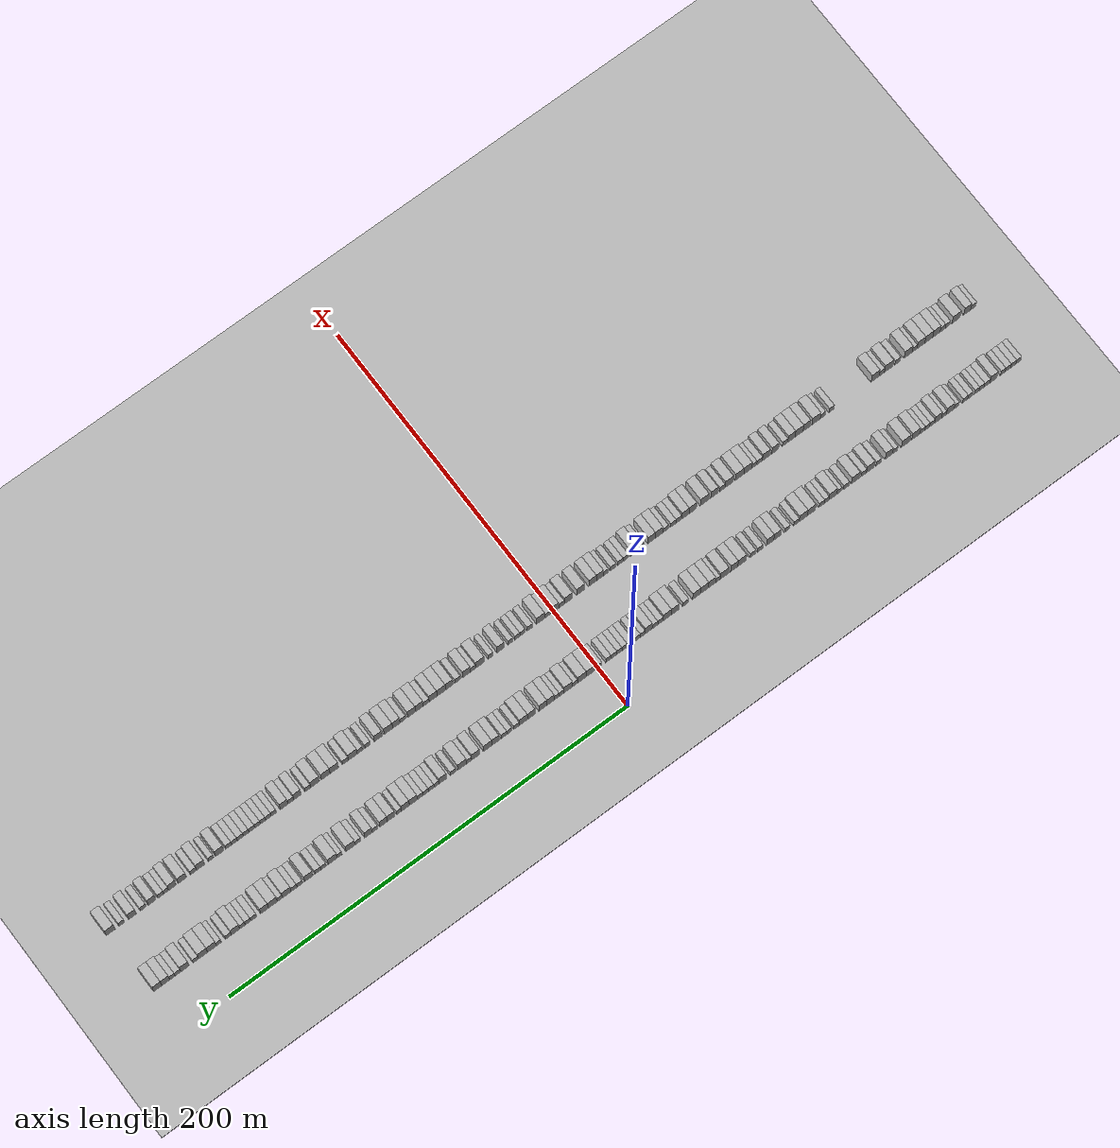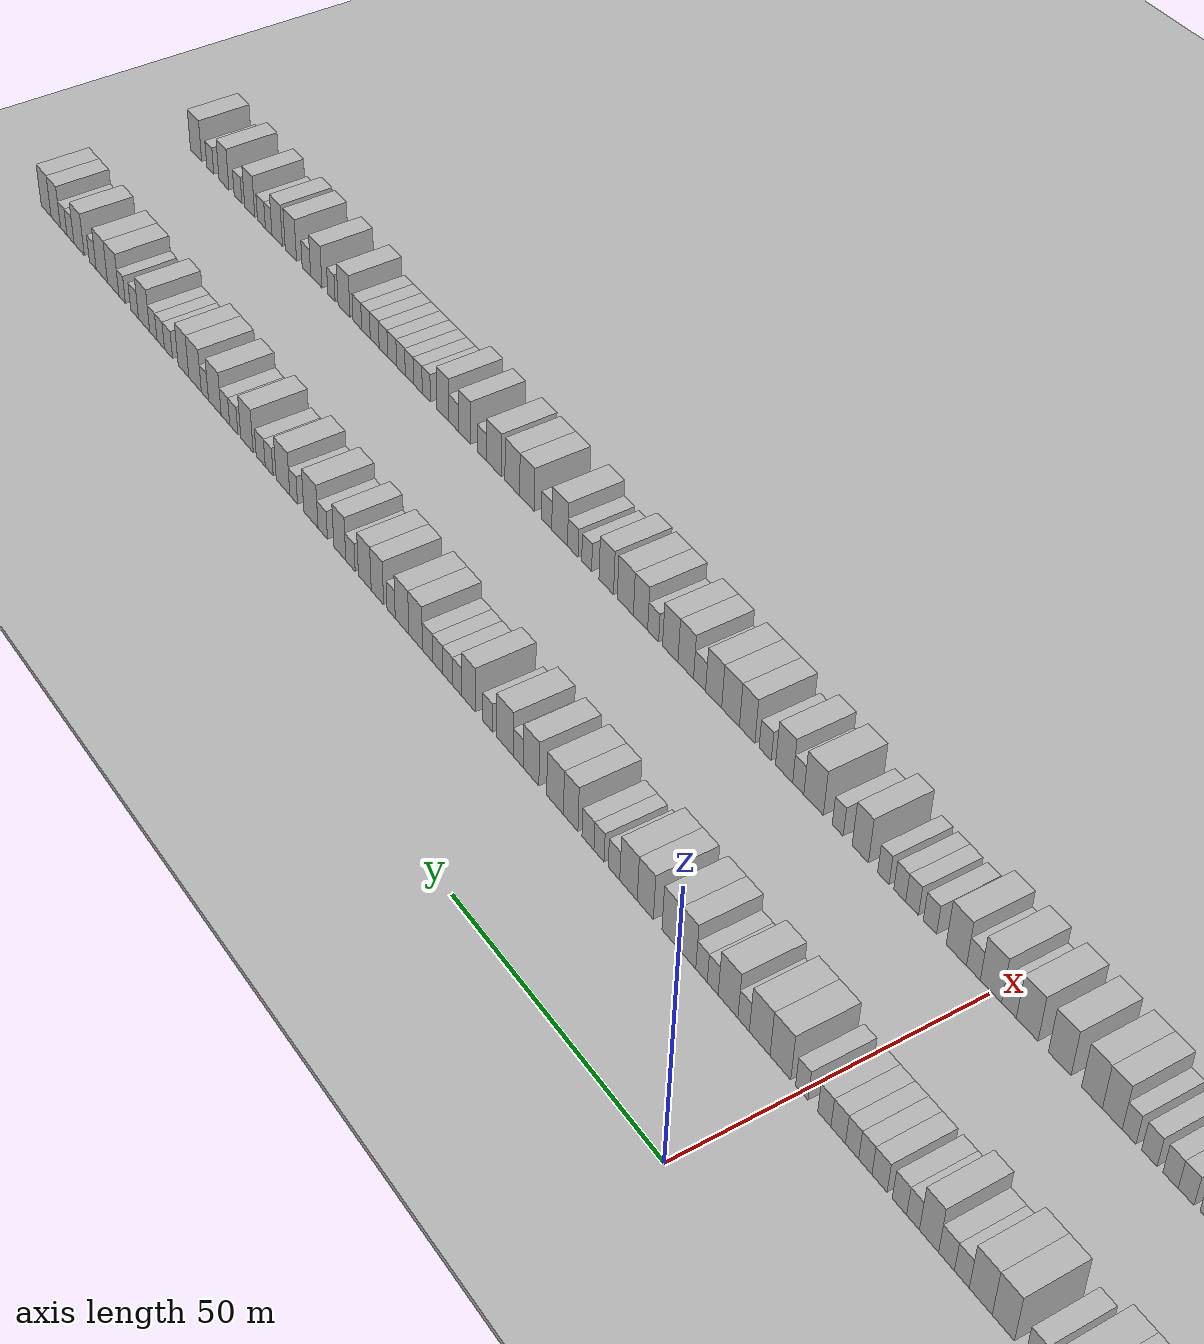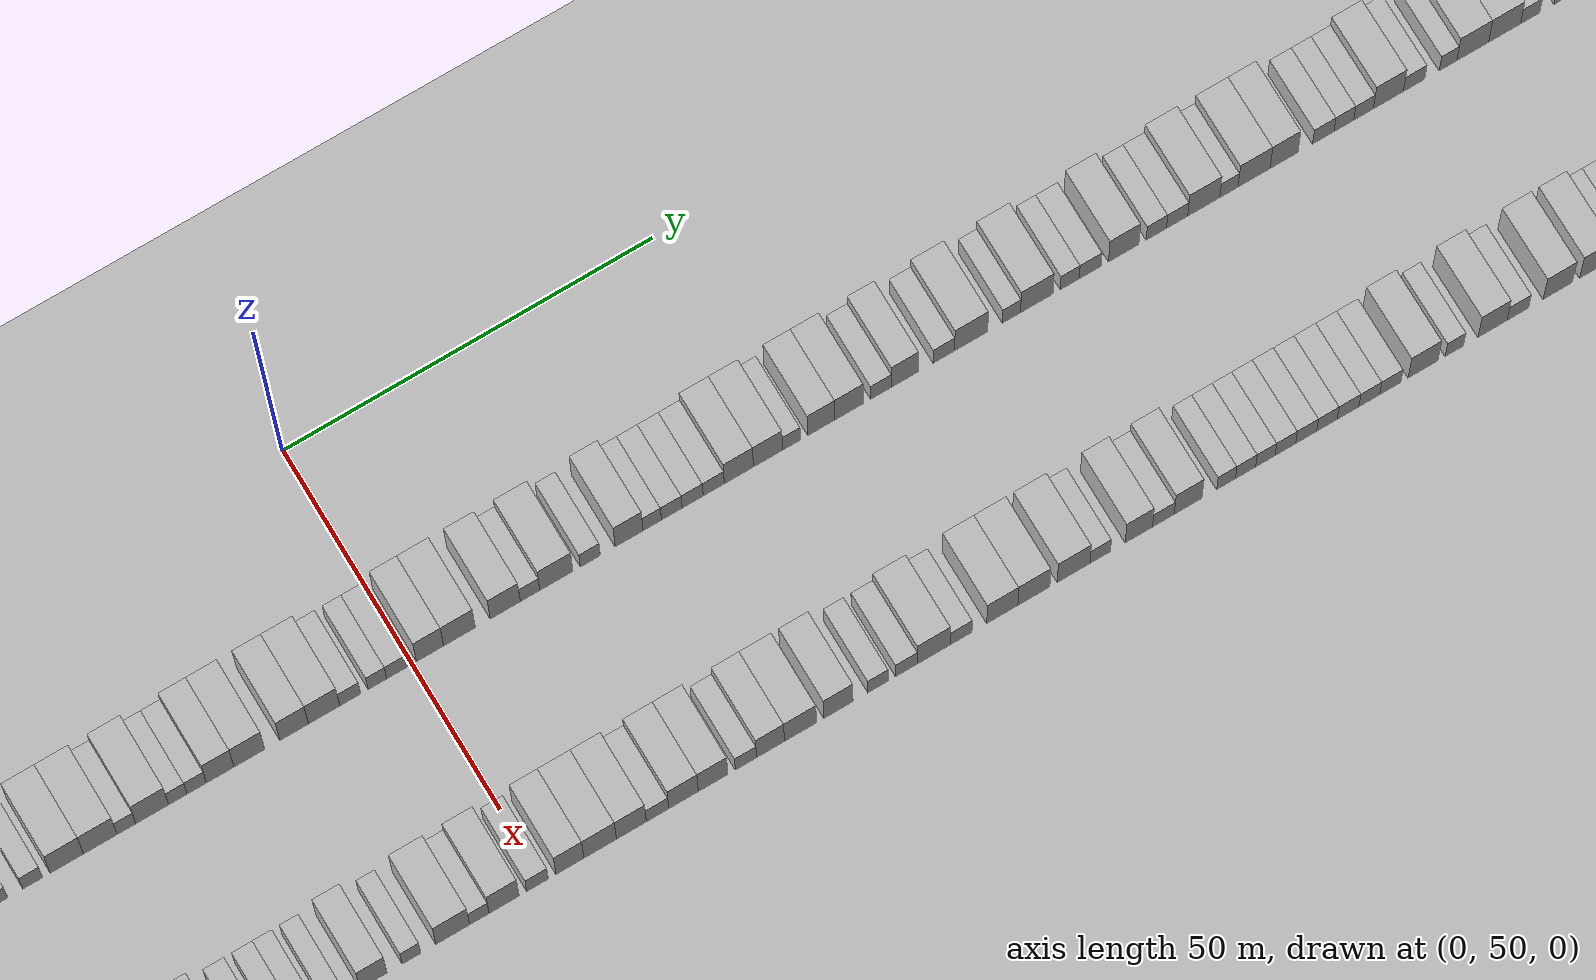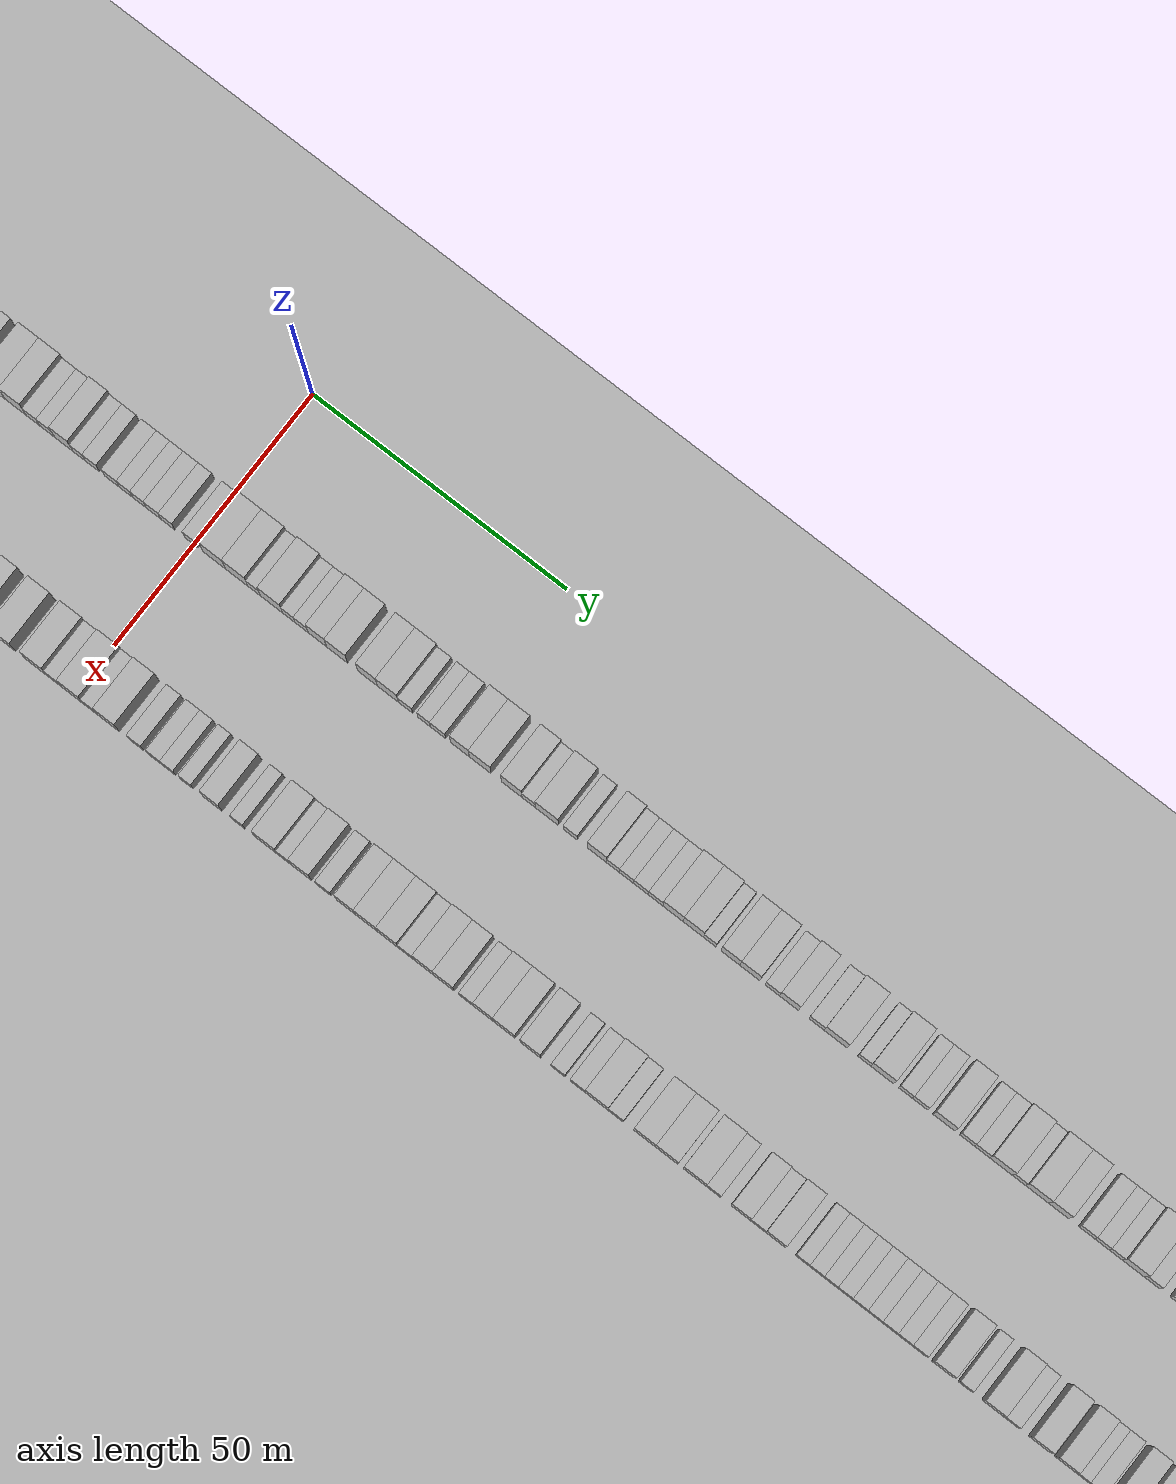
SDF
<?xml version="1.0" encoding="utf-8"?>

<sdf version="1.6">

   <world name="default">

      <gui fullscreen="0">

         <camera name="user_camera">

            <pose>-15 0 4.57585 0 0 0</pose>

            <view_controller>orbit</view_controller>

         </camera>

      </gui>

      <scene>

         <sky>

           <clouds>

             <speed>12</speed>

           </clouds>

         </sky>

         <ambient>0.4 0.4 0.4 1</ambient>

         <background>0.7 0.7 0.7 1</background>

         <shadows>1</shadows>

      </scene>

      <gravity>0 0 -9.8066</gravity>

      <magnetic_field>6e-06 2.3e-05 -4.2e-05</magnetic_field>

      <physics default="0" name="default_physics" type="ode">

         <ode>

            <solver>

               <type>quick</type>

               <iters>10</iters>

               <sor>1.0</sor>

               <use_dynamic_moi_rescaling>0</use_dynamic_moi_rescaling>

            </solver>

            <constraints>

               <cfm>0</cfm>

               <erp>0.2</erp>

               <contact_max_correcting_vel>100</contact_max_correcting_vel>

               <contact_surface_layer>0.001</contact_surface_layer>

            </constraints>

         </ode>

         <max_step_size>0.004</max_step_size>

         <real_time_factor>1</real_time_factor>

         <real_time_update_rate>250</real_time_update_rate>

      </physics>

      <light name="sun" type="directional">

         <cast_shadows>1</cast_shadows>

         <pose>0 0 10 0 0 0</pose>

         <diffuse>0.8 0.8 0.8 1</diffuse>

         <specular>0.2 0.2 0.2 1</specular>

         <attenuation>

            <range>1000</range>

            <constant>0.9</constant>

            <linear>0.01</linear>

            <quadratic>0.001</quadratic>

         </attenuation>

         <direction>-0.5 0.1 -0.9</direction>

      </light>

      <include>

         <name>ground_plane_1</name>

         <uri>model://HANNAS_ground_plane</uri>

         <pose>0 0 0  0 0 0</pose>

      </include>

      <include>

         <name>ground_plane_2</name>

         <uri>model://HANNAS_ground_plane</uri>

         <pose>100 0 0  0 0 0</pose>

      </include>

      <model name="building_1">

         <static>1</static>

         <pose frame="">25.0000 -218.7349 0 0.000000 0.000000 0.000000</pose>

         <link name="link">

            <pose frame="">0 0 3.00 0 0 0</pose>

            <collision name="collision">

               <geometry>

                  <box>

                     <size>10.0000 2.5302 6.0000</size>

                  </box>

               </geometry>

               <max_contacts>10</max_contacts>

               <surface>

                  <contact>

                     <ode/>

                  </contact>

                  <bounce/>

                  <friction>

                     <torsional>

                        <ode/>

                     </torsional>

                     <ode/>

                  </friction>

               </surface>

            </collision>

            <visual name="visual">

               <cast_shadows>0</cast_shadows>

               <geometry>

                  <box>

                     <size>10.0000 2.5302 6.0000</size>

                  </box>

               </geometry>

               <material>

                  <script>

                     <uri>model://HANNAS_wall/materials/scripts</uri>

                     <uri>model://HANNAS_wall/materials/textures</uri>

                     <name>vrc/HANNAS_wall</name>

                  </script>

               </material>

            </visual>

            <self_collide>0</self_collide>

            <enable_wind>0</enable_wind>

            <kinematic>0</kinematic>

         </link>

      </model>

      <model name="building_2">

         <static>1</static>

         <pose frame="">25.0000 -216.0574 0 0.000000 0.000000 0.000000</pose>

         <link name="link">

            <pose frame="">0 0 3.00 0 0 0</pose>

            <collision name="collision">

               <geometry>

                  <box>

                     <size>10.0000 2.8248 6.0000</size>

                  </box>

               </geometry>

               <max_contacts>10</max_contacts>

               <surface>

                  <contact>

                     <ode/>

                  </contact>

                  <bounce/>

                  <friction>

                     <torsional>

                        <ode/>

                     </torsional>

                     <ode/>

                  </friction>

               </surface>

            </collision>

            <visual name="visual">

               <cast_shadows>0</cast_shadows>

               <geometry>

                  <box>

                     <size>10.0000 2.8248 6.0000</size>

                  </box>

               </geometry>

               <material>

                  <script>

                     <uri>model://HANNAS_wall/materials/scripts</uri>

                     <uri>model://HANNAS_wall/materials/textures</uri>

                     <name>vrc/HANNAS_wall</name>

                  </script>

               </material>

            </visual>

            <self_collide>0</self_collide>

            <enable_wind>0</enable_wind>

            <kinematic>0</kinematic>

         </link>

      </model>

      <model name="building_3">

         <static>1</static>

         <pose frame="">25.0000 -213.1955 0 0.000000 0.000000 0.000000</pose>

         <link name="link">

            <pose frame="">0 0 3.00 0 0 0</pose>

            <collision name="collision">

               <geometry>

                  <box>

                     <size>10.0000 2.8991 6.0000</size>

                  </box>

               </geometry>

               <max_contacts>10</max_contacts>

               <surface>

                  <contact>

                     <ode/>

                  </contact>

                  <bounce/>

                  <friction>

                     <torsional>

                        <ode/>

                     </torsional>

                     <ode/>

                  </friction>

               </surface>

            </collision>

            <visual name="visual">

               <cast_shadows>0</cast_shadows>

               <geometry>

                  <box>

                     <size>10.0000 2.8991 6.0000</size>

                  </box>

               </geometry>

               <material>

                  <script>

                     <uri>model://HANNAS_wall/materials/scripts</uri>

                     <uri>model://HANNAS_wall/materials/textures</uri>

                     <name>vrc/HANNAS_wall</name>

                  </script>

               </material>

            </visual>

            <self_collide>0</self_collide>

            <enable_wind>0</enable_wind>

            <kinematic>0</kinematic>

         </link>

      </model>

      <model name="building_4">

         <static>1</static>

         <pose frame="">25.0000 -210.4919 0 0.000000 0.000000 0.000000</pose>

         <link name="link">

            <pose frame="">0 0 3.00 0 0 0</pose>

            <collision name="collision">

               <geometry>

                  <box>

                     <size>10.0000 2.5081 6.0000</size>

                  </box>

               </geometry>

               <max_contacts>10</max_contacts>

               <surface>

                  <contact>

                     <ode/>

                  </contact>

                  <bounce/>

                  <friction>

                     <torsional>

                        <ode/>

                     </torsional>

                     <ode/>

                  </friction>

               </surface>

            </collision>

            <visual name="visual">

               <cast_shadows>0</cast_shadows>

               <geometry>

                  <box>

                     <size>10.0000 2.5081 6.0000</size>

                  </box>

               </geometry>

               <material>

                  <script>

                     <uri>model://HANNAS_wall/materials/scripts</uri>

                     <uri>model://HANNAS_wall/materials/textures</uri>

                     <name>vrc/HANNAS_wall</name>

                  </script>

               </material>

            </visual>

            <self_collide>0</self_collide>

            <enable_wind>0</enable_wind>

            <kinematic>0</kinematic>

         </link>

      </model>

      <model name="building_5">

         <static>1</static>

         <pose frame="">25.0000 -205.4100 0 0.000000 0.000000 0.000000</pose>

         <link name="link">

            <pose frame="">0 0 4.50 0 0 0</pose>

            <collision name="collision">

               <geometry>

                  <box>

                     <size>10.0000 3.6556 9.0000</size>

                  </box>

               </geometry>

               <max_contacts>10</max_contacts>

               <surface>

                  <contact>

                     <ode/>

                  </contact>

                  <bounce/>

                  <friction>

                     <torsional>

                        <ode/>

                     </torsional>

                     <ode/>

                  </friction>

               </surface>

            </collision>

            <visual name="visual">

               <cast_shadows>0</cast_shadows>

               <geometry>

                  <box>

                     <size>10.0000 3.6556 9.0000</size>

                  </box>

               </geometry>

               <material>

                  <script>

                     <uri>model://HANNAS_wall/materials/scripts</uri>

                     <uri>model://HANNAS_wall/materials/textures</uri>

                     <name>vrc/HANNAS_wall</name>

                  </script>

               </material>

            </visual>

            <self_collide>0</self_collide>

            <enable_wind>0</enable_wind>

            <kinematic>0</kinematic>

         </link>

      </model>

      <model name="building_6">

         <static>1</static>

         <pose frame="">25.0000 -202.0952 0 0.000000 0.000000 0.000000</pose>

         <link name="link">

            <pose frame="">0 0 3.00 0 0 0</pose>

            <collision name="collision">

               <geometry>

                  <box>

                     <size>10.0000 2.9741 6.0000</size>

                  </box>

               </geometry>

               <max_contacts>10</max_contacts>

               <surface>

                  <contact>

                     <ode/>

                  </contact>

                  <bounce/>

                  <friction>

                     <torsional>

                        <ode/>

                     </torsional>

                     <ode/>

                  </friction>

               </surface>

            </collision>

            <visual name="visual">

               <cast_shadows>0</cast_shadows>

               <geometry>

                  <box>

                     <size>10.0000 2.9741 6.0000</size>

                  </box>

               </geometry>

               <material>

                  <script>

                     <uri>model://HANNAS_wall/materials/scripts</uri>

                     <uri>model://HANNAS_wall/materials/textures</uri>

                     <name>vrc/HANNAS_wall</name>

                  </script>

               </material>

            </visual>

            <self_collide>0</self_collide>

            <enable_wind>0</enable_wind>

            <kinematic>0</kinematic>

         </link>

      </model>

      <model name="building_7">

         <static>1</static>

         <pose frame="">25.0000 -199.2665 0 0.000000 0.000000 0.000000</pose>

         <link name="link">

            <pose frame="">0 0 3.00 0 0 0</pose>

            <collision name="collision">

               <geometry>

                  <box>

                     <size>10.0000 2.6833 6.0000</size>

                  </box>

               </geometry>

               <max_contacts>10</max_contacts>

               <surface>

                  <contact>

                     <ode/>

                  </contact>

                  <bounce/>

                  <friction>

                     <torsional>

                        <ode/>

                     </torsional>

                     <ode/>

                  </friction>

               </surface>

            </collision>

            <visual name="visual">

               <cast_shadows>0</cast_shadows>

               <geometry>

                  <box>

                     <size>10.0000 2.6833 6.0000</size>

                  </box>

               </geometry>

               <material>

                  <script>

                     <uri>model://HANNAS_wall/materials/scripts</uri>

                     <uri>model://HANNAS_wall/materials/textures</uri>

                     <name>vrc/HANNAS_wall</name>

                  </script>

               </material>

            </visual>

            <self_collide>0</self_collide>

            <enable_wind>0</enable_wind>

            <kinematic>0</kinematic>

         </link>

      </model>

      <model name="building_8">

         <static>1</static>

         <pose frame="">25.0000 -196.7200 0 0.000000 0.000000 0.000000</pose>

         <link name="link">

            <pose frame="">0 0 3.00 0 0 0</pose>

            <collision name="collision">

               <geometry>

                  <box>

                     <size>10.0000 2.4096 6.0000</size>

                  </box>

               </geometry>

               <max_contacts>10</max_contacts>

               <surface>

                  <contact>

                     <ode/>

                  </contact>

                  <bounce/>

                  <friction>

                     <torsional>

                        <ode/>

                     </torsional>

                     <ode/>

                  </friction>

               </surface>

            </collision>

            <visual name="visual">

               <cast_shadows>0</cast_shadows>

               <geometry>

                  <box>

                     <size>10.0000 2.4096 6.0000</size>

                  </box>

               </geometry>

               <material>

                  <script>

                     <uri>model://HANNAS_wall/materials/scripts</uri>

                     <uri>model://HANNAS_wall/materials/textures</uri>

                     <name>vrc/HANNAS_wall</name>

                  </script>

               </material>

            </visual>

            <self_collide>0</self_collide>

            <enable_wind>0</enable_wind>

            <kinematic>0</kinematic>

         </link>

      </model>

      <model name="building_9">

         <static>1</static>

         <pose frame="">25.0000 -193.1992 0 0.000000 0.000000 0.000000</pose>

         <link name="link">

            <pose frame="">0 0 3.00 0 0 0</pose>

            <collision name="collision">

               <geometry>

                  <box>

                     <size>10.0000 2.6320 6.0000</size>

                  </box>

               </geometry>

               <max_contacts>10</max_contacts>

               <surface>

                  <contact>

                     <ode/>

                  </contact>

                  <bounce/>

                  <friction>

                     <torsional>

                        <ode/>

                     </torsional>

                     <ode/>

                  </friction>

               </surface>

            </collision>

            <visual name="visual">

               <cast_shadows>0</cast_shadows>

               <geometry>

                  <box>

                     <size>10.0000 2.6320 6.0000</size>

                  </box>

               </geometry>

               <material>

                  <script>

                     <uri>model://HANNAS_wall/materials/scripts</uri>

                     <uri>model://HANNAS_wall/materials/textures</uri>

                     <name>vrc/HANNAS_wall</name>

                  </script>

               </material>

            </visual>

            <self_collide>0</self_collide>

            <enable_wind>0</enable_wind>

            <kinematic>0</kinematic>

         </link>

      </model>

      <model name="building_10">

         <static>1</static>

         <pose frame="">25.0000 -190.5442 0 0.000000 0.000000 0.000000</pose>

         <link name="link">

            <pose frame="">0 0 3.00 0 0 0</pose>

            <collision name="collision">

               <geometry>

                  <box>

                     <size>10.0000 2.6780 6.0000</size>

                  </box>

               </geometry>

               <max_contacts>10</max_contacts>

               <surface>

                  <contact>

                     <ode/>

                  </contact>

                  <bounce/>

                  <friction>

                     <torsional>

                        <ode/>

                     </torsional>

                     <ode/>

                  </friction>

               </surface>

            </collision>

            <visual name="visual">

               <cast_shadows>0</cast_shadows>

               <geometry>

                  <box>

                     <size>10.0000 2.6780 6.0000</size>

                  </box>

               </geometry>

               <material>

                  <script>

                     <uri>model://HANNAS_wall/materials/scripts</uri>

                     <uri>model://HANNAS_wall/materials/textures</uri>

                     <name>vrc/HANNAS_wall</name>

                  </script>

               </material>

            </visual>

            <self_collide>0</self_collide>

            <enable_wind>0</enable_wind>

            <kinematic>0</kinematic>

         </link>

      </model>

      <model name="building_11">

         <static>1</static>

         <pose frame="">25.0000 -185.9322 0 0.000000 0.000000 0.000000</pose>

         <link name="link">

            <pose frame="">0 0 3.00 0 0 0</pose>

            <collision name="collision">

               <geometry>

                  <box>

                     <size>10.0000 2.5460 6.0000</size>

                  </box>

               </geometry>

               <max_contacts>10</max_contacts>

               <surface>

                  <contact>

                     <ode/>

                  </contact>

                  <bounce/>

                  <friction>

                     <torsional>

                        <ode/>

                     </torsional>

                     <ode/>

                  </friction>

               </surface>

            </collision>

            <visual name="visual">

               <cast_shadows>0</cast_shadows>

               <geometry>

                  <box>

                     <size>10.0000 2.5460 6.0000</size>

                  </box>

               </geometry>

               <material>

                  <script>

                     <uri>model://HANNAS_wall/materials/scripts</uri>

                     <uri>model://HANNAS_wall/materials/textures</uri>

                     <name>vrc/HANNAS_wall</name>

                  </script>

               </material>

            </visual>

            <self_collide>0</self_collide>

            <enable_wind>0</enable_wind>

            <kinematic>0</kinematic>

         </link>

      </model>

      <model name="building_12">

         <static>1</static>

         <pose frame="">25.0000 -182.6066 0 0.000000 0.000000 0.000000</pose>

         <link name="link">

            <pose frame="">0 0 4.50 0 0 0</pose>

            <collision name="collision">

               <geometry>

                  <box>

                     <size>10.0000 4.1051 9.0000</size>

                  </box>

               </geometry>

               <max_contacts>10</max_contacts>

               <surface>

                  <contact>

                     <ode/>

                  </contact>

                  <bounce/>

                  <friction>

                     <torsional>

                        <ode/>

                     </torsional>

                     <ode/>

                  </friction>

               </surface>

            </collision>

            <visual name="visual">

               <cast_shadows>0</cast_shadows>

               <geometry>

                  <box>

                     <size>10.0000 4.1051 9.0000</size>

                  </box>

               </geometry>

               <material>

                  <script>

                     <uri>model://HANNAS_wall/materials/scripts</uri>

                     <uri>model://HANNAS_wall/materials/textures</uri>

                     <name>vrc/HANNAS_wall</name>

                  </script>

               </material>

            </visual>

            <self_collide>0</self_collide>

            <enable_wind>0</enable_wind>

            <kinematic>0</kinematic>

         </link>

      </model>

      <model name="building_13">

         <static>1</static>

         <pose frame="">25.0000 -179.2901 0 0.000000 0.000000 0.000000</pose>

         <link name="link">

            <pose frame="">0 0 3.00 0 0 0</pose>

            <collision name="collision">

               <geometry>

                  <box>

                     <size>10.0000 2.5279 6.0000</size>

                  </box>

               </geometry>

               <max_contacts>10</max_contacts>

               <surface>

                  <contact>

                     <ode/>

                  </contact>

                  <bounce/>

                  <friction>

                     <torsional>

                        <ode/>

                     </torsional>

                     <ode/>

                  </friction>

               </surface>

            </collision>

            <visual name="visual">

               <cast_shadows>0</cast_shadows>

               <geometry>

                  <box>

                     <size>10.0000 2.5279 6.0000</size>

                  </box>

               </geometry>

               <material>

                  <script>

                     <uri>model://HANNAS_wall/materials/scripts</uri>

                     <uri>model://HANNAS_wall/materials/textures</uri>

                     <name>vrc/HANNAS_wall</name>

                  </script>

               </material>

            </visual>

            <self_collide>0</self_collide>

            <enable_wind>0</enable_wind>

            <kinematic>0</kinematic>

         </link>

      </model>

      <model name="building_14">

         <static>1</static>

         <pose frame="">25.0000 -176.1806 0 0.000000 0.000000 0.000000</pose>

         <link name="link">

            <pose frame="">0 0 4.50 0 0 0</pose>

            <collision name="collision">

               <geometry>

                  <box>

                     <size>10.0000 3.6912 9.0000</size>

                  </box>

               </geometry>

               <max_contacts>10</max_contacts>

               <surface>

                  <contact>

                     <ode/>

                  </contact>

                  <bounce/>

                  <friction>

                     <torsional>

                        <ode/>

                     </torsional>

                     <ode/>

                  </friction>

               </surface>

            </collision>

            <visual name="visual">

               <cast_shadows>0</cast_shadows>

               <geometry>

                  <box>

                     <size>10.0000 3.6912 9.0000</size>

                  </box>

               </geometry>

               <material>

                  <script>

                     <uri>model://HANNAS_wall/materials/scripts</uri>

                     <uri>model://HANNAS_wall/materials/textures</uri>

                     <name>vrc/HANNAS_wall</name>

                  </script>

               </material>

            </visual>

            <self_collide>0</self_collide>

            <enable_wind>0</enable_wind>

            <kinematic>0</kinematic>

         </link>

      </model>

      <model name="building_15">

         <static>1</static>

         <pose frame="">25.0000 -173.0850 0 0.000000 0.000000 0.000000</pose>

         <link name="link">

            <pose frame="">0 0 3.00 0 0 0</pose>

            <collision name="collision">

               <geometry>

                  <box>

                     <size>10.0000 2.4998 6.0000</size>

                  </box>

               </geometry>

               <max_contacts>10</max_contacts>

               <surface>

                  <contact>

                     <ode/>

                  </contact>

                  <bounce/>

                  <friction>

                     <torsional>

                        <ode/>

                     </torsional>

                     <ode/>

                  </friction>

               </surface>

            </collision>

            <visual name="visual">

               <cast_shadows>0</cast_shadows>

               <geometry>

                  <box>

                     <size>10.0000 2.4998 6.0000</size>

                  </box>

               </geometry>

               <material>

                  <script>

                     <uri>model://HANNAS_wall/materials/scripts</uri>

                     <uri>model://HANNAS_wall/materials/textures</uri>

                     <name>vrc/HANNAS_wall</name>

                  </script>

               </material>

            </visual>

            <self_collide>0</self_collide>

            <enable_wind>0</enable_wind>

            <kinematic>0</kinematic>

         </link>

      </model>

      <model name="building_16">

         <static>1</static>

         <pose frame="">25.0000 -170.5626 0 0.000000 0.000000 0.000000</pose>

         <link name="link">

            <pose frame="">0 0 3.00 0 0 0</pose>

            <collision name="collision">

               <geometry>

                  <box>

                     <size>10.0000 2.5451 6.0000</size>

                  </box>

               </geometry>

               <max_contacts>10</max_contacts>

               <surface>

                  <contact>

                     <ode/>

                  </contact>

                  <bounce/>

                  <friction>

                     <torsional>

                        <ode/>

                     </torsional>

                     <ode/>

                  </friction>

               </surface>

            </collision>

            <visual name="visual">

               <cast_shadows>0</cast_shadows>

               <geometry>

                  <box>

                     <size>10.0000 2.5451 6.0000</size>

                  </box>

               </geometry>

               <material>

                  <script>

                     <uri>model://HANNAS_wall/materials/scripts</uri>

                     <uri>model://HANNAS_wall/materials/textures</uri>

                     <name>vrc/HANNAS_wall</name>

                  </script>

               </material>

            </visual>

            <self_collide>0</self_collide>

            <enable_wind>0</enable_wind>

            <kinematic>0</kinematic>

         </link>

      </model>

      <model name="building_17">

         <static>1</static>

         <pose frame="">25.0000 -167.9040 0 0.000000 0.000000 0.000000</pose>

         <link name="link">

            <pose frame="">0 0 3.00 0 0 0</pose>

            <collision name="collision">

               <geometry>

                  <box>

                     <size>10.0000 2.7722 6.0000</size>

                  </box>

               </geometry>

               <max_contacts>10</max_contacts>

               <surface>

                  <contact>

                     <ode/>

                  </contact>

                  <bounce/>

                  <friction>

                     <torsional>

                        <ode/>

                     </torsional>

                     <ode/>

                  </friction>

               </surface>

            </collision>

            <visual name="visual">

               <cast_shadows>0</cast_shadows>

               <geometry>

                  <box>

                     <size>10.0000 2.7722 6.0000</size>

                  </box>

               </geometry>

               <material>

                  <script>

                     <uri>model://HANNAS_wall/materials/scripts</uri>

                     <uri>model://HANNAS_wall/materials/textures</uri>

                     <name>vrc/HANNAS_wall</name>

                  </script>

               </material>

            </visual>

            <self_collide>0</self_collide>

            <enable_wind>0</enable_wind>

            <kinematic>0</kinematic>

         </link>

      </model>

      <model name="building_18">

         <static>1</static>

         <pose frame="">25.0000 -164.4683 0 0.000000 0.000000 0.000000</pose>

         <link name="link">

            <pose frame="">0 0 4.50 0 0 0</pose>

            <collision name="collision">

               <geometry>

                  <box>

                     <size>10.0000 4.0991 9.0000</size>

                  </box>

               </geometry>

               <max_contacts>10</max_contacts>

               <surface>

                  <contact>

                     <ode/>

                  </contact>

                  <bounce/>

                  <friction>

                     <torsional>

                        <ode/>

                     </torsional>

                     <ode/>

                  </friction>

               </surface>

            </collision>

            <visual name="visual">

               <cast_shadows>0</cast_shadows>

               <geometry>

                  <box>

                     <size>10.0000 4.0991 9.0000</size>

                  </box>

               </geometry>

               <material>

                  <script>

                     <uri>model://HANNAS_wall/materials/scripts</uri>

                     <uri>model://HANNAS_wall/materials/textures</uri>

                     <name>vrc/HANNAS_wall</name>

                  </script>

               </material>

            </visual>

            <self_collide>0</self_collide>

            <enable_wind>0</enable_wind>

            <kinematic>0</kinematic>

         </link>

      </model>

      <model name="building_19">

         <static>1</static>

         <pose frame="">25.0000 -159.1697 0 0.000000 0.000000 0.000000</pose>

         <link name="link">

            <pose frame="">0 0 4.50 0 0 0</pose>

            <collision name="collision">

               <geometry>

                  <box>

                     <size>10.0000 4.4982 9.0000</size>

                  </box>

               </geometry>

               <max_contacts>10</max_contacts>

               <surface>

                  <contact>

                     <ode/>

                  </contact>

                  <bounce/>

                  <friction>

                     <torsional>

                        <ode/>

                     </torsional>

                     <ode/>

                  </friction>

               </surface>

            </collision>

            <visual name="visual">

               <cast_shadows>0</cast_shadows>

               <geometry>

                  <box>

                     <size>10.0000 4.4982 9.0000</size>

                  </box>

               </geometry>

               <material>

                  <script>

                     <uri>model://HANNAS_wall/materials/scripts</uri>

                     <uri>model://HANNAS_wall/materials/textures</uri>

                     <name>vrc/HANNAS_wall</name>

                  </script>

               </material>

            </visual>

            <self_collide>0</self_collide>

            <enable_wind>0</enable_wind>

            <kinematic>0</kinematic>

         </link>

      </model>

      <model name="building_20">

         <static>1</static>

         <pose frame="">25.0000 -153.5271 0 0.000000 0.000000 0.000000</pose>

         <link name="link">

            <pose frame="">0 0 3.00 0 0 0</pose>

            <collision name="collision">

               <geometry>

                  <box>

                     <size>10.0000 2.7869 6.0000</size>

                  </box>

               </geometry>

               <max_contacts>10</max_contacts>

               <surface>

                  <contact>

                     <ode/>

                  </contact>

                  <bounce/>

                  <friction>

                     <torsional>

                        <ode/>

                     </torsional>

                     <ode/>

                  </friction>

               </surface>

            </collision>

            <visual name="visual">

               <cast_shadows>0</cast_shadows>

               <geometry>

                  <box>

                     <size>10.0000 2.7869 6.0000</size>

                  </box>

               </geometry>

               <material>

                  <script>

                     <uri>model://HANNAS_wall/materials/scripts</uri>

                     <uri>model://HANNAS_wall/materials/textures</uri>

                     <name>vrc/HANNAS_wall</name>

                  </script>

               </material>

            </visual>

            <self_collide>0</self_collide>

            <enable_wind>0</enable_wind>

            <kinematic>0</kinematic>

         </link>

      </model>

      <model name="building_21">

         <static>1</static>

         <pose frame="">25.0000 -150.2575 0 0.000000 0.000000 0.000000</pose>

         <link name="link">

            <pose frame="">0 0 4.50 0 0 0</pose>

            <collision name="collision">

               <geometry>

                  <box>

                     <size>10.0000 3.7524 9.0000</size>

                  </box>

               </geometry>

               <max_contacts>10</max_contacts>

               <surface>

                  <contact>

                     <ode/>

                  </contact>

                  <bounce/>

                  <friction>

                     <torsional>

                        <ode/>

                     </torsional>

                     <ode/>

                  </friction>

               </surface>

            </collision>

            <visual name="visual">

               <cast_shadows>0</cast_shadows>

               <geometry>

                  <box>

                     <size>10.0000 3.7524 9.0000</size>

                  </box>

               </geometry>

               <material>

                  <script>

                     <uri>model://HANNAS_wall/materials/scripts</uri>

                     <uri>model://HANNAS_wall/materials/textures</uri>

                     <name>vrc/HANNAS_wall</name>

                  </script>

               </material>

            </visual>

            <self_collide>0</self_collide>

            <enable_wind>0</enable_wind>

            <kinematic>0</kinematic>

         </link>

      </model>

      <model name="building_22">

         <static>1</static>

         <pose frame="">25.0000 -145.0025 0 0.000000 0.000000 0.000000</pose>

         <link name="link">

            <pose frame="">0 0 3.00 0 0 0</pose>

            <collision name="collision">

               <geometry>

                  <box>

                     <size>10.0000 2.7575 6.0000</size>

                  </box>

               </geometry>

               <max_contacts>10</max_contacts>

               <surface>

                  <contact>

                     <ode/>

                  </contact>

                  <bounce/>

                  <friction>

                     <torsional>

                        <ode/>

                     </torsional>

                     <ode/>

                  </friction>

               </surface>

            </collision>

            <visual name="visual">

               <cast_shadows>0</cast_shadows>

               <geometry>

                  <box>

                     <size>10.0000 2.7575 6.0000</size>

                  </box>

               </geometry>

               <material>

                  <script>

                     <uri>model://HANNAS_wall/materials/scripts</uri>

                     <uri>model://HANNAS_wall/materials/textures</uri>

                     <name>vrc/HANNAS_wall</name>

                  </script>

               </material>

            </visual>

            <self_collide>0</self_collide>

            <enable_wind>0</enable_wind>

            <kinematic>0</kinematic>

         </link>

      </model>

      <model name="building_23">

         <static>1</static>

         <pose frame="">25.0000 -140.6257 0 0.000000 0.000000 0.000000</pose>

         <link name="link">

            <pose frame="">0 0 4.50 0 0 0</pose>

            <collision name="collision">

               <geometry>

                  <box>

                     <size>10.0000 3.9959 9.0000</size>

                  </box>

               </geometry>

               <max_contacts>10</max_contacts>

               <surface>

                  <contact>

                     <ode/>

                  </contact>

                  <bounce/>

                  <friction>

                     <torsional>

                        <ode/>

                     </torsional>

                     <ode/>

                  </friction>

               </surface>

            </collision>

            <visual name="visual">

               <cast_shadows>0</cast_shadows>

               <geometry>

                  <box>

                     <size>10.0000 3.9959 9.0000</size>

                  </box>

               </geometry>

               <material>

                  <script>

                     <uri>model://HANNAS_wall/materials/scripts</uri>

                     <uri>model://HANNAS_wall/materials/textures</uri>

                     <name>vrc/HANNAS_wall</name>

                  </script>

               </material>

            </visual>

            <self_collide>0</self_collide>

            <enable_wind>0</enable_wind>

            <kinematic>0</kinematic>

         </link>

      </model>

      <model name="building_24">

         <static>1</static>

         <pose frame="">25.0000 -137.2848 0 0.000000 0.000000 0.000000</pose>

         <link name="link">

            <pose frame="">0 0 3.00 0 0 0</pose>

            <collision name="collision">

               <geometry>

                  <box>

                     <size>10.0000 2.6858 6.0000</size>

                  </box>

               </geometry>

               <max_contacts>10</max_contacts>

               <surface>

                  <contact>

                     <ode/>

                  </contact>

                  <bounce/>

                  <friction>

                     <torsional>

                        <ode/>

                     </torsional>

                     <ode/>

                  </friction>

               </surface>

            </collision>

            <visual name="visual">

               <cast_shadows>0</cast_shadows>

               <geometry>

                  <box>

                     <size>10.0000 2.6858 6.0000</size>

                  </box>

               </geometry>

               <material>

                  <script>

                     <uri>model://HANNAS_wall/materials/scripts</uri>

                     <uri>model://HANNAS_wall/materials/textures</uri>

                     <name>vrc/HANNAS_wall</name>

                  </script>

               </material>

            </visual>

            <self_collide>0</self_collide>

            <enable_wind>0</enable_wind>

            <kinematic>0</kinematic>

         </link>

      </model>

      <model name="building_25">

         <static>1</static>

         <pose frame="">25.0000 -132.7670 0 0.000000 0.000000 0.000000</pose>

         <link name="link">

            <pose frame="">0 0 4.50 0 0 0</pose>

            <collision name="collision">

               <geometry>

                  <box>

                     <size>10.0000 4.3498 9.0000</size>

                  </box>

               </geometry>

               <max_contacts>10</max_contacts>

               <surface>

                  <contact>

                     <ode/>

                  </contact>

                  <bounce/>

                  <friction>

                     <torsional>

                        <ode/>

                     </torsional>

                     <ode/>

                  </friction>

               </surface>

            </collision>

            <visual name="visual">

               <cast_shadows>0</cast_shadows>

               <geometry>

                  <box>

                     <size>10.0000 4.3498 9.0000</size>

                  </box>

               </geometry>

               <material>

                  <script>

                     <uri>model://HANNAS_wall/materials/scripts</uri>

                     <uri>model://HANNAS_wall/materials/textures</uri>

                     <name>vrc/HANNAS_wall</name>

                  </script>

               </material>

            </visual>

            <self_collide>0</self_collide>

            <enable_wind>0</enable_wind>

            <kinematic>0</kinematic>

         </link>

      </model>

      <model name="building_26">

         <static>1</static>

         <pose frame="">25.0000 -128.0927 0 0.000000 0.000000 0.000000</pose>

         <link name="link">

            <pose frame="">0 0 3.00 0 0 0</pose>

            <collision name="collision">

               <geometry>

                  <box>

                     <size>10.0000 2.9987 6.0000</size>

                  </box>

               </geometry>

               <max_contacts>10</max_contacts>

               <surface>

                  <contact>

                     <ode/>

                  </contact>

                  <bounce/>

                  <friction>

                     <torsional>

                        <ode/>

                     </torsional>

                     <ode/>

                  </friction>

               </surface>

            </collision>

            <visual name="visual">

               <cast_shadows>0</cast_shadows>

               <geometry>

                  <box>

                     <size>10.0000 2.9987 6.0000</size>

                  </box>

               </geometry>

               <material>

                  <script>

                     <uri>model://HANNAS_wall/materials/scripts</uri>

                     <uri>model://HANNAS_wall/materials/textures</uri>

                     <name>vrc/HANNAS_wall</name>

                  </script>

               </material>

            </visual>

            <self_collide>0</self_collide>

            <enable_wind>0</enable_wind>

            <kinematic>0</kinematic>

         </link>

      </model>

      <model name="building_27">

         <static>1</static>

         <pose frame="">25.0000 -124.3607 0 0.000000 0.000000 0.000000</pose>

         <link name="link">

            <pose frame="">0 0 3.00 0 0 0</pose>

            <collision name="collision">

               <geometry>

                  <box>

                     <size>10.0000 2.4653 6.0000</size>

                  </box>

               </geometry>

               <max_contacts>10</max_contacts>

               <surface>

                  <contact>

                     <ode/>

                  </contact>

                  <bounce/>

                  <friction>

                     <torsional>

                        <ode/>

                     </torsional>

                     <ode/>

                  </friction>

               </surface>

            </collision>

            <visual name="visual">

               <cast_shadows>0</cast_shadows>

               <geometry>

                  <box>

                     <size>10.0000 2.4653 6.0000</size>

                  </box>

               </geometry>

               <material>

                  <script>

                     <uri>model://HANNAS_wall/materials/scripts</uri>

                     <uri>model://HANNAS_wall/materials/textures</uri>

                     <name>vrc/HANNAS_wall</name>

                  </script>

               </material>

            </visual>

            <self_collide>0</self_collide>

            <enable_wind>0</enable_wind>

            <kinematic>0</kinematic>

         </link>

      </model>

      <model name="building_28">

         <static>1</static>

         <pose frame="">25.0000 -121.0586 0 0.000000 0.000000 0.000000</pose>

         <link name="link">

            <pose frame="">0 0 4.50 0 0 0</pose>

            <collision name="collision">

               <geometry>

                  <box>

                     <size>10.0000 4.1390 9.0000</size>

                  </box>

               </geometry>

               <max_contacts>10</max_contacts>

               <surface>

                  <contact>

                     <ode/>

                  </contact>

                  <bounce/>

                  <friction>

                     <torsional>

                        <ode/>

                     </torsional>

                     <ode/>

                  </friction>

               </surface>

            </collision>

            <visual name="visual">

               <cast_shadows>0</cast_shadows>

               <geometry>

                  <box>

                     <size>10.0000 4.1390 9.0000</size>

                  </box>

               </geometry>

               <material>

                  <script>

                     <uri>model://HANNAS_wall/materials/scripts</uri>

                     <uri>model://HANNAS_wall/materials/textures</uri>

                     <name>vrc/HANNAS_wall</name>

                  </script>

               </material>

            </visual>

            <self_collide>0</self_collide>

            <enable_wind>0</enable_wind>

            <kinematic>0</kinematic>

         </link>

      </model>

      <model name="building_29">

         <static>1</static>

         <pose frame="">25.0000 -117.7855 0 0.000000 0.000000 0.000000</pose>

         <link name="link">

            <pose frame="">0 0 3.00 0 0 0</pose>

            <collision name="collision">

               <geometry>

                  <box>

                     <size>10.0000 2.4071 6.0000</size>

                  </box>

               </geometry>

               <max_contacts>10</max_contacts>

               <surface>

                  <contact>

                     <ode/>

                  </contact>

                  <bounce/>

                  <friction>

                     <torsional>

                        <ode/>

                     </torsional>

                     <ode/>

                  </friction>

               </surface>

            </collision>

            <visual name="visual">

               <cast_shadows>0</cast_shadows>

               <geometry>

                  <box>

                     <size>10.0000 2.4071 6.0000</size>

                  </box>

               </geometry>

               <material>

                  <script>

                     <uri>model://HANNAS_wall/materials/scripts</uri>

                     <uri>model://HANNAS_wall/materials/textures</uri>

                     <name>vrc/HANNAS_wall</name>

                  </script>

               </material>

            </visual>

            <self_collide>0</self_collide>

            <enable_wind>0</enable_wind>

            <kinematic>0</kinematic>

         </link>

      </model>

      <model name="building_30">

         <static>1</static>

         <pose frame="">25.0000 -115.2369 0 0.000000 0.000000 0.000000</pose>

         <link name="link">

            <pose frame="">0 0 3.00 0 0 0</pose>

            <collision name="collision">

               <geometry>

                  <box>

                     <size>10.0000 2.6901 6.0000</size>

                  </box>

               </geometry>

               <max_contacts>10</max_contacts>

               <surface>

                  <contact>

                     <ode/>

                  </contact>

                  <bounce/>

                  <friction>

                     <torsional>

                        <ode/>

                     </torsional>

                     <ode/>

                  </friction>

               </surface>

            </collision>

            <visual name="visual">

               <cast_shadows>0</cast_shadows>

               <geometry>

                  <box>

                     <size>10.0000 2.6901 6.0000</size>

                  </box>

               </geometry>

               <material>

                  <script>

                     <uri>model://HANNAS_wall/materials/scripts</uri>

                     <uri>model://HANNAS_wall/materials/textures</uri>

                     <name>vrc/HANNAS_wall</name>

                  </script>

               </material>

            </visual>

            <self_collide>0</self_collide>

            <enable_wind>0</enable_wind>

            <kinematic>0</kinematic>

         </link>

      </model>

      <model name="building_31">

         <static>1</static>

         <pose frame="">25.0000 -109.8284 0 0.000000 0.000000 0.000000</pose>

         <link name="link">

            <pose frame="">0 0 4.50 0 0 0</pose>

            <collision name="collision">

               <geometry>

                  <box>

                     <size>10.0000 4.1269 9.0000</size>

                  </box>

               </geometry>

               <max_contacts>10</max_contacts>

               <surface>

                  <contact>

                     <ode/>

                  </contact>

                  <bounce/>

                  <friction>

                     <torsional>

                        <ode/>

                     </torsional>

                     <ode/>

                  </friction>

               </surface>

            </collision>

            <visual name="visual">

               <cast_shadows>0</cast_shadows>

               <geometry>

                  <box>

                     <size>10.0000 4.1269 9.0000</size>

                  </box>

               </geometry>

               <material>

                  <script>

                     <uri>model://HANNAS_wall/materials/scripts</uri>

                     <uri>model://HANNAS_wall/materials/textures</uri>

                     <name>vrc/HANNAS_wall</name>

                  </script>

               </material>

            </visual>

            <self_collide>0</self_collide>

            <enable_wind>0</enable_wind>

            <kinematic>0</kinematic>

         </link>

      </model>

      <model name="building_32">

         <static>1</static>

         <pose frame="">25.0000 -105.5855 0 0.000000 0.000000 0.000000</pose>

         <link name="link">

            <pose frame="">0 0 4.50 0 0 0</pose>

            <collision name="collision">

               <geometry>

                  <box>

                     <size>10.0000 4.3590 9.0000</size>

                  </box>

               </geometry>

               <max_contacts>10</max_contacts>

               <surface>

                  <contact>

                     <ode/>

                  </contact>

                  <bounce/>

                  <friction>

                     <torsional>

                        <ode/>

                     </torsional>

                     <ode/>

                  </friction>

               </surface>

            </collision>

            <visual name="visual">

               <cast_shadows>0</cast_shadows>

               <geometry>

                  <box>

                     <size>10.0000 4.3590 9.0000</size>

                  </box>

               </geometry>

               <material>

                  <script>

                     <uri>model://HANNAS_wall/materials/scripts</uri>

                     <uri>model://HANNAS_wall/materials/textures</uri>

                     <name>vrc/HANNAS_wall</name>

                  </script>

               </material>

            </visual>

            <self_collide>0</self_collide>

            <enable_wind>0</enable_wind>

            <kinematic>0</kinematic>

         </link>

      </model>

      <model name="building_33">

         <static>1</static>

         <pose frame="">25.0000 -101.9977 0 0.000000 0.000000 0.000000</pose>

         <link name="link">

            <pose frame="">0 0 3.00 0 0 0</pose>

            <collision name="collision">

               <geometry>

                  <box>

                     <size>10.0000 2.8165 6.0000</size>

                  </box>

               </geometry>

               <max_contacts>10</max_contacts>

               <surface>

                  <contact>

                     <ode/>

                  </contact>

                  <bounce/>

                  <friction>

                     <torsional>

                        <ode/>

                     </torsional>

                     <ode/>

                  </friction>

               </surface>

            </collision>

            <visual name="visual">

               <cast_shadows>0</cast_shadows>

               <geometry>

                  <box>

                     <size>10.0000 2.8165 6.0000</size>

                  </box>

               </geometry>

               <material>

                  <script>

                     <uri>model://HANNAS_wall/materials/scripts</uri>

                     <uri>model://HANNAS_wall/materials/textures</uri>

                     <name>vrc/HANNAS_wall</name>

                  </script>

               </material>

            </visual>

            <self_collide>0</self_collide>

            <enable_wind>0</enable_wind>

            <kinematic>0</kinematic>

         </link>

      </model>

      <model name="building_34">

         <static>1</static>

         <pose frame="">25.0000 -97.2741 0 0.000000 0.000000 0.000000</pose>

         <link name="link">

            <pose frame="">0 0 3.00 0 0 0</pose>

            <collision name="collision">

               <geometry>

                  <box>

                     <size>10.0000 2.6306 6.0000</size>

                  </box>

               </geometry>

               <max_contacts>10</max_contacts>

               <surface>

                  <contact>

                     <ode/>

                  </contact>

                  <bounce/>

                  <friction>

                     <torsional>

                        <ode/>

                     </torsional>

                     <ode/>

                  </friction>

               </surface>

            </collision>

            <visual name="visual">

               <cast_shadows>0</cast_shadows>

               <geometry>

                  <box>

                     <size>10.0000 2.6306 6.0000</size>

                  </box>

               </geometry>

               <material>

                  <script>

                     <uri>model://HANNAS_wall/materials/scripts</uri>

                     <uri>model://HANNAS_wall/materials/textures</uri>

                     <name>vrc/HANNAS_wall</name>

                  </script>

               </material>

            </visual>

            <self_collide>0</self_collide>

            <enable_wind>0</enable_wind>

            <kinematic>0</kinematic>

         </link>

      </model>

      <model name="building_35">

         <static>1</static>

         <pose frame="">25.0000 -92.1149 0 0.000000 0.000000 0.000000</pose>

         <link name="link">

            <pose frame="">0 0 4.50 0 0 0</pose>

            <collision name="collision">

               <geometry>

                  <box>

                     <size>10.0000 3.6878 9.0000</size>

                  </box>

               </geometry>

               <max_contacts>10</max_contacts>

               <surface>

                  <contact>

                     <ode/>

                  </contact>

                  <bounce/>

                  <friction>

                     <torsional>

                        <ode/>

                     </torsional>

                     <ode/>

                  </friction>

               </surface>

            </collision>

            <visual name="visual">

               <cast_shadows>0</cast_shadows>

               <geometry>

                  <box>

                     <size>10.0000 3.6878 9.0000</size>

                  </box>

               </geometry>

               <material>

                  <script>

                     <uri>model://HANNAS_wall/materials/scripts</uri>

                     <uri>model://HANNAS_wall/materials/textures</uri>

                     <name>vrc/HANNAS_wall</name>

                  </script>

               </material>

            </visual>

            <self_collide>0</self_collide>

            <enable_wind>0</enable_wind>

            <kinematic>0</kinematic>

         </link>

      </model>

      <model name="building_36">

         <static>1</static>

         <pose frame="">25.0000 -88.4303 0 0.000000 0.000000 0.000000</pose>

         <link name="link">

            <pose frame="">0 0 4.50 0 0 0</pose>

            <collision name="collision">

               <geometry>

                  <box>

                     <size>10.0000 3.6813 9.0000</size>

                  </box>

               </geometry>

               <max_contacts>10</max_contacts>

               <surface>

                  <contact>

                     <ode/>

                  </contact>

                  <bounce/>

                  <friction>

                     <torsional>

                        <ode/>

                     </torsional>

                     <ode/>

                  </friction>

               </surface>

            </collision>

            <visual name="visual">

               <cast_shadows>0</cast_shadows>

               <geometry>

                  <box>

                     <size>10.0000 3.6813 9.0000</size>

                  </box>

               </geometry>

               <material>

                  <script>

                     <uri>model://HANNAS_wall/materials/scripts</uri>

                     <uri>model://HANNAS_wall/materials/textures</uri>

                     <name>vrc/HANNAS_wall</name>

                  </script>

               </material>

            </visual>

            <self_collide>0</self_collide>

            <enable_wind>0</enable_wind>

            <kinematic>0</kinematic>

         </link>

      </model>

      <model name="building_37">

         <static>1</static>

         <pose frame="">25.0000 -83.2253 0 0.000000 0.000000 0.000000</pose>

         <link name="link">

            <pose frame="">0 0 3.00 0 0 0</pose>

            <collision name="collision">

               <geometry>

                  <box>

                     <size>10.0000 2.7287 6.0000</size>

                  </box>

               </geometry>

               <max_contacts>10</max_contacts>

               <surface>

                  <contact>

                     <ode/>

                  </contact>

                  <bounce/>

                  <friction>

                     <torsional>

                        <ode/>

                     </torsional>

                     <ode/>

                  </friction>

               </surface>

            </collision>

            <visual name="visual">

               <cast_shadows>0</cast_shadows>

               <geometry>

                  <box>

                     <size>10.0000 2.7287 6.0000</size>

                  </box>

               </geometry>

               <material>

                  <script>

                     <uri>model://HANNAS_wall/materials/scripts</uri>

                     <uri>model://HANNAS_wall/materials/textures</uri>

                     <name>vrc/HANNAS_wall</name>

                  </script>

               </material>

            </visual>

            <self_collide>0</self_collide>

            <enable_wind>0</enable_wind>

            <kinematic>0</kinematic>

         </link>

      </model>

      <model name="building_38">

         <static>1</static>

         <pose frame="">25.0000 -79.4292 0 0.000000 0.000000 0.000000</pose>

         <link name="link">

            <pose frame="">0 0 3.00 0 0 0</pose>

            <collision name="collision">

               <geometry>

                  <box>

                     <size>10.0000 2.8636 6.0000</size>

                  </box>

               </geometry>

               <max_contacts>10</max_contacts>

               <surface>

                  <contact>

                     <ode/>

                  </contact>

                  <bounce/>

                  <friction>

                     <torsional>

                        <ode/>

                     </torsional>

                     <ode/>

                  </friction>

               </surface>

            </collision>

            <visual name="visual">

               <cast_shadows>0</cast_shadows>

               <geometry>

                  <box>

                     <size>10.0000 2.8636 6.0000</size>

                  </box>

               </geometry>

               <material>

                  <script>

                     <uri>model://HANNAS_wall/materials/scripts</uri>

                     <uri>model://HANNAS_wall/materials/textures</uri>

                     <name>vrc/HANNAS_wall</name>

                  </script>

               </material>

            </visual>

            <self_collide>0</self_collide>

            <enable_wind>0</enable_wind>

            <kinematic>0</kinematic>

         </link>

      </model>

      <model name="building_39">

         <static>1</static>

         <pose frame="">25.0000 -73.8341 0 0.000000 0.000000 0.000000</pose>

         <link name="link">

            <pose frame="">0 0 4.50 0 0 0</pose>

            <collision name="collision">

               <geometry>

                  <box>

                     <size>10.0000 4.3264 9.0000</size>

                  </box>

               </geometry>

               <max_contacts>10</max_contacts>

               <surface>

                  <contact>

                     <ode/>

                  </contact>

                  <bounce/>

                  <friction>

                     <torsional>

                        <ode/>

                     </torsional>

                     <ode/>

                  </friction>

               </surface>

            </collision>

            <visual name="visual">

               <cast_shadows>0</cast_shadows>

               <geometry>

                  <box>

                     <size>10.0000 4.3264 9.0000</size>

                  </box>

               </geometry>

               <material>

                  <script>

                     <uri>model://HANNAS_wall/materials/scripts</uri>

                     <uri>model://HANNAS_wall/materials/textures</uri>

                     <name>vrc/HANNAS_wall</name>

                  </script>

               </material>

            </visual>

            <self_collide>0</self_collide>

            <enable_wind>0</enable_wind>

            <kinematic>0</kinematic>

         </link>

      </model>

      <model name="building_40">

         <static>1</static>

         <pose frame="">25.0000 -69.7918 0 0.000000 0.000000 0.000000</pose>

         <link name="link">

            <pose frame="">0 0 4.50 0 0 0</pose>

            <collision name="collision">

               <geometry>

                  <box>

                     <size>10.0000 3.7582 9.0000</size>

                  </box>

               </geometry>

               <max_contacts>10</max_contacts>

               <surface>

                  <contact>

                     <ode/>

                  </contact>

                  <bounce/>

                  <friction>

                     <torsional>

                        <ode/>

                     </torsional>

                     <ode/>

                  </friction>

               </surface>

            </collision>

            <visual name="visual">

               <cast_shadows>0</cast_shadows>

               <geometry>

                  <box>

                     <size>10.0000 3.7582 9.0000</size>

                  </box>

               </geometry>

               <material>

                  <script>

                     <uri>model://HANNAS_wall/materials/scripts</uri>

                     <uri>model://HANNAS_wall/materials/textures</uri>

                     <name>vrc/HANNAS_wall</name>

                  </script>

               </material>

            </visual>

            <self_collide>0</self_collide>

            <enable_wind>0</enable_wind>

            <kinematic>0</kinematic>

         </link>

      </model>

      <model name="building_41">

         <static>1</static>

         <pose frame="">25.0000 -64.7160 0 0.000000 0.000000 0.000000</pose>

         <link name="link">

            <pose frame="">0 0 4.50 0 0 0</pose>

            <collision name="collision">

               <geometry>

                  <box>

                     <size>10.0000 4.3934 9.0000</size>

                  </box>

               </geometry>

               <max_contacts>10</max_contacts>

               <surface>

                  <contact>

                     <ode/>

                  </contact>

                  <bounce/>

                  <friction>

                     <torsional>

                        <ode/>

                     </torsional>

                     <ode/>

                  </friction>

               </surface>

            </collision>

            <visual name="visual">

               <cast_shadows>0</cast_shadows>

               <geometry>

                  <box>

                     <size>10.0000 4.3934 9.0000</size>

                  </box>

               </geometry>

               <material>

                  <script>

                     <uri>model://HANNAS_wall/materials/scripts</uri>

                     <uri>model://HANNAS_wall/materials/textures</uri>

                     <name>vrc/HANNAS_wall</name>

                  </script>

               </material>

            </visual>

            <self_collide>0</self_collide>

            <enable_wind>0</enable_wind>

            <kinematic>0</kinematic>

         </link>

      </model>

      <model name="building_42">

         <static>1</static>

         <pose frame="">25.0000 -61.3032 0 0.000000 0.000000 0.000000</pose>

         <link name="link">

            <pose frame="">0 0 3.00 0 0 0</pose>

            <collision name="collision">

               <geometry>

                  <box>

                     <size>10.0000 2.4321 6.0000</size>

                  </box>

               </geometry>

               <max_contacts>10</max_contacts>

               <surface>

                  <contact>

                     <ode/>

                  </contact>

                  <bounce/>

                  <friction>

                     <torsional>

                        <ode/>

                     </torsional>

                     <ode/>

                  </friction>

               </surface>

            </collision>

            <visual name="visual">

               <cast_shadows>0</cast_shadows>

               <geometry>

                  <box>

                     <size>10.0000 2.4321 6.0000</size>

                  </box>

               </geometry>

               <material>

                  <script>

                     <uri>model://HANNAS_wall/materials/scripts</uri>

                     <uri>model://HANNAS_wall/materials/textures</uri>

                     <name>vrc/HANNAS_wall</name>

                  </script>

               </material>

            </visual>

            <self_collide>0</self_collide>

            <enable_wind>0</enable_wind>

            <kinematic>0</kinematic>

         </link>

      </model>

      <model name="building_43">

         <static>1</static>

         <pose frame="">25.0000 -58.2688 0 0.000000 0.000000 0.000000</pose>

         <link name="link">

            <pose frame="">0 0 4.50 0 0 0</pose>

            <collision name="collision">

               <geometry>

                  <box>

                     <size>10.0000 3.6367 9.0000</size>

                  </box>

               </geometry>

               <max_contacts>10</max_contacts>

               <surface>

                  <contact>

                     <ode/>

                  </contact>

                  <bounce/>

                  <friction>

                     <torsional>

                        <ode/>

                     </torsional>

                     <ode/>

                  </friction>

               </surface>

            </collision>

            <visual name="visual">

               <cast_shadows>0</cast_shadows>

               <geometry>

                  <box>

                     <size>10.0000 3.6367 9.0000</size>

                  </box>

               </geometry>

               <material>

                  <script>

                     <uri>model://HANNAS_wall/materials/scripts</uri>

                     <uri>model://HANNAS_wall/materials/textures</uri>

                     <name>vrc/HANNAS_wall</name>

                  </script>

               </material>

            </visual>

            <self_collide>0</self_collide>

            <enable_wind>0</enable_wind>

            <kinematic>0</kinematic>

         </link>

      </model>

      <model name="building_44">

         <static>1</static>

         <pose frame="">25.0000 -54.4669 0 0.000000 0.000000 0.000000</pose>

         <link name="link">

            <pose frame="">0 0 4.50 0 0 0</pose>

            <collision name="collision">

               <geometry>

                  <box>

                     <size>10.0000 3.9671 9.0000</size>

                  </box>

               </geometry>

               <max_contacts>10</max_contacts>

               <surface>

                  <contact>

                     <ode/>

                  </contact>

                  <bounce/>

                  <friction>

                     <torsional>

                        <ode/>

                     </torsional>

                     <ode/>

                  </friction>

               </surface>

            </collision>

            <visual name="visual">

               <cast_shadows>0</cast_shadows>

               <geometry>

                  <box>

                     <size>10.0000 3.9671 9.0000</size>

                  </box>

               </geometry>

               <material>

                  <script>

                     <uri>model://HANNAS_wall/materials/scripts</uri>

                     <uri>model://HANNAS_wall/materials/textures</uri>

                     <name>vrc/HANNAS_wall</name>

                  </script>

               </material>

            </visual>

            <self_collide>0</self_collide>

            <enable_wind>0</enable_wind>

            <kinematic>0</kinematic>

         </link>

      </model>

      <model name="building_45">

         <static>1</static>

         <pose frame="">25.0000 -50.3726 0 0.000000 0.000000 0.000000</pose>

         <link name="link">

            <pose frame="">0 0 4.50 0 0 0</pose>

            <collision name="collision">

               <geometry>

                  <box>

                     <size>10.0000 4.2215 9.0000</size>

                  </box>

               </geometry>

               <max_contacts>10</max_contacts>

               <surface>

                  <contact>

                     <ode/>

                  </contact>

                  <bounce/>

                  <friction>

                     <torsional>

                        <ode/>

                     </torsional>

                     <ode/>

                  </friction>

               </surface>

            </collision>

            <visual name="visual">

               <cast_shadows>0</cast_shadows>

               <geometry>

                  <box>

                     <size>10.0000 4.2215 9.0000</size>

                  </box>

               </geometry>

               <material>

                  <script>

                     <uri>model://HANNAS_wall/materials/scripts</uri>

                     <uri>model://HANNAS_wall/materials/textures</uri>

                     <name>vrc/HANNAS_wall</name>

                  </script>

               </material>

            </visual>

            <self_collide>0</self_collide>

            <enable_wind>0</enable_wind>

            <kinematic>0</kinematic>

         </link>

      </model>

      <model name="building_46">

         <static>1</static>

         <pose frame="">25.0000 -44.7793 0 0.000000 0.000000 0.000000</pose>

         <link name="link">

            <pose frame="">0 0 3.00 0 0 0</pose>

            <collision name="collision">

               <geometry>

                  <box>

                     <size>10.0000 2.9651 6.0000</size>

                  </box>

               </geometry>

               <max_contacts>10</max_contacts>

               <surface>

                  <contact>

                     <ode/>

                  </contact>

                  <bounce/>

                  <friction>

                     <torsional>

                        <ode/>

                     </torsional>

                     <ode/>

                  </friction>

               </surface>

            </collision>

            <visual name="visual">

               <cast_shadows>0</cast_shadows>

               <geometry>

                  <box>

                     <size>10.0000 2.9651 6.0000</size>

                  </box>

               </geometry>

               <material>

                  <script>

                     <uri>model://HANNAS_wall/materials/scripts</uri>

                     <uri>model://HANNAS_wall/materials/textures</uri>

                     <name>vrc/HANNAS_wall</name>

                  </script>

               </material>

            </visual>

            <self_collide>0</self_collide>

            <enable_wind>0</enable_wind>

            <kinematic>0</kinematic>

         </link>

      </model>

      <model name="building_47">

         <static>1</static>

         <pose frame="">25.0000 -39.2982 0 0.000000 0.000000 0.000000</pose>

         <link name="link">

            <pose frame="">0 0 4.50 0 0 0</pose>

            <collision name="collision">

               <geometry>

                  <box>

                     <size>10.0000 3.9969 9.0000</size>

                  </box>

               </geometry>

               <max_contacts>10</max_contacts>

               <surface>

                  <contact>

                     <ode/>

                  </contact>

                  <bounce/>

                  <friction>

                     <torsional>

                        <ode/>

                     </torsional>

                     <ode/>

                  </friction>

               </surface>

            </collision>

            <visual name="visual">

               <cast_shadows>0</cast_shadows>

               <geometry>

                  <box>

                     <size>10.0000 3.9969 9.0000</size>

                  </box>

               </geometry>

               <material>

                  <script>

                     <uri>model://HANNAS_wall/materials/scripts</uri>

                     <uri>model://HANNAS_wall/materials/textures</uri>

                     <name>vrc/HANNAS_wall</name>

                  </script>

               </material>

            </visual>

            <self_collide>0</self_collide>

            <enable_wind>0</enable_wind>

            <kinematic>0</kinematic>

         </link>

      </model>

      <model name="building_48">

         <static>1</static>

         <pose frame="">25.0000 -35.2171 0 0.000000 0.000000 0.000000</pose>

         <link name="link">

            <pose frame="">0 0 4.50 0 0 0</pose>

            <collision name="collision">

               <geometry>

                  <box>

                     <size>10.0000 4.1654 9.0000</size>

                  </box>

               </geometry>

               <max_contacts>10</max_contacts>

               <surface>

                  <contact>

                     <ode/>

                  </contact>

                  <bounce/>

                  <friction>

                     <torsional>

                        <ode/>

                     </torsional>

                     <ode/>

                  </friction>

               </surface>

            </collision>

            <visual name="visual">

               <cast_shadows>0</cast_shadows>

               <geometry>

                  <box>

                     <size>10.0000 4.1654 9.0000</size>

                  </box>

               </geometry>

               <material>

                  <script>

                     <uri>model://HANNAS_wall/materials/scripts</uri>

                     <uri>model://HANNAS_wall/materials/textures</uri>

                     <name>vrc/HANNAS_wall</name>

                  </script>

               </material>

            </visual>

            <self_collide>0</self_collide>

            <enable_wind>0</enable_wind>

            <kinematic>0</kinematic>

         </link>

      </model>

      <model name="building_49">

         <static>1</static>

         <pose frame="">25.0000 -31.7569 0 0.000000 0.000000 0.000000</pose>

         <link name="link">

            <pose frame="">0 0 3.00 0 0 0</pose>

            <collision name="collision">

               <geometry>

                  <box>

                     <size>10.0000 2.7550 6.0000</size>

                  </box>

               </geometry>

               <max_contacts>10</max_contacts>

               <surface>

                  <contact>

                     <ode/>

                  </contact>

                  <bounce/>

                  <friction>

                     <torsional>

                        <ode/>

                     </torsional>

                     <ode/>

                  </friction>

               </surface>

            </collision>

            <visual name="visual">

               <cast_shadows>0</cast_shadows>

               <geometry>

                  <box>

                     <size>10.0000 2.7550 6.0000</size>

                  </box>

               </geometry>

               <material>

                  <script>

                     <uri>model://HANNAS_wall/materials/scripts</uri>

                     <uri>model://HANNAS_wall/materials/textures</uri>

                     <name>vrc/HANNAS_wall</name>

                  </script>

               </material>

            </visual>

            <self_collide>0</self_collide>

            <enable_wind>0</enable_wind>

            <kinematic>0</kinematic>

         </link>

      </model>

      <model name="building_50">

         <static>1</static>

         <pose frame="">25.0000 -28.9018 0 0.000000 0.000000 0.000000</pose>

         <link name="link">

            <pose frame="">0 0 3.00 0 0 0</pose>

            <collision name="collision">

               <geometry>

                  <box>

                     <size>10.0000 2.9551 6.0000</size>

                  </box>

               </geometry>

               <max_contacts>10</max_contacts>

               <surface>

                  <contact>

                     <ode/>

                  </contact>

                  <bounce/>

                  <friction>

                     <torsional>

                        <ode/>

                     </torsional>

                     <ode/>

                  </friction>

               </surface>

            </collision>

            <visual name="visual">

               <cast_shadows>0</cast_shadows>

               <geometry>

                  <box>

                     <size>10.0000 2.9551 6.0000</size>

                  </box>

               </geometry>

               <material>

                  <script>

                     <uri>model://HANNAS_wall/materials/scripts</uri>

                     <uri>model://HANNAS_wall/materials/textures</uri>

                     <name>vrc/HANNAS_wall</name>

                  </script>

               </material>

            </visual>

            <self_collide>0</self_collide>

            <enable_wind>0</enable_wind>

            <kinematic>0</kinematic>

         </link>

      </model>

      <model name="building_51">

         <static>1</static>

         <pose frame="">25.0000 -25.6141 0 0.000000 0.000000 0.000000</pose>

         <link name="link">

            <pose frame="">0 0 4.50 0 0 0</pose>

            <collision name="collision">

               <geometry>

                  <box>

                     <size>10.0000 3.6203 9.0000</size>

                  </box>

               </geometry>

               <max_contacts>10</max_contacts>

               <surface>

                  <contact>

                     <ode/>

                  </contact>

                  <bounce/>

                  <friction>

                     <torsional>

                        <ode/>

                     </torsional>

                     <ode/>

                  </friction>

               </surface>

            </collision>

            <visual name="visual">

               <cast_shadows>0</cast_shadows>

               <geometry>

                  <box>

                     <size>10.0000 3.6203 9.0000</size>

                  </box>

               </geometry>

               <material>

                  <script>

                     <uri>model://HANNAS_wall/materials/scripts</uri>

                     <uri>model://HANNAS_wall/materials/textures</uri>

                     <name>vrc/HANNAS_wall</name>

                  </script>

               </material>

            </visual>

            <self_collide>0</self_collide>

            <enable_wind>0</enable_wind>

            <kinematic>0</kinematic>

         </link>

      </model>

      <model name="building_52">

         <static>1</static>

         <pose frame="">25.0000 -22.5794 0 0.000000 0.000000 0.000000</pose>

         <link name="link">

            <pose frame="">0 0 3.00 0 0 0</pose>

            <collision name="collision">

               <geometry>

                  <box>

                     <size>10.0000 2.4492 6.0000</size>

                  </box>

               </geometry>

               <max_contacts>10</max_contacts>

               <surface>

                  <contact>

                     <ode/>

                  </contact>

                  <bounce/>

                  <friction>

                     <torsional>

                        <ode/>

                     </torsional>

                     <ode/>

                  </friction>

               </surface>

            </collision>

            <visual name="visual">

               <cast_shadows>0</cast_shadows>

               <geometry>

                  <box>

                     <size>10.0000 2.4492 6.0000</size>

                  </box>

               </geometry>

               <material>

                  <script>

                     <uri>model://HANNAS_wall/materials/scripts</uri>

                     <uri>model://HANNAS_wall/materials/textures</uri>

                     <name>vrc/HANNAS_wall</name>

                  </script>

               </material>

            </visual>

            <self_collide>0</self_collide>

            <enable_wind>0</enable_wind>

            <kinematic>0</kinematic>

         </link>

      </model>

      <model name="building_53">

         <static>1</static>

         <pose frame="">25.0000 -19.9680 0 0.000000 0.000000 0.000000</pose>

         <link name="link">

            <pose frame="">0 0 3.00 0 0 0</pose>

            <collision name="collision">

               <geometry>

                  <box>

                     <size>10.0000 2.7736 6.0000</size>

                  </box>

               </geometry>

               <max_contacts>10</max_contacts>

               <surface>

                  <contact>

                     <ode/>

                  </contact>

                  <bounce/>

                  <friction>

                     <torsional>

                        <ode/>

                     </torsional>

                     <ode/>

                  </friction>

               </surface>

            </collision>

            <visual name="visual">

               <cast_shadows>0</cast_shadows>

               <geometry>

                  <box>

                     <size>10.0000 2.7736 6.0000</size>

                  </box>

               </geometry>

               <material>

                  <script>

                     <uri>model://HANNAS_wall/materials/scripts</uri>

                     <uri>model://HANNAS_wall/materials/textures</uri>

                     <name>vrc/HANNAS_wall</name>

                  </script>

               </material>

            </visual>

            <self_collide>0</self_collide>

            <enable_wind>0</enable_wind>

            <kinematic>0</kinematic>

         </link>

      </model>

      <model name="building_54">

         <static>1</static>

         <pose frame="">25.0000 -16.0927 0 0.000000 0.000000 0.000000</pose>

         <link name="link">

            <pose frame="">0 0 3.00 0 0 0</pose>

            <collision name="collision">

               <geometry>

                  <box>

                     <size>10.0000 2.9770 6.0000</size>

                  </box>

               </geometry>

               <max_contacts>10</max_contacts>

               <surface>

                  <contact>

                     <ode/>

                  </contact>

                  <bounce/>

                  <friction>

                     <torsional>

                        <ode/>

                     </torsional>

                     <ode/>

                  </friction>

               </surface>

            </collision>

            <visual name="visual">

               <cast_shadows>0</cast_shadows>

               <geometry>

                  <box>

                     <size>10.0000 2.9770 6.0000</size>

                  </box>

               </geometry>

               <material>

                  <script>

                     <uri>model://HANNAS_wall/materials/scripts</uri>

                     <uri>model://HANNAS_wall/materials/textures</uri>

                     <name>vrc/HANNAS_wall</name>

                  </script>

               </material>

            </visual>

            <self_collide>0</self_collide>

            <enable_wind>0</enable_wind>

            <kinematic>0</kinematic>

         </link>

      </model>

      <model name="building_55">

         <static>1</static>

         <pose frame="">25.0000 -13.2779 0 0.000000 0.000000 0.000000</pose>

         <link name="link">

            <pose frame="">0 0 3.00 0 0 0</pose>

            <collision name="collision">

               <geometry>

                  <box>

                     <size>10.0000 2.6525 6.0000</size>

                  </box>

               </geometry>

               <max_contacts>10</max_contacts>

               <surface>

                  <contact>

                     <ode/>

                  </contact>

                  <bounce/>

                  <friction>

                     <torsional>

                        <ode/>

                     </torsional>

                     <ode/>

                  </friction>

               </surface>

            </collision>

            <visual name="visual">

               <cast_shadows>0</cast_shadows>

               <geometry>

                  <box>

                     <size>10.0000 2.6525 6.0000</size>

                  </box>

               </geometry>

               <material>

                  <script>

                     <uri>model://HANNAS_wall/materials/scripts</uri>

                     <uri>model://HANNAS_wall/materials/textures</uri>

                     <name>vrc/HANNAS_wall</name>

                  </script>

               </material>

            </visual>

            <self_collide>0</self_collide>

            <enable_wind>0</enable_wind>

            <kinematic>0</kinematic>

         </link>

      </model>

      <model name="building_56">

         <static>1</static>

         <pose frame="">25.0000 -10.6362 0 0.000000 0.000000 0.000000</pose>

         <link name="link">

            <pose frame="">0 0 3.00 0 0 0</pose>

            <collision name="collision">

               <geometry>

                  <box>

                     <size>10.0000 2.6308 6.0000</size>

                  </box>

               </geometry>

               <max_contacts>10</max_contacts>

               <surface>

                  <contact>

                     <ode/>

                  </contact>

                  <bounce/>

                  <friction>

                     <torsional>

                        <ode/>

                     </torsional>

                     <ode/>

                  </friction>

               </surface>

            </collision>

            <visual name="visual">

               <cast_shadows>0</cast_shadows>

               <geometry>

                  <box>

                     <size>10.0000 2.6308 6.0000</size>

                  </box>

               </geometry>

               <material>

                  <script>

                     <uri>model://HANNAS_wall/materials/scripts</uri>

                     <uri>model://HANNAS_wall/materials/textures</uri>

                     <name>vrc/HANNAS_wall</name>

                  </script>

               </material>

            </visual>

            <self_collide>0</self_collide>

            <enable_wind>0</enable_wind>

            <kinematic>0</kinematic>

         </link>

      </model>

      <model name="building_57">

         <static>1</static>

         <pose frame="">25.0000 -7.8545 0 0.000000 0.000000 0.000000</pose>

         <link name="link">

            <pose frame="">0 0 3.00 0 0 0</pose>

            <collision name="collision">

               <geometry>

                  <box>

                     <size>10.0000 2.9326 6.0000</size>

                  </box>

               </geometry>

               <max_contacts>10</max_contacts>

               <surface>

                  <contact>

                     <ode/>

                  </contact>

                  <bounce/>

                  <friction>

                     <torsional>

                        <ode/>

                     </torsional>

                     <ode/>

                  </friction>

               </surface>

            </collision>

            <visual name="visual">

               <cast_shadows>0</cast_shadows>

               <geometry>

                  <box>

                     <size>10.0000 2.9326 6.0000</size>

                  </box>

               </geometry>

               <material>

                  <script>

                     <uri>model://HANNAS_wall/materials/scripts</uri>

                     <uri>model://HANNAS_wall/materials/textures</uri>

                     <name>vrc/HANNAS_wall</name>

                  </script>

               </material>

            </visual>

            <self_collide>0</self_collide>

            <enable_wind>0</enable_wind>

            <kinematic>0</kinematic>

         </link>

      </model>

      <model name="building_58">

         <static>1</static>

         <pose frame="">25.0000 -5.0424 0 0.000000 0.000000 0.000000</pose>

         <link name="link">

            <pose frame="">0 0 3.00 0 0 0</pose>

            <collision name="collision">

               <geometry>

                  <box>

                     <size>10.0000 2.6916 6.0000</size>

                  </box>

               </geometry>

               <max_contacts>10</max_contacts>

               <surface>

                  <contact>

                     <ode/>

                  </contact>

                  <bounce/>

                  <friction>

                     <torsional>

                        <ode/>

                     </torsional>

                     <ode/>

                  </friction>

               </surface>

            </collision>

            <visual name="visual">

               <cast_shadows>0</cast_shadows>

               <geometry>

                  <box>

                     <size>10.0000 2.6916 6.0000</size>

                  </box>

               </geometry>

               <material>

                  <script>

                     <uri>model://HANNAS_wall/materials/scripts</uri>

                     <uri>model://HANNAS_wall/materials/textures</uri>

                     <name>vrc/HANNAS_wall</name>

                  </script>

               </material>

            </visual>

            <self_collide>0</self_collide>

            <enable_wind>0</enable_wind>

            <kinematic>0</kinematic>

         </link>

      </model>

      <model name="building_59">

         <static>1</static>

         <pose frame="">25.0000 -0.3931 0 0.000000 0.000000 0.000000</pose>

         <link name="link">

            <pose frame="">0 0 3.00 0 0 0</pose>

            <collision name="collision">

               <geometry>

                  <box>

                     <size>10.0000 2.6072 6.0000</size>

                  </box>

               </geometry>

               <max_contacts>10</max_contacts>

               <surface>

                  <contact>

                     <ode/>

                  </contact>

                  <bounce/>

                  <friction>

                     <torsional>

                        <ode/>

                     </torsional>

                     <ode/>

                  </friction>

               </surface>

            </collision>

            <visual name="visual">

               <cast_shadows>0</cast_shadows>

               <geometry>

                  <box>

                     <size>10.0000 2.6072 6.0000</size>

                  </box>

               </geometry>

               <material>

                  <script>

                     <uri>model://HANNAS_wall/materials/scripts</uri>

                     <uri>model://HANNAS_wall/materials/textures</uri>

                     <name>vrc/HANNAS_wall</name>

                  </script>

               </material>

            </visual>

            <self_collide>0</self_collide>

            <enable_wind>0</enable_wind>

            <kinematic>0</kinematic>

         </link>

      </model>

      <model name="building_60">

         <static>1</static>

         <pose frame="">25.0000 4.1057 0 0.000000 0.000000 0.000000</pose>

         <link name="link">

            <pose frame="">0 0 4.50 0 0 0</pose>

            <collision name="collision">

               <geometry>

                  <box>

                     <size>10.0000 4.3903 9.0000</size>

                  </box>

               </geometry>

               <max_contacts>10</max_contacts>

               <surface>

                  <contact>

                     <ode/>

                  </contact>

                  <bounce/>

                  <friction>

                     <torsional>

                        <ode/>

                     </torsional>

                     <ode/>

                  </friction>

               </surface>

            </collision>

            <visual name="visual">

               <cast_shadows>0</cast_shadows>

               <geometry>

                  <box>

                     <size>10.0000 4.3903 9.0000</size>

                  </box>

               </geometry>

               <material>

                  <script>

                     <uri>model://HANNAS_wall/materials/scripts</uri>

                     <uri>model://HANNAS_wall/materials/textures</uri>

                     <name>vrc/HANNAS_wall</name>

                  </script>

               </material>

            </visual>

            <self_collide>0</self_collide>

            <enable_wind>0</enable_wind>

            <kinematic>0</kinematic>

         </link>

      </model>

      <model name="building_61">

         <static>1</static>

         <pose frame="">25.0000 8.5219 0 0.000000 0.000000 0.000000</pose>

         <link name="link">

            <pose frame="">0 0 4.50 0 0 0</pose>

            <collision name="collision">

               <geometry>

                  <box>

                     <size>10.0000 4.4422 9.0000</size>

                  </box>

               </geometry>

               <max_contacts>10</max_contacts>

               <surface>

                  <contact>

                     <ode/>

                  </contact>

                  <bounce/>

                  <friction>

                     <torsional>

                        <ode/>

                     </torsional>

                     <ode/>

                  </friction>

               </surface>

            </collision>

            <visual name="visual">

               <cast_shadows>0</cast_shadows>

               <geometry>

                  <box>

                     <size>10.0000 4.4422 9.0000</size>

                  </box>

               </geometry>

               <material>

                  <script>

                     <uri>model://HANNAS_wall/materials/scripts</uri>

                     <uri>model://HANNAS_wall/materials/textures</uri>

                     <name>vrc/HANNAS_wall</name>

                  </script>

               </material>

            </visual>

            <self_collide>0</self_collide>

            <enable_wind>0</enable_wind>

            <kinematic>0</kinematic>

         </link>

      </model>

      <model name="building_62">

         <static>1</static>

         <pose frame="">25.0000 11.9915 0 0.000000 0.000000 0.000000</pose>

         <link name="link">

            <pose frame="">0 0 3.00 0 0 0</pose>

            <collision name="collision">

               <geometry>

                  <box>

                     <size>10.0000 2.4968 6.0000</size>

                  </box>

               </geometry>

               <max_contacts>10</max_contacts>

               <surface>

                  <contact>

                     <ode/>

                  </contact>

                  <bounce/>

                  <friction>

                     <torsional>

                        <ode/>

                     </torsional>

                     <ode/>

                  </friction>

               </surface>

            </collision>

            <visual name="visual">

               <cast_shadows>0</cast_shadows>

               <geometry>

                  <box>

                     <size>10.0000 2.4968 6.0000</size>

                  </box>

               </geometry>

               <material>

                  <script>

                     <uri>model://HANNAS_wall/materials/scripts</uri>

                     <uri>model://HANNAS_wall/materials/textures</uri>

                     <name>vrc/HANNAS_wall</name>

                  </script>

               </material>

            </visual>

            <self_collide>0</self_collide>

            <enable_wind>0</enable_wind>

            <kinematic>0</kinematic>

         </link>

      </model>

      <model name="building_63">

         <static>1</static>

         <pose frame="">25.0000 15.4140 0 0.000000 0.000000 0.000000</pose>

         <link name="link">

            <pose frame="">0 0 4.50 0 0 0</pose>

            <collision name="collision">

               <geometry>

                  <box>

                     <size>10.0000 4.3483 9.0000</size>

                  </box>

               </geometry>

               <max_contacts>10</max_contacts>

               <surface>

                  <contact>

                     <ode/>

                  </contact>

                  <bounce/>

                  <friction>

                     <torsional>

                        <ode/>

                     </torsional>

                     <ode/>

                  </friction>

               </surface>

            </collision>

            <visual name="visual">

               <cast_shadows>0</cast_shadows>

               <geometry>

                  <box>

                     <size>10.0000 4.3483 9.0000</size>

                  </box>

               </geometry>

               <material>

                  <script>

                     <uri>model://HANNAS_wall/materials/scripts</uri>

                     <uri>model://HANNAS_wall/materials/textures</uri>

                     <name>vrc/HANNAS_wall</name>

                  </script>

               </material>

            </visual>

            <self_collide>0</self_collide>

            <enable_wind>0</enable_wind>

            <kinematic>0</kinematic>

         </link>

      </model>

      <model name="building_64">

         <static>1</static>

         <pose frame="">25.0000 18.8044 0 0.000000 0.000000 0.000000</pose>

         <link name="link">

            <pose frame="">0 0 3.00 0 0 0</pose>

            <collision name="collision">

               <geometry>

                  <box>

                     <size>10.0000 2.4324 6.0000</size>

                  </box>

               </geometry>

               <max_contacts>10</max_contacts>

               <surface>

                  <contact>

                     <ode/>

                  </contact>

                  <bounce/>

                  <friction>

                     <torsional>

                        <ode/>

                     </torsional>

                     <ode/>

                  </friction>

               </surface>

            </collision>

            <visual name="visual">

               <cast_shadows>0</cast_shadows>

               <geometry>

                  <box>

                     <size>10.0000 2.4324 6.0000</size>

                  </box>

               </geometry>

               <material>

                  <script>

                     <uri>model://HANNAS_wall/materials/scripts</uri>

                     <uri>model://HANNAS_wall/materials/textures</uri>

                     <name>vrc/HANNAS_wall</name>

                  </script>

               </material>

            </visual>

            <self_collide>0</self_collide>

            <enable_wind>0</enable_wind>

            <kinematic>0</kinematic>

         </link>

      </model>

      <model name="building_65">

         <static>1</static>

         <pose frame="">25.0000 21.3094 0 0.000000 0.000000 0.000000</pose>

         <link name="link">

            <pose frame="">0 0 3.00 0 0 0</pose>

            <collision name="collision">

               <geometry>

                  <box>

                     <size>10.0000 2.5777 6.0000</size>

                  </box>

               </geometry>

               <max_contacts>10</max_contacts>

               <surface>

                  <contact>

                     <ode/>

                  </contact>

                  <bounce/>

                  <friction>

                     <torsional>

                        <ode/>

                     </torsional>

                     <ode/>

                  </friction>

               </surface>

            </collision>

            <visual name="visual">

               <cast_shadows>0</cast_shadows>

               <geometry>

                  <box>

                     <size>10.0000 2.5777 6.0000</size>

                  </box>

               </geometry>

               <material>

                  <script>

                     <uri>model://HANNAS_wall/materials/scripts</uri>

                     <uri>model://HANNAS_wall/materials/textures</uri>

                     <name>vrc/HANNAS_wall</name>

                  </script>

               </material>

            </visual>

            <self_collide>0</self_collide>

            <enable_wind>0</enable_wind>

            <kinematic>0</kinematic>

         </link>

      </model>

      <model name="building_66">

         <static>1</static>

         <pose frame="">25.0000 24.4239 0 0.000000 0.000000 0.000000</pose>

         <link name="link">

            <pose frame="">0 0 4.50 0 0 0</pose>

            <collision name="collision">

               <geometry>

                  <box>

                     <size>10.0000 3.6513 9.0000</size>

                  </box>

               </geometry>

               <max_contacts>10</max_contacts>

               <surface>

                  <contact>

                     <ode/>

                  </contact>

                  <bounce/>

                  <friction>

                     <torsional>

                        <ode/>

                     </torsional>

                     <ode/>

                  </friction>

               </surface>

            </collision>

            <visual name="visual">

               <cast_shadows>0</cast_shadows>

               <geometry>

                  <box>

                     <size>10.0000 3.6513 9.0000</size>

                  </box>

               </geometry>

               <material>

                  <script>

                     <uri>model://HANNAS_wall/materials/scripts</uri>

                     <uri>model://HANNAS_wall/materials/textures</uri>

                     <name>vrc/HANNAS_wall</name>

                  </script>

               </material>

            </visual>

            <self_collide>0</self_collide>

            <enable_wind>0</enable_wind>

            <kinematic>0</kinematic>

         </link>

      </model>

      <model name="building_67">

         <static>1</static>

         <pose frame="">25.0000 28.3000 0 0.000000 0.000000 0.000000</pose>

         <link name="link">

            <pose frame="">0 0 4.50 0 0 0</pose>

            <collision name="collision">

               <geometry>

                  <box>

                     <size>10.0000 4.1008 9.0000</size>

                  </box>

               </geometry>

               <max_contacts>10</max_contacts>

               <surface>

                  <contact>

                     <ode/>

                  </contact>

                  <bounce/>

                  <friction>

                     <torsional>

                        <ode/>

                     </torsional>

                     <ode/>

                  </friction>

               </surface>

            </collision>

            <visual name="visual">

               <cast_shadows>0</cast_shadows>

               <geometry>

                  <box>

                     <size>10.0000 4.1008 9.0000</size>

                  </box>

               </geometry>

               <material>

                  <script>

                     <uri>model://HANNAS_wall/materials/scripts</uri>

                     <uri>model://HANNAS_wall/materials/textures</uri>

                     <name>vrc/HANNAS_wall</name>

                  </script>

               </material>

            </visual>

            <self_collide>0</self_collide>

            <enable_wind>0</enable_wind>

            <kinematic>0</kinematic>

         </link>

      </model>

      <model name="building_68">

         <static>1</static>

         <pose frame="">25.0000 34.2582 0 0.000000 0.000000 0.000000</pose>

         <link name="link">

            <pose frame="">0 0 4.50 0 0 0</pose>

            <collision name="collision">

               <geometry>

                  <box>

                     <size>10.0000 3.8156 9.0000</size>

                  </box>

               </geometry>

               <max_contacts>10</max_contacts>

               <surface>

                  <contact>

                     <ode/>

                  </contact>

                  <bounce/>

                  <friction>

                     <torsional>

                        <ode/>

                     </torsional>

                     <ode/>

                  </friction>

               </surface>

            </collision>

            <visual name="visual">

               <cast_shadows>0</cast_shadows>

               <geometry>

                  <box>

                     <size>10.0000 3.8156 9.0000</size>

                  </box>

               </geometry>

               <material>

                  <script>

                     <uri>model://HANNAS_wall/materials/scripts</uri>

                     <uri>model://HANNAS_wall/materials/textures</uri>

                     <name>vrc/HANNAS_wall</name>

                  </script>

               </material>

            </visual>

            <self_collide>0</self_collide>

            <enable_wind>0</enable_wind>

            <kinematic>0</kinematic>

         </link>

      </model>

      <model name="building_69">

         <static>1</static>

         <pose frame="">25.0000 38.2480 0 0.000000 0.000000 0.000000</pose>

         <link name="link">

            <pose frame="">0 0 4.50 0 0 0</pose>

            <collision name="collision">

               <geometry>

                  <box>

                     <size>10.0000 4.1641 9.0000</size>

                  </box>

               </geometry>

               <max_contacts>10</max_contacts>

               <surface>

                  <contact>

                     <ode/>

                  </contact>

                  <bounce/>

                  <friction>

                     <torsional>

                        <ode/>

                     </torsional>

                     <ode/>

                  </friction>

               </surface>

            </collision>

            <visual name="visual">

               <cast_shadows>0</cast_shadows>

               <geometry>

                  <box>

                     <size>10.0000 4.1641 9.0000</size>

                  </box>

               </geometry>

               <material>

                  <script>

                     <uri>model://HANNAS_wall/materials/scripts</uri>

                     <uri>model://HANNAS_wall/materials/textures</uri>

                     <name>vrc/HANNAS_wall</name>

                  </script>

               </material>

            </visual>

            <self_collide>0</self_collide>

            <enable_wind>0</enable_wind>

            <kinematic>0</kinematic>

         </link>

      </model>

      <model name="building_70">

         <static>1</static>

         <pose frame="">25.0000 41.7224 0 0.000000 0.000000 0.000000</pose>

         <link name="link">

            <pose frame="">0 0 3.00 0 0 0</pose>

            <collision name="collision">

               <geometry>

                  <box>

                     <size>10.0000 2.7847 6.0000</size>

                  </box>

               </geometry>

               <max_contacts>10</max_contacts>

               <surface>

                  <contact>

                     <ode/>

                  </contact>

                  <bounce/>

                  <friction>

                     <torsional>

                        <ode/>

                     </torsional>

                     <ode/>

                  </friction>

               </surface>

            </collision>

            <visual name="visual">

               <cast_shadows>0</cast_shadows>

               <geometry>

                  <box>

                     <size>10.0000 2.7847 6.0000</size>

                  </box>

               </geometry>

               <material>

                  <script>

                     <uri>model://HANNAS_wall/materials/scripts</uri>

                     <uri>model://HANNAS_wall/materials/textures</uri>

                     <name>vrc/HANNAS_wall</name>

                  </script>

               </material>

            </visual>

            <self_collide>0</self_collide>

            <enable_wind>0</enable_wind>

            <kinematic>0</kinematic>

         </link>

      </model>

      <model name="building_71">

         <static>1</static>

         <pose frame="">25.0000 45.3546 0 0.000000 0.000000 0.000000</pose>

         <link name="link">

            <pose frame="">0 0 3.00 0 0 0</pose>

            <collision name="collision">

               <geometry>

                  <box>

                     <size>10.0000 2.4796 6.0000</size>

                  </box>

               </geometry>

               <max_contacts>10</max_contacts>

               <surface>

                  <contact>

                     <ode/>

                  </contact>

                  <bounce/>

                  <friction>

                     <torsional>

                        <ode/>

                     </torsional>

                     <ode/>

                  </friction>

               </surface>

            </collision>

            <visual name="visual">

               <cast_shadows>0</cast_shadows>

               <geometry>

                  <box>

                     <size>10.0000 2.4796 6.0000</size>

                  </box>

               </geometry>

               <material>

                  <script>

                     <uri>model://HANNAS_wall/materials/scripts</uri>

                     <uri>model://HANNAS_wall/materials/textures</uri>

                     <name>vrc/HANNAS_wall</name>

                  </script>

               </material>

            </visual>

            <self_collide>0</self_collide>

            <enable_wind>0</enable_wind>

            <kinematic>0</kinematic>

         </link>

      </model>

      <model name="building_72">

         <static>1</static>

         <pose frame="">25.0000 48.0746 0 0.000000 0.000000 0.000000</pose>

         <link name="link">

            <pose frame="">0 0 3.00 0 0 0</pose>

            <collision name="collision">

               <geometry>

                  <box>

                     <size>10.0000 2.9604 6.0000</size>

                  </box>

               </geometry>

               <max_contacts>10</max_contacts>

               <surface>

                  <contact>

                     <ode/>

                  </contact>

                  <bounce/>

                  <friction>

                     <torsional>

                        <ode/>

                     </torsional>

                     <ode/>

                  </friction>

               </surface>

            </collision>

            <visual name="visual">

               <cast_shadows>0</cast_shadows>

               <geometry>

                  <box>

                     <size>10.0000 2.9604 6.0000</size>

                  </box>

               </geometry>

               <material>

                  <script>

                     <uri>model://HANNAS_wall/materials/scripts</uri>

                     <uri>model://HANNAS_wall/materials/textures</uri>

                     <name>vrc/HANNAS_wall</name>

                  </script>

               </material>

            </visual>

            <self_collide>0</self_collide>

            <enable_wind>0</enable_wind>

            <kinematic>0</kinematic>

         </link>

      </model>

      <model name="building_73">

         <static>1</static>

         <pose frame="">25.0000 52.3773 0 0.000000 0.000000 0.000000</pose>

         <link name="link">

            <pose frame="">0 0 4.50 0 0 0</pose>

            <collision name="collision">

               <geometry>

                  <box>

                     <size>10.0000 3.6450 9.0000</size>

                  </box>

               </geometry>

               <max_contacts>10</max_contacts>

               <surface>

                  <contact>

                     <ode/>

                  </contact>

                  <bounce/>

                  <friction>

                     <torsional>

                        <ode/>

                     </torsional>

                     <ode/>

                  </friction>

               </surface>

            </collision>

            <visual name="visual">

               <cast_shadows>0</cast_shadows>

               <geometry>

                  <box>

                     <size>10.0000 3.6450 9.0000</size>

                  </box>

               </geometry>

               <material>

                  <script>

                     <uri>model://HANNAS_wall/materials/scripts</uri>

                     <uri>model://HANNAS_wall/materials/textures</uri>

                     <name>vrc/HANNAS_wall</name>

                  </script>

               </material>

            </visual>

            <self_collide>0</self_collide>

            <enable_wind>0</enable_wind>

            <kinematic>0</kinematic>

         </link>

      </model>

      <model name="building_74">

         <static>1</static>

         <pose frame="">25.0000 56.3218 0 0.000000 0.000000 0.000000</pose>

         <link name="link">

            <pose frame="">0 0 4.50 0 0 0</pose>

            <collision name="collision">

               <geometry>

                  <box>

                     <size>10.0000 4.2439 9.0000</size>

                  </box>

               </geometry>

               <max_contacts>10</max_contacts>

               <surface>

                  <contact>

                     <ode/>

                  </contact>

                  <bounce/>

                  <friction>

                     <torsional>

                        <ode/>

                     </torsional>

                     <ode/>

                  </friction>

               </surface>

            </collision>

            <visual name="visual">

               <cast_shadows>0</cast_shadows>

               <geometry>

                  <box>

                     <size>10.0000 4.2439 9.0000</size>

                  </box>

               </geometry>

               <material>

                  <script>

                     <uri>model://HANNAS_wall/materials/scripts</uri>

                     <uri>model://HANNAS_wall/materials/textures</uri>

                     <name>vrc/HANNAS_wall</name>

                  </script>

               </material>

            </visual>

            <self_collide>0</self_collide>

            <enable_wind>0</enable_wind>

            <kinematic>0</kinematic>

         </link>

      </model>

      <model name="building_75">

         <static>1</static>

         <pose frame="">25.0000 62.4645 0 0.000000 0.000000 0.000000</pose>

         <link name="link">

            <pose frame="">0 0 4.50 0 0 0</pose>

            <collision name="collision">

               <geometry>

                  <box>

                     <size>10.0000 4.0416 9.0000</size>

                  </box>

               </geometry>

               <max_contacts>10</max_contacts>

               <surface>

                  <contact>

                     <ode/>

                  </contact>

                  <bounce/>

                  <friction>

                     <torsional>

                        <ode/>

                     </torsional>

                     <ode/>

                  </friction>

               </surface>

            </collision>

            <visual name="visual">

               <cast_shadows>0</cast_shadows>

               <geometry>

                  <box>

                     <size>10.0000 4.0416 9.0000</size>

                  </box>

               </geometry>

               <material>

                  <script>

                     <uri>model://HANNAS_wall/materials/scripts</uri>

                     <uri>model://HANNAS_wall/materials/textures</uri>

                     <name>vrc/HANNAS_wall</name>

                  </script>

               </material>

            </visual>

            <self_collide>0</self_collide>

            <enable_wind>0</enable_wind>

            <kinematic>0</kinematic>

         </link>

      </model>

      <model name="building_76">

         <static>1</static>

         <pose frame="">25.0000 65.7920 0 0.000000 0.000000 0.000000</pose>

         <link name="link">

            <pose frame="">0 0 3.00 0 0 0</pose>

            <collision name="collision">

               <geometry>

                  <box>

                     <size>10.0000 2.6134 6.0000</size>

                  </box>

               </geometry>

               <max_contacts>10</max_contacts>

               <surface>

                  <contact>

                     <ode/>

                  </contact>

                  <bounce/>

                  <friction>

                     <torsional>

                        <ode/>

                     </torsional>

                     <ode/>

                  </friction>

               </surface>

            </collision>

            <visual name="visual">

               <cast_shadows>0</cast_shadows>

               <geometry>

                  <box>

                     <size>10.0000 2.6134 6.0000</size>

                  </box>

               </geometry>

               <material>

                  <script>

                     <uri>model://HANNAS_wall/materials/scripts</uri>

                     <uri>model://HANNAS_wall/materials/textures</uri>

                     <name>vrc/HANNAS_wall</name>

                  </script>

               </material>

            </visual>

            <self_collide>0</self_collide>

            <enable_wind>0</enable_wind>

            <kinematic>0</kinematic>

         </link>

      </model>

      <model name="building_77">

         <static>1</static>

         <pose frame="">25.0000 69.3155 0 0.000000 0.000000 0.000000</pose>

         <link name="link">

            <pose frame="">0 0 4.50 0 0 0</pose>

            <collision name="collision">

               <geometry>

                  <box>

                     <size>10.0000 4.4335 9.0000</size>

                  </box>

               </geometry>

               <max_contacts>10</max_contacts>

               <surface>

                  <contact>

                     <ode/>

                  </contact>

                  <bounce/>

                  <friction>

                     <torsional>

                        <ode/>

                     </torsional>

                     <ode/>

                  </friction>

               </surface>

            </collision>

            <visual name="visual">

               <cast_shadows>0</cast_shadows>

               <geometry>

                  <box>

                     <size>10.0000 4.4335 9.0000</size>

                  </box>

               </geometry>

               <material>

                  <script>

                     <uri>model://HANNAS_wall/materials/scripts</uri>

                     <uri>model://HANNAS_wall/materials/textures</uri>

                     <name>vrc/HANNAS_wall</name>

                  </script>

               </material>

            </visual>

            <self_collide>0</self_collide>

            <enable_wind>0</enable_wind>

            <kinematic>0</kinematic>

         </link>

      </model>

      <model name="building_78">

         <static>1</static>

         <pose frame="">25.0000 73.8752 0 0.000000 0.000000 0.000000</pose>

         <link name="link">

            <pose frame="">0 0 3.00 0 0 0</pose>

            <collision name="collision">

               <geometry>

                  <box>

                     <size>10.0000 2.6859 6.0000</size>

                  </box>

               </geometry>

               <max_contacts>10</max_contacts>

               <surface>

                  <contact>

                     <ode/>

                  </contact>

                  <bounce/>

                  <friction>

                     <torsional>

                        <ode/>

                     </torsional>

                     <ode/>

                  </friction>

               </surface>

            </collision>

            <visual name="visual">

               <cast_shadows>0</cast_shadows>

               <geometry>

                  <box>

                     <size>10.0000 2.6859 6.0000</size>

                  </box>

               </geometry>

               <material>

                  <script>

                     <uri>model://HANNAS_wall/materials/scripts</uri>

                     <uri>model://HANNAS_wall/materials/textures</uri>

                     <name>vrc/HANNAS_wall</name>

                  </script>

               </material>

            </visual>

            <self_collide>0</self_collide>

            <enable_wind>0</enable_wind>

            <kinematic>0</kinematic>

         </link>

      </model>

      <model name="building_79">

         <static>1</static>

         <pose frame="">25.0000 79.0984 0 0.000000 0.000000 0.000000</pose>

         <link name="link">

            <pose frame="">0 0 4.50 0 0 0</pose>

            <collision name="collision">

               <geometry>

                  <box>

                     <size>10.0000 3.7604 9.0000</size>

                  </box>

               </geometry>

               <max_contacts>10</max_contacts>

               <surface>

                  <contact>

                     <ode/>

                  </contact>

                  <bounce/>

                  <friction>

                     <torsional>

                        <ode/>

                     </torsional>

                     <ode/>

                  </friction>

               </surface>

            </collision>

            <visual name="visual">

               <cast_shadows>0</cast_shadows>

               <geometry>

                  <box>

                     <size>10.0000 3.7604 9.0000</size>

                  </box>

               </geometry>

               <material>

                  <script>

                     <uri>model://HANNAS_wall/materials/scripts</uri>

                     <uri>model://HANNAS_wall/materials/textures</uri>

                     <name>vrc/HANNAS_wall</name>

                  </script>

               </material>

            </visual>

            <self_collide>0</self_collide>

            <enable_wind>0</enable_wind>

            <kinematic>0</kinematic>

         </link>

      </model>

      <model name="building_80">

         <static>1</static>

         <pose frame="">25.0000 82.2158 0 0.000000 0.000000 0.000000</pose>

         <link name="link">

            <pose frame="">0 0 3.00 0 0 0</pose>

            <collision name="collision">

               <geometry>

                  <box>

                     <size>10.0000 2.4745 6.0000</size>

                  </box>

               </geometry>

               <max_contacts>10</max_contacts>

               <surface>

                  <contact>

                     <ode/>

                  </contact>

                  <bounce/>

                  <friction>

                     <torsional>

                        <ode/>

                     </torsional>

                     <ode/>

                  </friction>

               </surface>

            </collision>

            <visual name="visual">

               <cast_shadows>0</cast_shadows>

               <geometry>

                  <box>

                     <size>10.0000 2.4745 6.0000</size>

                  </box>

               </geometry>

               <material>

                  <script>

                     <uri>model://HANNAS_wall/materials/scripts</uri>

                     <uri>model://HANNAS_wall/materials/textures</uri>

                     <name>vrc/HANNAS_wall</name>

                  </script>

               </material>

            </visual>

            <self_collide>0</self_collide>

            <enable_wind>0</enable_wind>

            <kinematic>0</kinematic>

         </link>

      </model>

      <model name="building_81">

         <static>1</static>

         <pose frame="">25.0000 84.8441 0 0.000000 0.000000 0.000000</pose>

         <link name="link">

            <pose frame="">0 0 3.00 0 0 0</pose>

            <collision name="collision">

               <geometry>

                  <box>

                     <size>10.0000 2.7821 6.0000</size>

                  </box>

               </geometry>

               <max_contacts>10</max_contacts>

               <surface>

                  <contact>

                     <ode/>

                  </contact>

                  <bounce/>

                  <friction>

                     <torsional>

                        <ode/>

                     </torsional>

                     <ode/>

                  </friction>

               </surface>

            </collision>

            <visual name="visual">

               <cast_shadows>0</cast_shadows>

               <geometry>

                  <box>

                     <size>10.0000 2.7821 6.0000</size>

                  </box>

               </geometry>

               <material>

                  <script>

                     <uri>model://HANNAS_wall/materials/scripts</uri>

                     <uri>model://HANNAS_wall/materials/textures</uri>

                     <name>vrc/HANNAS_wall</name>

                  </script>

               </material>

            </visual>

            <self_collide>0</self_collide>

            <enable_wind>0</enable_wind>

            <kinematic>0</kinematic>

         </link>

      </model>

      <model name="building_82">

         <static>1</static>

         <pose frame="">25.0000 87.6559 0 0.000000 0.000000 0.000000</pose>

         <link name="link">

            <pose frame="">0 0 3.00 0 0 0</pose>

            <collision name="collision">

               <geometry>

                  <box>

                     <size>10.0000 2.8415 6.0000</size>

                  </box>

               </geometry>

               <max_contacts>10</max_contacts>

               <surface>

                  <contact>

                     <ode/>

                  </contact>

                  <bounce/>

                  <friction>

                     <torsional>

                        <ode/>

                     </torsional>

                     <ode/>

                  </friction>

               </surface>

            </collision>

            <visual name="visual">

               <cast_shadows>0</cast_shadows>

               <geometry>

                  <box>

                     <size>10.0000 2.8415 6.0000</size>

                  </box>

               </geometry>

               <material>

                  <script>

                     <uri>model://HANNAS_wall/materials/scripts</uri>

                     <uri>model://HANNAS_wall/materials/textures</uri>

                     <name>vrc/HANNAS_wall</name>

                  </script>

               </material>

            </visual>

            <self_collide>0</self_collide>

            <enable_wind>0</enable_wind>

            <kinematic>0</kinematic>

         </link>

      </model>

      <model name="building_83">

         <static>1</static>

         <pose frame="">25.0000 90.5037 0 0.000000 0.000000 0.000000</pose>

         <link name="link">

            <pose frame="">0 0 3.00 0 0 0</pose>

            <collision name="collision">

               <geometry>

                  <box>

                     <size>10.0000 2.8540 6.0000</size>

                  </box>

               </geometry>

               <max_contacts>10</max_contacts>

               <surface>

                  <contact>

                     <ode/>

                  </contact>

                  <bounce/>

                  <friction>

                     <torsional>

                        <ode/>

                     </torsional>

                     <ode/>

                  </friction>

               </surface>

            </collision>

            <visual name="visual">

               <cast_shadows>0</cast_shadows>

               <geometry>

                  <box>

                     <size>10.0000 2.8540 6.0000</size>

                  </box>

               </geometry>

               <material>

                  <script>

                     <uri>model://HANNAS_wall/materials/scripts</uri>

                     <uri>model://HANNAS_wall/materials/textures</uri>

                     <name>vrc/HANNAS_wall</name>

                  </script>

               </material>

            </visual>

            <self_collide>0</self_collide>

            <enable_wind>0</enable_wind>

            <kinematic>0</kinematic>

         </link>

      </model>

      <model name="building_84">

         <static>1</static>

         <pose frame="">25.0000 93.8968 0 0.000000 0.000000 0.000000</pose>

         <link name="link">

            <pose frame="">0 0 4.50 0 0 0</pose>

            <collision name="collision">

               <geometry>

                  <box>

                     <size>10.0000 3.9322 9.0000</size>

                  </box>

               </geometry>

               <max_contacts>10</max_contacts>

               <surface>

                  <contact>

                     <ode/>

                  </contact>

                  <bounce/>

                  <friction>

                     <torsional>

                        <ode/>

                     </torsional>

                     <ode/>

                  </friction>

               </surface>

            </collision>

            <visual name="visual">

               <cast_shadows>0</cast_shadows>

               <geometry>

                  <box>

                     <size>10.0000 3.9322 9.0000</size>

                  </box>

               </geometry>

               <material>

                  <script>

                     <uri>model://HANNAS_wall/materials/scripts</uri>

                     <uri>model://HANNAS_wall/materials/textures</uri>

                     <name>vrc/HANNAS_wall</name>

                  </script>

               </material>

            </visual>

            <self_collide>0</self_collide>

            <enable_wind>0</enable_wind>

            <kinematic>0</kinematic>

         </link>

      </model>

      <model name="building_85">

         <static>1</static>

         <pose frame="">25.0000 97.8364 0 0.000000 0.000000 0.000000</pose>

         <link name="link">

            <pose frame="">0 0 4.50 0 0 0</pose>

            <collision name="collision">

               <geometry>

                  <box>

                     <size>10.0000 3.9468 9.0000</size>

                  </box>

               </geometry>

               <max_contacts>10</max_contacts>

               <surface>

                  <contact>

                     <ode/>

                  </contact>

                  <bounce/>

                  <friction>

                     <torsional>

                        <ode/>

                     </torsional>

                     <ode/>

                  </friction>

               </surface>

            </collision>

            <visual name="visual">

               <cast_shadows>0</cast_shadows>

               <geometry>

                  <box>

                     <size>10.0000 3.9468 9.0000</size>

                  </box>

               </geometry>

               <material>

                  <script>

                     <uri>model://HANNAS_wall/materials/scripts</uri>

                     <uri>model://HANNAS_wall/materials/textures</uri>

                     <name>vrc/HANNAS_wall</name>

                  </script>

               </material>

            </visual>

            <self_collide>0</self_collide>

            <enable_wind>0</enable_wind>

            <kinematic>0</kinematic>

         </link>

      </model>

      <model name="building_86">

         <static>1</static>

         <pose frame="">25.0000 101.0120 0 0.000000 0.000000 0.000000</pose>

         <link name="link">

            <pose frame="">0 0 3.00 0 0 0</pose>

            <collision name="collision">

               <geometry>

                  <box>

                     <size>10.0000 2.4045 6.0000</size>

                  </box>

               </geometry>

               <max_contacts>10</max_contacts>

               <surface>

                  <contact>

                     <ode/>

                  </contact>

                  <bounce/>

                  <friction>

                     <torsional>

                        <ode/>

                     </torsional>

                     <ode/>

                  </friction>

               </surface>

            </collision>

            <visual name="visual">

               <cast_shadows>0</cast_shadows>

               <geometry>

                  <box>

                     <size>10.0000 2.4045 6.0000</size>

                  </box>

               </geometry>

               <material>

                  <script>

                     <uri>model://HANNAS_wall/materials/scripts</uri>

                     <uri>model://HANNAS_wall/materials/textures</uri>

                     <name>vrc/HANNAS_wall</name>

                  </script>

               </material>

            </visual>

            <self_collide>0</self_collide>

            <enable_wind>0</enable_wind>

            <kinematic>0</kinematic>

         </link>

      </model>

      <model name="building_87">

         <static>1</static>

         <pose frame="">25.0000 105.0516 0 0.000000 0.000000 0.000000</pose>

         <link name="link">

            <pose frame="">0 0 4.50 0 0 0</pose>

            <collision name="collision">

               <geometry>

                  <box>

                     <size>10.0000 3.6748 9.0000</size>

                  </box>

               </geometry>

               <max_contacts>10</max_contacts>

               <surface>

                  <contact>

                     <ode/>

                  </contact>

                  <bounce/>

                  <friction>

                     <torsional>

                        <ode/>

                     </torsional>

                     <ode/>

                  </friction>

               </surface>

            </collision>

            <visual name="visual">

               <cast_shadows>0</cast_shadows>

               <geometry>

                  <box>

                     <size>10.0000 3.6748 9.0000</size>

                  </box>

               </geometry>

               <material>

                  <script>

                     <uri>model://HANNAS_wall/materials/scripts</uri>

                     <uri>model://HANNAS_wall/materials/textures</uri>

                     <name>vrc/HANNAS_wall</name>

                  </script>

               </material>

            </visual>

            <self_collide>0</self_collide>

            <enable_wind>0</enable_wind>

            <kinematic>0</kinematic>

         </link>

      </model>

      <model name="building_88">

         <static>1</static>

         <pose frame="">25.0000 108.8113 0 0.000000 0.000000 0.000000</pose>

         <link name="link">

            <pose frame="">0 0 4.50 0 0 0</pose>

            <collision name="collision">

               <geometry>

                  <box>

                     <size>10.0000 3.8446 9.0000</size>

                  </box>

               </geometry>

               <max_contacts>10</max_contacts>

               <surface>

                  <contact>

                     <ode/>

                  </contact>

                  <bounce/>

                  <friction>

                     <torsional>

                        <ode/>

                     </torsional>

                     <ode/>

                  </friction>

               </surface>

            </collision>

            <visual name="visual">

               <cast_shadows>0</cast_shadows>

               <geometry>

                  <box>

                     <size>10.0000 3.8446 9.0000</size>

                  </box>

               </geometry>

               <material>

                  <script>

                     <uri>model://HANNAS_wall/materials/scripts</uri>

                     <uri>model://HANNAS_wall/materials/textures</uri>

                     <name>vrc/HANNAS_wall</name>

                  </script>

               </material>

            </visual>

            <self_collide>0</self_collide>

            <enable_wind>0</enable_wind>

            <kinematic>0</kinematic>

         </link>

      </model>

      <model name="building_89">

         <static>1</static>

         <pose frame="">25.0000 113.1434 0 0.000000 0.000000 0.000000</pose>

         <link name="link">

            <pose frame="">0 0 3.00 0 0 0</pose>

            <collision name="collision">

               <geometry>

                  <box>

                     <size>10.0000 2.8195 6.0000</size>

                  </box>

               </geometry>

               <max_contacts>10</max_contacts>

               <surface>

                  <contact>

                     <ode/>

                  </contact>

                  <bounce/>

                  <friction>

                     <torsional>

                        <ode/>

                     </torsional>

                     <ode/>

                  </friction>

               </surface>

            </collision>

            <visual name="visual">

               <cast_shadows>0</cast_shadows>

               <geometry>

                  <box>

                     <size>10.0000 2.8195 6.0000</size>

                  </box>

               </geometry>

               <material>

                  <script>

                     <uri>model://HANNAS_wall/materials/scripts</uri>

                     <uri>model://HANNAS_wall/materials/textures</uri>

                     <name>vrc/HANNAS_wall</name>

                  </script>

               </material>

            </visual>

            <self_collide>0</self_collide>

            <enable_wind>0</enable_wind>

            <kinematic>0</kinematic>

         </link>

      </model>

      <model name="building_90">

         <static>1</static>

         <pose frame="">25.0000 116.3855 0 0.000000 0.000000 0.000000</pose>

         <link name="link">

            <pose frame="">0 0 4.50 0 0 0</pose>

            <collision name="collision">

               <geometry>

                  <box>

                     <size>10.0000 3.6647 9.0000</size>

                  </box>

               </geometry>

               <max_contacts>10</max_contacts>

               <surface>

                  <contact>

                     <ode/>

                  </contact>

                  <bounce/>

                  <friction>

                     <torsional>

                        <ode/>

                     </torsional>

                     <ode/>

                  </friction>

               </surface>

            </collision>

            <visual name="visual">

               <cast_shadows>0</cast_shadows>

               <geometry>

                  <box>

                     <size>10.0000 3.6647 9.0000</size>

                  </box>

               </geometry>

               <material>

                  <script>

                     <uri>model://HANNAS_wall/materials/scripts</uri>

                     <uri>model://HANNAS_wall/materials/textures</uri>

                     <name>vrc/HANNAS_wall</name>

                  </script>

               </material>

            </visual>

            <self_collide>0</self_collide>

            <enable_wind>0</enable_wind>

            <kinematic>0</kinematic>

         </link>

      </model>

      <model name="building_91">

         <static>1</static>

         <pose frame="">25.0000 121.6849 0 0.000000 0.000000 0.000000</pose>

         <link name="link">

            <pose frame="">0 0 3.00 0 0 0</pose>

            <collision name="collision">

               <geometry>

                  <box>

                     <size>10.0000 2.9340 6.0000</size>

                  </box>

               </geometry>

               <max_contacts>10</max_contacts>

               <surface>

                  <contact>

                     <ode/>

                  </contact>

                  <bounce/>

                  <friction>

                     <torsional>

                        <ode/>

                     </torsional>

                     <ode/>

                  </friction>

               </surface>

            </collision>

            <visual name="visual">

               <cast_shadows>0</cast_shadows>

               <geometry>

                  <box>

                     <size>10.0000 2.9340 6.0000</size>

                  </box>

               </geometry>

               <material>

                  <script>

                     <uri>model://HANNAS_wall/materials/scripts</uri>

                     <uri>model://HANNAS_wall/materials/textures</uri>

                     <name>vrc/HANNAS_wall</name>

                  </script>

               </material>

            </visual>

            <self_collide>0</self_collide>

            <enable_wind>0</enable_wind>

            <kinematic>0</kinematic>

         </link>

      </model>

      <model name="building_92">

         <static>1</static>

         <pose frame="">25.0000 125.4001 0 0.000000 0.000000 0.000000</pose>

         <link name="link">

            <pose frame="">0 0 4.50 0 0 0</pose>

            <collision name="collision">

               <geometry>

                  <box>

                     <size>10.0000 4.4963 9.0000</size>

                  </box>

               </geometry>

               <max_contacts>10</max_contacts>

               <surface>

                  <contact>

                     <ode/>

                  </contact>

                  <bounce/>

                  <friction>

                     <torsional>

                        <ode/>

                     </torsional>

                     <ode/>

                  </friction>

               </surface>

            </collision>

            <visual name="visual">

               <cast_shadows>0</cast_shadows>

               <geometry>

                  <box>

                     <size>10.0000 4.4963 9.0000</size>

                  </box>

               </geometry>

               <material>

                  <script>

                     <uri>model://HANNAS_wall/materials/scripts</uri>

                     <uri>model://HANNAS_wall/materials/textures</uri>

                     <name>vrc/HANNAS_wall</name>

                  </script>

               </material>

            </visual>

            <self_collide>0</self_collide>

            <enable_wind>0</enable_wind>

            <kinematic>0</kinematic>

         </link>

      </model>

      <model name="building_93">

         <static>1</static>

         <pose frame="">25.0000 130.8869 0 0.000000 0.000000 0.000000</pose>

         <link name="link">

            <pose frame="">0 0 3.00 0 0 0</pose>

            <collision name="collision">

               <geometry>

                  <box>

                     <size>10.0000 2.4773 6.0000</size>

                  </box>

               </geometry>

               <max_contacts>10</max_contacts>

               <surface>

                  <contact>

                     <ode/>

                  </contact>

                  <bounce/>

                  <friction>

                     <torsional>

                        <ode/>

                     </torsional>

                     <ode/>

                  </friction>

               </surface>

            </collision>

            <visual name="visual">

               <cast_shadows>0</cast_shadows>

               <geometry>

                  <box>

                     <size>10.0000 2.4773 6.0000</size>

                  </box>

               </geometry>

               <material>

                  <script>

                     <uri>model://HANNAS_wall/materials/scripts</uri>

                     <uri>model://HANNAS_wall/materials/textures</uri>

                     <name>vrc/HANNAS_wall</name>

                  </script>

               </material>

            </visual>

            <self_collide>0</self_collide>

            <enable_wind>0</enable_wind>

            <kinematic>0</kinematic>

         </link>

      </model>

      <model name="building_94">

         <static>1</static>

         <pose frame="">25.0000 134.3374 0 0.000000 0.000000 0.000000</pose>

         <link name="link">

            <pose frame="">0 0 4.50 0 0 0</pose>

            <collision name="collision">

               <geometry>

                  <box>

                     <size>10.0000 4.4237 9.0000</size>

                  </box>

               </geometry>

               <max_contacts>10</max_contacts>

               <surface>

                  <contact>

                     <ode/>

                  </contact>

                  <bounce/>

                  <friction>

                     <torsional>

                        <ode/>

                     </torsional>

                     <ode/>

                  </friction>

               </surface>

            </collision>

            <visual name="visual">

               <cast_shadows>0</cast_shadows>

               <geometry>

                  <box>

                     <size>10.0000 4.4237 9.0000</size>

                  </box>

               </geometry>

               <material>

                  <script>

                     <uri>model://HANNAS_wall/materials/scripts</uri>

                     <uri>model://HANNAS_wall/materials/textures</uri>

                     <name>vrc/HANNAS_wall</name>

                  </script>

               </material>

            </visual>

            <self_collide>0</self_collide>

            <enable_wind>0</enable_wind>

            <kinematic>0</kinematic>

         </link>

      </model>

      <model name="building_95">

         <static>1</static>

         <pose frame="">25.0000 138.8482 0 0.000000 0.000000 0.000000</pose>

         <link name="link">

            <pose frame="">0 0 3.00 0 0 0</pose>

            <collision name="collision">

               <geometry>

                  <box>

                     <size>10.0000 2.5978 6.0000</size>

                  </box>

               </geometry>

               <max_contacts>10</max_contacts>

               <surface>

                  <contact>

                     <ode/>

                  </contact>

                  <bounce/>

                  <friction>

                     <torsional>

                        <ode/>

                     </torsional>

                     <ode/>

                  </friction>

               </surface>

            </collision>

            <visual name="visual">

               <cast_shadows>0</cast_shadows>

               <geometry>

                  <box>

                     <size>10.0000 2.5978 6.0000</size>

                  </box>

               </geometry>

               <material>

                  <script>

                     <uri>model://HANNAS_wall/materials/scripts</uri>

                     <uri>model://HANNAS_wall/materials/textures</uri>

                     <name>vrc/HANNAS_wall</name>

                  </script>

               </material>

            </visual>

            <self_collide>0</self_collide>

            <enable_wind>0</enable_wind>

            <kinematic>0</kinematic>

         </link>

      </model>

      <model name="building_96">

         <static>1</static>

         <pose frame="">25.0000 141.6420 0 0.000000 0.000000 0.000000</pose>

         <link name="link">

            <pose frame="">0 0 3.00 0 0 0</pose>

            <collision name="collision">

               <geometry>

                  <box>

                     <size>10.0000 2.9898 6.0000</size>

                  </box>

               </geometry>

               <max_contacts>10</max_contacts>

               <surface>

                  <contact>

                     <ode/>

                  </contact>

                  <bounce/>

                  <friction>

                     <torsional>

                        <ode/>

                     </torsional>

                     <ode/>

                  </friction>

               </surface>

            </collision>

            <visual name="visual">

               <cast_shadows>0</cast_shadows>

               <geometry>

                  <box>

                     <size>10.0000 2.9898 6.0000</size>

                  </box>

               </geometry>

               <material>

                  <script>

                     <uri>model://HANNAS_wall/materials/scripts</uri>

                     <uri>model://HANNAS_wall/materials/textures</uri>

                     <name>vrc/HANNAS_wall</name>

                  </script>

               </material>

            </visual>

            <self_collide>0</self_collide>

            <enable_wind>0</enable_wind>

            <kinematic>0</kinematic>

         </link>

      </model>

      <model name="building_97">

         <static>1</static>

         <pose frame="">25.0000 146.2138 0 0.000000 0.000000 0.000000</pose>

         <link name="link">

            <pose frame="">0 0 4.50 0 0 0</pose>

            <collision name="collision">

               <geometry>

                  <box>

                     <size>10.0000 4.1538 9.0000</size>

                  </box>

               </geometry>

               <max_contacts>10</max_contacts>

               <surface>

                  <contact>

                     <ode/>

                  </contact>

                  <bounce/>

                  <friction>

                     <torsional>

                        <ode/>

                     </torsional>

                     <ode/>

                  </friction>

               </surface>

            </collision>

            <visual name="visual">

               <cast_shadows>0</cast_shadows>

               <geometry>

                  <box>

                     <size>10.0000 4.1538 9.0000</size>

                  </box>

               </geometry>

               <material>

                  <script>

                     <uri>model://HANNAS_wall/materials/scripts</uri>

                     <uri>model://HANNAS_wall/materials/textures</uri>

                     <name>vrc/HANNAS_wall</name>

                  </script>

               </material>

            </visual>

            <self_collide>0</self_collide>

            <enable_wind>0</enable_wind>

            <kinematic>0</kinematic>

         </link>

      </model>

      <model name="building_98">

         <static>1</static>

         <pose frame="">25.0000 150.6836 0 0.000000 0.000000 0.000000</pose>

         <link name="link">

            <pose frame="">0 0 3.00 0 0 0</pose>

            <collision name="collision">

               <geometry>

                  <box>

                     <size>10.0000 2.7858 6.0000</size>

                  </box>

               </geometry>

               <max_contacts>10</max_contacts>

               <surface>

                  <contact>

                     <ode/>

                  </contact>

                  <bounce/>

                  <friction>

                     <torsional>

                        <ode/>

                     </torsional>

                     <ode/>

                  </friction>

               </surface>

            </collision>

            <visual name="visual">

               <cast_shadows>0</cast_shadows>

               <geometry>

                  <box>

                     <size>10.0000 2.7858 6.0000</size>

                  </box>

               </geometry>

               <material>

                  <script>

                     <uri>model://HANNAS_wall/materials/scripts</uri>

                     <uri>model://HANNAS_wall/materials/textures</uri>

                     <name>vrc/HANNAS_wall</name>

                  </script>

               </material>

            </visual>

            <self_collide>0</self_collide>

            <enable_wind>0</enable_wind>

            <kinematic>0</kinematic>

         </link>

      </model>

      <model name="building_99">

         <static>1</static>

         <pose frame="">25.0000 153.5338 0 0.000000 0.000000 0.000000</pose>

         <link name="link">

            <pose frame="">0 0 3.00 0 0 0</pose>

            <collision name="collision">

               <geometry>

                  <box>

                     <size>10.0000 2.9147 6.0000</size>

                  </box>

               </geometry>

               <max_contacts>10</max_contacts>

               <surface>

                  <contact>

                     <ode/>

                  </contact>

                  <bounce/>

                  <friction>

                     <torsional>

                        <ode/>

                     </torsional>

                     <ode/>

                  </friction>

               </surface>

            </collision>

            <visual name="visual">

               <cast_shadows>0</cast_shadows>

               <geometry>

                  <box>

                     <size>10.0000 2.9147 6.0000</size>

                  </box>

               </geometry>

               <material>

                  <script>

                     <uri>model://HANNAS_wall/materials/scripts</uri>

                     <uri>model://HANNAS_wall/materials/textures</uri>

                     <name>vrc/HANNAS_wall</name>

                  </script>

               </material>

            </visual>

            <self_collide>0</self_collide>

            <enable_wind>0</enable_wind>

            <kinematic>0</kinematic>

         </link>

      </model>

      <model name="building_100">

         <static>1</static>

         <pose frame="">25.0000 157.1898 0 0.000000 0.000000 0.000000</pose>

         <link name="link">

            <pose frame="">0 0 4.50 0 0 0</pose>

            <collision name="collision">

               <geometry>

                  <box>

                     <size>10.0000 4.3972 9.0000</size>

                  </box>

               </geometry>

               <max_contacts>10</max_contacts>

               <surface>

                  <contact>

                     <ode/>

                  </contact>

                  <bounce/>

                  <friction>

                     <torsional>

                        <ode/>

                     </torsional>

                     <ode/>

                  </friction>

               </surface>

            </collision>

            <visual name="visual">

               <cast_shadows>0</cast_shadows>

               <geometry>

                  <box>

                     <size>10.0000 4.3972 9.0000</size>

                  </box>

               </geometry>

               <material>

                  <script>

                     <uri>model://HANNAS_wall/materials/scripts</uri>

                     <uri>model://HANNAS_wall/materials/textures</uri>

                     <name>vrc/HANNAS_wall</name>

                  </script>

               </material>

            </visual>

            <self_collide>0</self_collide>

            <enable_wind>0</enable_wind>

            <kinematic>0</kinematic>

         </link>

      </model>

      <model name="building_101">

         <static>1</static>

         <pose frame="">25.0000 160.6406 0 0.000000 0.000000 0.000000</pose>

         <link name="link">

            <pose frame="">0 0 3.00 0 0 0</pose>

            <collision name="collision">

               <geometry>

                  <box>

                     <size>10.0000 2.5042 6.0000</size>

                  </box>

               </geometry>

               <max_contacts>10</max_contacts>

               <surface>

                  <contact>

                     <ode/>

                  </contact>

                  <bounce/>

                  <friction>

                     <torsional>

                        <ode/>

                     </torsional>

                     <ode/>

                  </friction>

               </surface>

            </collision>

            <visual name="visual">

               <cast_shadows>0</cast_shadows>

               <geometry>

                  <box>

                     <size>10.0000 2.5042 6.0000</size>

                  </box>

               </geometry>

               <material>

                  <script>

                     <uri>model://HANNAS_wall/materials/scripts</uri>

                     <uri>model://HANNAS_wall/materials/textures</uri>

                     <name>vrc/HANNAS_wall</name>

                  </script>

               </material>

            </visual>

            <self_collide>0</self_collide>

            <enable_wind>0</enable_wind>

            <kinematic>0</kinematic>

         </link>

      </model>

      <model name="building_102">

         <static>1</static>

         <pose frame="">25.0000 164.1005 0 0.000000 0.000000 0.000000</pose>

         <link name="link">

            <pose frame="">0 0 4.50 0 0 0</pose>

            <collision name="collision">

               <geometry>

                  <box>

                     <size>10.0000 4.4156 9.0000</size>

                  </box>

               </geometry>

               <max_contacts>10</max_contacts>

               <surface>

                  <contact>

                     <ode/>

                  </contact>

                  <bounce/>

                  <friction>

                     <torsional>

                        <ode/>

                     </torsional>

                     <ode/>

                  </friction>

               </surface>

            </collision>

            <visual name="visual">

               <cast_shadows>0</cast_shadows>

               <geometry>

                  <box>

                     <size>10.0000 4.4156 9.0000</size>

                  </box>

               </geometry>

               <material>

                  <script>

                     <uri>model://HANNAS_wall/materials/scripts</uri>

                     <uri>model://HANNAS_wall/materials/textures</uri>

                     <name>vrc/HANNAS_wall</name>

                  </script>

               </material>

            </visual>

            <self_collide>0</self_collide>

            <enable_wind>0</enable_wind>

            <kinematic>0</kinematic>

         </link>

      </model>

      <model name="building_103">

         <static>1</static>

         <pose frame="">25.0000 168.2230 0 0.000000 0.000000 0.000000</pose>

         <link name="link">

            <pose frame="">0 0 4.50 0 0 0</pose>

            <collision name="collision">

               <geometry>

                  <box>

                     <size>10.0000 3.8293 9.0000</size>

                  </box>

               </geometry>

               <max_contacts>10</max_contacts>

               <surface>

                  <contact>

                     <ode/>

                  </contact>

                  <bounce/>

                  <friction>

                     <torsional>

                        <ode/>

                     </torsional>

                     <ode/>

                  </friction>

               </surface>

            </collision>

            <visual name="visual">

               <cast_shadows>0</cast_shadows>

               <geometry>

                  <box>

                     <size>10.0000 3.8293 9.0000</size>

                  </box>

               </geometry>

               <material>

                  <script>

                     <uri>model://HANNAS_wall/materials/scripts</uri>

                     <uri>model://HANNAS_wall/materials/textures</uri>

                     <name>vrc/HANNAS_wall</name>

                  </script>

               </material>

            </visual>

            <self_collide>0</self_collide>

            <enable_wind>0</enable_wind>

            <kinematic>0</kinematic>

         </link>

      </model>

      <model name="building_104">

         <static>1</static>

         <pose frame="">25.0000 173.6203 0 0.000000 0.000000 0.000000</pose>

         <link name="link">

            <pose frame="">0 0 3.00 0 0 0</pose>

            <collision name="collision">

               <geometry>

                  <box>

                     <size>10.0000 2.9654 6.0000</size>

                  </box>

               </geometry>

               <max_contacts>10</max_contacts>

               <surface>

                  <contact>

                     <ode/>

                  </contact>

                  <bounce/>

                  <friction>

                     <torsional>

                        <ode/>

                     </torsional>

                     <ode/>

                  </friction>

               </surface>

            </collision>

            <visual name="visual">

               <cast_shadows>0</cast_shadows>

               <geometry>

                  <box>

                     <size>10.0000 2.9654 6.0000</size>

                  </box>

               </geometry>

               <material>

                  <script>

                     <uri>model://HANNAS_wall/materials/scripts</uri>

                     <uri>model://HANNAS_wall/materials/textures</uri>

                     <name>vrc/HANNAS_wall</name>

                  </script>

               </material>

            </visual>

            <self_collide>0</self_collide>

            <enable_wind>0</enable_wind>

            <kinematic>0</kinematic>

         </link>

      </model>

      <model name="building_105">

         <static>1</static>

         <pose frame="">25.0000 176.4651 0 0.000000 0.000000 0.000000</pose>

         <link name="link">

            <pose frame="">0 0 3.00 0 0 0</pose>

            <collision name="collision">

               <geometry>

                  <box>

                     <size>10.0000 2.7241 6.0000</size>

                  </box>

               </geometry>

               <max_contacts>10</max_contacts>

               <surface>

                  <contact>

                     <ode/>

                  </contact>

                  <bounce/>

                  <friction>

                     <torsional>

                        <ode/>

                     </torsional>

                     <ode/>

                  </friction>

               </surface>

            </collision>

            <visual name="visual">

               <cast_shadows>0</cast_shadows>

               <geometry>

                  <box>

                     <size>10.0000 2.7241 6.0000</size>

                  </box>

               </geometry>

               <material>

                  <script>

                     <uri>model://HANNAS_wall/materials/scripts</uri>

                     <uri>model://HANNAS_wall/materials/textures</uri>

                     <name>vrc/HANNAS_wall</name>

                  </script>

               </material>

            </visual>

            <self_collide>0</self_collide>

            <enable_wind>0</enable_wind>

            <kinematic>0</kinematic>

         </link>

      </model>

      <model name="building_106">

         <static>1</static>

         <pose frame="">25.0000 179.1671 0 0.000000 0.000000 0.000000</pose>

         <link name="link">

            <pose frame="">0 0 3.00 0 0 0</pose>

            <collision name="collision">

               <geometry>

                  <box>

                     <size>10.0000 2.6798 6.0000</size>

                  </box>

               </geometry>

               <max_contacts>10</max_contacts>

               <surface>

                  <contact>

                     <ode/>

                  </contact>

                  <bounce/>

                  <friction>

                     <torsional>

                        <ode/>

                     </torsional>

                     <ode/>

                  </friction>

               </surface>

            </collision>

            <visual name="visual">

               <cast_shadows>0</cast_shadows>

               <geometry>

                  <box>

                     <size>10.0000 2.6798 6.0000</size>

                  </box>

               </geometry>

               <material>

                  <script>

                     <uri>model://HANNAS_wall/materials/scripts</uri>

                     <uri>model://HANNAS_wall/materials/textures</uri>

                     <name>vrc/HANNAS_wall</name>

                  </script>

               </material>

            </visual>

            <self_collide>0</self_collide>

            <enable_wind>0</enable_wind>

            <kinematic>0</kinematic>

         </link>

      </model>

      <model name="building_107">

         <static>1</static>

         <pose frame="">25.0000 182.5875 0 0.000000 0.000000 0.000000</pose>

         <link name="link">

            <pose frame="">0 0 4.50 0 0 0</pose>

            <collision name="collision">

               <geometry>

                  <box>

                     <size>10.0000 4.1611 9.0000</size>

                  </box>

               </geometry>

               <max_contacts>10</max_contacts>

               <surface>

                  <contact>

                     <ode/>

                  </contact>

                  <bounce/>

                  <friction>

                     <torsional>

                        <ode/>

                     </torsional>

                     <ode/>

                  </friction>

               </surface>

            </collision>

            <visual name="visual">

               <cast_shadows>0</cast_shadows>

               <geometry>

                  <box>

                     <size>10.0000 4.1611 9.0000</size>

                  </box>

               </geometry>

               <material>

                  <script>

                     <uri>model://HANNAS_wall/materials/scripts</uri>

                     <uri>model://HANNAS_wall/materials/textures</uri>

                     <name>vrc/HANNAS_wall</name>

                  </script>

               </material>

            </visual>

            <self_collide>0</self_collide>

            <enable_wind>0</enable_wind>

            <kinematic>0</kinematic>

         </link>

      </model>

      <model name="building_108">

         <static>1</static>

         <pose frame="">25.0000 186.1441 0 0.000000 0.000000 0.000000</pose>

         <link name="link">

            <pose frame="">0 0 3.00 0 0 0</pose>

            <collision name="collision">

               <geometry>

                  <box>

                     <size>10.0000 2.9522 6.0000</size>

                  </box>

               </geometry>

               <max_contacts>10</max_contacts>

               <surface>

                  <contact>

                     <ode/>

                  </contact>

                  <bounce/>

                  <friction>

                     <torsional>

                        <ode/>

                     </torsional>

                     <ode/>

                  </friction>

               </surface>

            </collision>

            <visual name="visual">

               <cast_shadows>0</cast_shadows>

               <geometry>

                  <box>

                     <size>10.0000 2.9522 6.0000</size>

                  </box>

               </geometry>

               <material>

                  <script>

                     <uri>model://HANNAS_wall/materials/scripts</uri>

                     <uri>model://HANNAS_wall/materials/textures</uri>

                     <name>vrc/HANNAS_wall</name>

                  </script>

               </material>

            </visual>

            <self_collide>0</self_collide>

            <enable_wind>0</enable_wind>

            <kinematic>0</kinematic>

         </link>

      </model>

      <model name="building_109">

         <static>1</static>

         <pose frame="">25.0000 190.8401 0 0.000000 0.000000 0.000000</pose>

         <link name="link">

            <pose frame="">0 0 3.00 0 0 0</pose>

            <collision name="collision">

               <geometry>

                  <box>

                     <size>10.0000 2.4398 6.0000</size>

                  </box>

               </geometry>

               <max_contacts>10</max_contacts>

               <surface>

                  <contact>

                     <ode/>

                  </contact>

                  <bounce/>

                  <friction>

                     <torsional>

                        <ode/>

                     </torsional>

                     <ode/>

                  </friction>

               </surface>

            </collision>

            <visual name="visual">

               <cast_shadows>0</cast_shadows>

               <geometry>

                  <box>

                     <size>10.0000 2.4398 6.0000</size>

                  </box>

               </geometry>

               <material>

                  <script>

                     <uri>model://HANNAS_wall/materials/scripts</uri>

                     <uri>model://HANNAS_wall/materials/textures</uri>

                     <name>vrc/HANNAS_wall</name>

                  </script>

               </material>

            </visual>

            <self_collide>0</self_collide>

            <enable_wind>0</enable_wind>

            <kinematic>0</kinematic>

         </link>

      </model>

      <model name="building_110">

         <static>1</static>

         <pose frame="">25.0000 194.2554 0 0.000000 0.000000 0.000000</pose>

         <link name="link">

            <pose frame="">0 0 4.50 0 0 0</pose>

            <collision name="collision">

               <geometry>

                  <box>

                     <size>10.0000 4.3907 9.0000</size>

                  </box>

               </geometry>

               <max_contacts>10</max_contacts>

               <surface>

                  <contact>

                     <ode/>

                  </contact>

                  <bounce/>

                  <friction>

                     <torsional>

                        <ode/>

                     </torsional>

                     <ode/>

                  </friction>

               </surface>

            </collision>

            <visual name="visual">

               <cast_shadows>0</cast_shadows>

               <geometry>

                  <box>

                     <size>10.0000 4.3907 9.0000</size>

                  </box>

               </geometry>

               <material>

                  <script>

                     <uri>model://HANNAS_wall/materials/scripts</uri>

                     <uri>model://HANNAS_wall/materials/textures</uri>

                     <name>vrc/HANNAS_wall</name>

                  </script>

               </material>

            </visual>

            <self_collide>0</self_collide>

            <enable_wind>0</enable_wind>

            <kinematic>0</kinematic>

         </link>

      </model>

      <model name="building_111">

         <static>1</static>

         <pose frame="">25.0000 198.6605 0 0.000000 0.000000 0.000000</pose>

         <link name="link">

            <pose frame="">0 0 4.50 0 0 0</pose>

            <collision name="collision">

               <geometry>

                  <box>

                     <size>10.0000 4.4196 9.0000</size>

                  </box>

               </geometry>

               <max_contacts>10</max_contacts>

               <surface>

                  <contact>

                     <ode/>

                  </contact>

                  <bounce/>

                  <friction>

                     <torsional>

                        <ode/>

                     </torsional>

                     <ode/>

                  </friction>

               </surface>

            </collision>

            <visual name="visual">

               <cast_shadows>0</cast_shadows>

               <geometry>

                  <box>

                     <size>10.0000 4.4196 9.0000</size>

                  </box>

               </geometry>

               <material>

                  <script>

                     <uri>model://HANNAS_wall/materials/scripts</uri>

                     <uri>model://HANNAS_wall/materials/textures</uri>

                     <name>vrc/HANNAS_wall</name>

                  </script>

               </material>

            </visual>

            <self_collide>0</self_collide>

            <enable_wind>0</enable_wind>

            <kinematic>0</kinematic>

         </link>

      </model>

      <model name="building_112">

         <static>1</static>

         <pose frame="">25.0000 202.2062 0 0.000000 0.000000 0.000000</pose>

         <link name="link">

            <pose frame="">0 0 3.00 0 0 0</pose>

            <collision name="collision">

               <geometry>

                  <box>

                     <size>10.0000 2.6719 6.0000</size>

                  </box>

               </geometry>

               <max_contacts>10</max_contacts>

               <surface>

                  <contact>

                     <ode/>

                  </contact>

                  <bounce/>

                  <friction>

                     <torsional>

                        <ode/>

                     </torsional>

                     <ode/>

                  </friction>

               </surface>

            </collision>

            <visual name="visual">

               <cast_shadows>0</cast_shadows>

               <geometry>

                  <box>

                     <size>10.0000 2.6719 6.0000</size>

                  </box>

               </geometry>

               <material>

                  <script>

                     <uri>model://HANNAS_wall/materials/scripts</uri>

                     <uri>model://HANNAS_wall/materials/textures</uri>

                     <name>vrc/HANNAS_wall</name>

                  </script>

               </material>

            </visual>

            <self_collide>0</self_collide>

            <enable_wind>0</enable_wind>

            <kinematic>0</kinematic>

         </link>

      </model>

      <model name="building_113">

         <static>1</static>

         <pose frame="">25.0000 207.6004 0 0.000000 0.000000 0.000000</pose>

         <link name="link">

            <pose frame="">0 0 4.50 0 0 0</pose>

            <collision name="collision">

               <geometry>

                  <box>

                     <size>10.0000 4.1165 9.0000</size>

                  </box>

               </geometry>

               <max_contacts>10</max_contacts>

               <surface>

                  <contact>

                     <ode/>

                  </contact>

                  <bounce/>

                  <friction>

                     <torsional>

                        <ode/>

                     </torsional>

                     <ode/>

                  </friction>

               </surface>

            </collision>

            <visual name="visual">

               <cast_shadows>0</cast_shadows>

               <geometry>

                  <box>

                     <size>10.0000 4.1165 9.0000</size>

                  </box>

               </geometry>

               <material>

                  <script>

                     <uri>model://HANNAS_wall/materials/scripts</uri>

                     <uri>model://HANNAS_wall/materials/textures</uri>

                     <name>vrc/HANNAS_wall</name>

                  </script>

               </material>

            </visual>

            <self_collide>0</self_collide>

            <enable_wind>0</enable_wind>

            <kinematic>0</kinematic>

         </link>

      </model>

      <model name="building_114">

         <static>1</static>

         <pose frame="">25.0000 211.0529 0 0.000000 0.000000 0.000000</pose>

         <link name="link">

            <pose frame="">0 0 3.00 0 0 0</pose>

            <collision name="collision">

               <geometry>

                  <box>

                     <size>10.0000 2.7885 6.0000</size>

                  </box>

               </geometry>

               <max_contacts>10</max_contacts>

               <surface>

                  <contact>

                     <ode/>

                  </contact>

                  <bounce/>

                  <friction>

                     <torsional>

                        <ode/>

                     </torsional>

                     <ode/>

                  </friction>

               </surface>

            </collision>

            <visual name="visual">

               <cast_shadows>0</cast_shadows>

               <geometry>

                  <box>

                     <size>10.0000 2.7885 6.0000</size>

                  </box>

               </geometry>

               <material>

                  <script>

                     <uri>model://HANNAS_wall/materials/scripts</uri>

                     <uri>model://HANNAS_wall/materials/textures</uri>

                     <name>vrc/HANNAS_wall</name>

                  </script>

               </material>

            </visual>

            <self_collide>0</self_collide>

            <enable_wind>0</enable_wind>

            <kinematic>0</kinematic>

         </link>

      </model>

      <model name="building_115">

         <static>1</static>

         <pose frame="">25.0000 213.7548 0 0.000000 0.000000 0.000000</pose>

         <link name="link">

            <pose frame="">0 0 3.00 0 0 0</pose>

            <collision name="collision">

               <geometry>

                  <box>

                     <size>10.0000 2.6151 6.0000</size>

                  </box>

               </geometry>

               <max_contacts>10</max_contacts>

               <surface>

                  <contact>

                     <ode/>

                  </contact>

                  <bounce/>

                  <friction>

                     <torsional>

                        <ode/>

                     </torsional>

                     <ode/>

                  </friction>

               </surface>

            </collision>

            <visual name="visual">

               <cast_shadows>0</cast_shadows>

               <geometry>

                  <box>

                     <size>10.0000 2.6151 6.0000</size>

                  </box>

               </geometry>

               <material>

                  <script>

                     <uri>model://HANNAS_wall/materials/scripts</uri>

                     <uri>model://HANNAS_wall/materials/textures</uri>

                     <name>vrc/HANNAS_wall</name>

                  </script>

               </material>

            </visual>

            <self_collide>0</self_collide>

            <enable_wind>0</enable_wind>

            <kinematic>0</kinematic>

         </link>

      </model>

      <model name="building_116">

         <static>1</static>

         <pose frame="">25.0000 216.9981 0 0.000000 0.000000 0.000000</pose>

         <link name="link">

            <pose frame="">0 0 4.50 0 0 0</pose>

            <collision name="collision">

               <geometry>

                  <box>

                     <size>10.0000 3.8716 9.0000</size>

                  </box>

               </geometry>

               <max_contacts>10</max_contacts>

               <surface>

                  <contact>

                     <ode/>

                  </contact>

                  <bounce/>

                  <friction>

                     <torsional>

                        <ode/>

                     </torsional>

                     <ode/>

                  </friction>

               </surface>

            </collision>

            <visual name="visual">

               <cast_shadows>0</cast_shadows>

               <geometry>

                  <box>

                     <size>10.0000 3.8716 9.0000</size>

                  </box>

               </geometry>

               <material>

                  <script>

                     <uri>model://HANNAS_wall/materials/scripts</uri>

                     <uri>model://HANNAS_wall/materials/textures</uri>

                     <name>vrc/HANNAS_wall</name>

                  </script>

               </material>

            </visual>

            <self_collide>0</self_collide>

            <enable_wind>0</enable_wind>

            <kinematic>0</kinematic>

         </link>

      </model>

      <model name="building_117">

         <static>1</static>

         <pose frame="">25.0000 220.9634 0 0.000000 0.000000 0.000000</pose>

         <link name="link">

            <pose frame="">0 0 4.50 0 0 0</pose>

            <collision name="collision">

               <geometry>

                  <box>

                     <size>10.0000 4.0590 9.0000</size>

                  </box>

               </geometry>

               <max_contacts>10</max_contacts>

               <surface>

                  <contact>

                     <ode/>

                  </contact>

                  <bounce/>

                  <friction>

                     <torsional>

                        <ode/>

                     </torsional>

                     <ode/>

                  </friction>

               </surface>

            </collision>

            <visual name="visual">

               <cast_shadows>0</cast_shadows>

               <geometry>

                  <box>

                     <size>10.0000 4.0590 9.0000</size>

                  </box>

               </geometry>

               <material>

                  <script>

                     <uri>model://HANNAS_wall/materials/scripts</uri>

                     <uri>model://HANNAS_wall/materials/textures</uri>

                     <name>vrc/HANNAS_wall</name>

                  </script>

               </material>

            </visual>

            <self_collide>0</self_collide>

            <enable_wind>0</enable_wind>

            <kinematic>0</kinematic>

         </link>

      </model>

      <model name="building_118">

         <static>1</static>

         <pose frame="">55.0000 -218.5752 0 0.000000 0.000000 0.000000</pose>

         <link name="link">

            <pose frame="">0 0 3.00 0 0 0</pose>

            <collision name="collision">

               <geometry>

                  <box>

                     <size>10.0000 2.8496 6.0000</size>

                  </box>

               </geometry>

               <max_contacts>10</max_contacts>

               <surface>

                  <contact>

                     <ode/>

                  </contact>

                  <bounce/>

                  <friction>

                     <torsional>

                        <ode/>

                     </torsional>

                     <ode/>

                  </friction>

               </surface>

            </collision>

            <visual name="visual">

               <cast_shadows>0</cast_shadows>

               <geometry>

                  <box>

                     <size>10.0000 2.8496 6.0000</size>

                  </box>

               </geometry>

               <material>

                  <script>

                     <uri>model://HANNAS_wall/materials/scripts</uri>

                     <uri>model://HANNAS_wall/materials/textures</uri>

                     <name>vrc/HANNAS_wall</name>

                  </script>

               </material>

            </visual>

            <self_collide>0</self_collide>

            <enable_wind>0</enable_wind>

            <kinematic>0</kinematic>

         </link>

      </model>

      <model name="building_119">

         <static>1</static>

         <pose frame="">55.0000 -215.3439 0 0.000000 0.000000 0.000000</pose>

         <link name="link">

            <pose frame="">0 0 4.50 0 0 0</pose>

            <collision name="collision">

               <geometry>

                  <box>

                     <size>10.0000 3.6129 9.0000</size>

                  </box>

               </geometry>

               <max_contacts>10</max_contacts>

               <surface>

                  <contact>

                     <ode/>

                  </contact>

                  <bounce/>

                  <friction>

                     <torsional>

                        <ode/>

                     </torsional>

                     <ode/>

                  </friction>

               </surface>

            </collision>

            <visual name="visual">

               <cast_shadows>0</cast_shadows>

               <geometry>

                  <box>

                     <size>10.0000 3.6129 9.0000</size>

                  </box>

               </geometry>

               <material>

                  <script>

                     <uri>model://HANNAS_wall/materials/scripts</uri>

                     <uri>model://HANNAS_wall/materials/textures</uri>

                     <name>vrc/HANNAS_wall</name>

                  </script>

               </material>

            </visual>

            <self_collide>0</self_collide>

            <enable_wind>0</enable_wind>

            <kinematic>0</kinematic>

         </link>

      </model>

      <model name="building_120">

         <static>1</static>

         <pose frame="">55.0000 -209.3565 0 0.000000 0.000000 0.000000</pose>

         <link name="link">

            <pose frame="">0 0 4.50 0 0 0</pose>

            <collision name="collision">

               <geometry>

                  <box>

                     <size>10.0000 4.3619 9.0000</size>

                  </box>

               </geometry>

               <max_contacts>10</max_contacts>

               <surface>

                  <contact>

                     <ode/>

                  </contact>

                  <bounce/>

                  <friction>

                     <torsional>

                        <ode/>

                     </torsional>

                     <ode/>

                  </friction>

               </surface>

            </collision>

            <visual name="visual">

               <cast_shadows>0</cast_shadows>

               <geometry>

                  <box>

                     <size>10.0000 4.3619 9.0000</size>

                  </box>

               </geometry>

               <material>

                  <script>

                     <uri>model://HANNAS_wall/materials/scripts</uri>

                     <uri>model://HANNAS_wall/materials/textures</uri>

                     <name>vrc/HANNAS_wall</name>

                  </script>

               </material>

            </visual>

            <self_collide>0</self_collide>

            <enable_wind>0</enable_wind>

            <kinematic>0</kinematic>

         </link>

      </model>

      <model name="building_121">

         <static>1</static>

         <pose frame="">55.0000 -204.9150 0 0.000000 0.000000 0.000000</pose>

         <link name="link">

            <pose frame="">0 0 3.00 0 0 0</pose>

            <collision name="collision">

               <geometry>

                  <box>

                     <size>10.0000 2.5211 6.0000</size>

                  </box>

               </geometry>

               <max_contacts>10</max_contacts>

               <surface>

                  <contact>

                     <ode/>

                  </contact>

                  <bounce/>

                  <friction>

                     <torsional>

                        <ode/>

                     </torsional>

                     <ode/>

                  </friction>

               </surface>

            </collision>

            <visual name="visual">

               <cast_shadows>0</cast_shadows>

               <geometry>

                  <box>

                     <size>10.0000 2.5211 6.0000</size>

                  </box>

               </geometry>

               <material>

                  <script>

                     <uri>model://HANNAS_wall/materials/scripts</uri>

                     <uri>model://HANNAS_wall/materials/textures</uri>

                     <name>vrc/HANNAS_wall</name>

                  </script>

               </material>

            </visual>

            <self_collide>0</self_collide>

            <enable_wind>0</enable_wind>

            <kinematic>0</kinematic>

         </link>

      </model>

      <model name="building_122">

         <static>1</static>

         <pose frame="">55.0000 -202.2843 0 0.000000 0.000000 0.000000</pose>

         <link name="link">

            <pose frame="">0 0 3.00 0 0 0</pose>

            <collision name="collision">

               <geometry>

                  <box>

                     <size>10.0000 2.7402 6.0000</size>

                  </box>

               </geometry>

               <max_contacts>10</max_contacts>

               <surface>

                  <contact>

                     <ode/>

                  </contact>

                  <bounce/>

                  <friction>

                     <torsional>

                        <ode/>

                     </torsional>

                     <ode/>

                  </friction>

               </surface>

            </collision>

            <visual name="visual">

               <cast_shadows>0</cast_shadows>

               <geometry>

                  <box>

                     <size>10.0000 2.7402 6.0000</size>

                  </box>

               </geometry>

               <material>

                  <script>

                     <uri>model://HANNAS_wall/materials/scripts</uri>

                     <uri>model://HANNAS_wall/materials/textures</uri>

                     <name>vrc/HANNAS_wall</name>

                  </script>

               </material>

            </visual>

            <self_collide>0</self_collide>

            <enable_wind>0</enable_wind>

            <kinematic>0</kinematic>

         </link>

      </model>

      <model name="building_123">

         <static>1</static>

         <pose frame="">55.0000 -198.9891 0 0.000000 0.000000 0.000000</pose>

         <link name="link">

            <pose frame="">0 0 4.50 0 0 0</pose>

            <collision name="collision">

               <geometry>

                  <box>

                     <size>10.0000 3.8501 9.0000</size>

                  </box>

               </geometry>

               <max_contacts>10</max_contacts>

               <surface>

                  <contact>

                     <ode/>

                  </contact>

                  <bounce/>

                  <friction>

                     <torsional>

                        <ode/>

                     </torsional>

                     <ode/>

                  </friction>

               </surface>

            </collision>

            <visual name="visual">

               <cast_shadows>0</cast_shadows>

               <geometry>

                  <box>

                     <size>10.0000 3.8501 9.0000</size>

                  </box>

               </geometry>

               <material>

                  <script>

                     <uri>model://HANNAS_wall/materials/scripts</uri>

                     <uri>model://HANNAS_wall/materials/textures</uri>

                     <name>vrc/HANNAS_wall</name>

                  </script>

               </material>

            </visual>

            <self_collide>0</self_collide>

            <enable_wind>0</enable_wind>

            <kinematic>0</kinematic>

         </link>

      </model>

      <model name="building_124">

         <static>1</static>

         <pose frame="">55.0000 -194.9635 0 0.000000 0.000000 0.000000</pose>

         <link name="link">

            <pose frame="">0 0 4.50 0 0 0</pose>

            <collision name="collision">

               <geometry>

                  <box>

                     <size>10.0000 4.2012 9.0000</size>

                  </box>

               </geometry>

               <max_contacts>10</max_contacts>

               <surface>

                  <contact>

                     <ode/>

                  </contact>

                  <bounce/>

                  <friction>

                     <torsional>

                        <ode/>

                     </torsional>

                     <ode/>

                  </friction>

               </surface>

            </collision>

            <visual name="visual">

               <cast_shadows>0</cast_shadows>

               <geometry>

                  <box>

                     <size>10.0000 4.2012 9.0000</size>

                  </box>

               </geometry>

               <material>

                  <script>

                     <uri>model://HANNAS_wall/materials/scripts</uri>

                     <uri>model://HANNAS_wall/materials/textures</uri>

                     <name>vrc/HANNAS_wall</name>

                  </script>

               </material>

            </visual>

            <self_collide>0</self_collide>

            <enable_wind>0</enable_wind>

            <kinematic>0</kinematic>

         </link>

      </model>

      <model name="building_125">

         <static>1</static>

         <pose frame="">55.0000 -190.8071 0 0.000000 0.000000 0.000000</pose>

         <link name="link">

            <pose frame="">0 0 4.50 0 0 0</pose>

            <collision name="collision">

               <geometry>

                  <box>

                     <size>10.0000 4.1116 9.0000</size>

                  </box>

               </geometry>

               <max_contacts>10</max_contacts>

               <surface>

                  <contact>

                     <ode/>

                  </contact>

                  <bounce/>

                  <friction>

                     <torsional>

                        <ode/>

                     </torsional>

                     <ode/>

                  </friction>

               </surface>

            </collision>

            <visual name="visual">

               <cast_shadows>0</cast_shadows>

               <geometry>

                  <box>

                     <size>10.0000 4.1116 9.0000</size>

                  </box>

               </geometry>

               <material>

                  <script>

                     <uri>model://HANNAS_wall/materials/scripts</uri>

                     <uri>model://HANNAS_wall/materials/textures</uri>

                     <name>vrc/HANNAS_wall</name>

                  </script>

               </material>

            </visual>

            <self_collide>0</self_collide>

            <enable_wind>0</enable_wind>

            <kinematic>0</kinematic>

         </link>

      </model>

      <model name="building_126">

         <static>1</static>

         <pose frame="">55.0000 -187.4782 0 0.000000 0.000000 0.000000</pose>

         <link name="link">

            <pose frame="">0 0 3.00 0 0 0</pose>

            <collision name="collision">

               <geometry>

                  <box>

                     <size>10.0000 2.5463 6.0000</size>

                  </box>

               </geometry>

               <max_contacts>10</max_contacts>

               <surface>

                  <contact>

                     <ode/>

                  </contact>

                  <bounce/>

                  <friction>

                     <torsional>

                        <ode/>

                     </torsional>

                     <ode/>

                  </friction>

               </surface>

            </collision>

            <visual name="visual">

               <cast_shadows>0</cast_shadows>

               <geometry>

                  <box>

                     <size>10.0000 2.5463 6.0000</size>

                  </box>

               </geometry>

               <material>

                  <script>

                     <uri>model://HANNAS_wall/materials/scripts</uri>

                     <uri>model://HANNAS_wall/materials/textures</uri>

                     <name>vrc/HANNAS_wall</name>

                  </script>

               </material>

            </visual>

            <self_collide>0</self_collide>

            <enable_wind>0</enable_wind>

            <kinematic>0</kinematic>

         </link>

      </model>

      <model name="building_127">

         <static>1</static>

         <pose frame="">55.0000 -184.0523 0 0.000000 0.000000 0.000000</pose>

         <link name="link">

            <pose frame="">0 0 4.50 0 0 0</pose>

            <collision name="collision">

               <geometry>

                  <box>

                     <size>10.0000 4.3056 9.0000</size>

                  </box>

               </geometry>

               <max_contacts>10</max_contacts>

               <surface>

                  <contact>

                     <ode/>

                  </contact>

                  <bounce/>

                  <friction>

                     <torsional>

                        <ode/>

                     </torsional>

                     <ode/>

                  </friction>

               </surface>

            </collision>

            <visual name="visual">

               <cast_shadows>0</cast_shadows>

               <geometry>

                  <box>

                     <size>10.0000 4.3056 9.0000</size>

                  </box>

               </geometry>

               <material>

                  <script>

                     <uri>model://HANNAS_wall/materials/scripts</uri>

                     <uri>model://HANNAS_wall/materials/textures</uri>

                     <name>vrc/HANNAS_wall</name>

                  </script>

               </material>

            </visual>

            <self_collide>0</self_collide>

            <enable_wind>0</enable_wind>

            <kinematic>0</kinematic>

         </link>

      </model>

      <model name="building_128">

         <static>1</static>

         <pose frame="">55.0000 -178.4528 0 0.000000 0.000000 0.000000</pose>

         <link name="link">

            <pose frame="">0 0 3.00 0 0 0</pose>

            <collision name="collision">

               <geometry>

                  <box>

                     <size>10.0000 2.8933 6.0000</size>

                  </box>

               </geometry>

               <max_contacts>10</max_contacts>

               <surface>

                  <contact>

                     <ode/>

                  </contact>

                  <bounce/>

                  <friction>

                     <torsional>

                        <ode/>

                     </torsional>

                     <ode/>

                  </friction>

               </surface>

            </collision>

            <visual name="visual">

               <cast_shadows>0</cast_shadows>

               <geometry>

                  <box>

                     <size>10.0000 2.8933 6.0000</size>

                  </box>

               </geometry>

               <material>

                  <script>

                     <uri>model://HANNAS_wall/materials/scripts</uri>

                     <uri>model://HANNAS_wall/materials/textures</uri>

                     <name>vrc/HANNAS_wall</name>

                  </script>

               </material>

            </visual>

            <self_collide>0</self_collide>

            <enable_wind>0</enable_wind>

            <kinematic>0</kinematic>

         </link>

      </model>

      <model name="building_129">

         <static>1</static>

         <pose frame="">55.0000 -173.7795 0 0.000000 0.000000 0.000000</pose>

         <link name="link">

            <pose frame="">0 0 4.50 0 0 0</pose>

            <collision name="collision">

               <geometry>

                  <box>

                     <size>10.0000 4.4534 9.0000</size>

                  </box>

               </geometry>

               <max_contacts>10</max_contacts>

               <surface>

                  <contact>

                     <ode/>

                  </contact>

                  <bounce/>

                  <friction>

                     <torsional>

                        <ode/>

                     </torsional>

                     <ode/>

                  </friction>

               </surface>

            </collision>

            <visual name="visual">

               <cast_shadows>0</cast_shadows>

               <geometry>

                  <box>

                     <size>10.0000 4.4534 9.0000</size>

                  </box>

               </geometry>

               <material>

                  <script>

                     <uri>model://HANNAS_wall/materials/scripts</uri>

                     <uri>model://HANNAS_wall/materials/textures</uri>

                     <name>vrc/HANNAS_wall</name>

                  </script>

               </material>

            </visual>

            <self_collide>0</self_collide>

            <enable_wind>0</enable_wind>

            <kinematic>0</kinematic>

         </link>

      </model>

      <model name="building_130">

         <static>1</static>

         <pose frame="">55.0000 -170.1453 0 0.000000 0.000000 0.000000</pose>

         <link name="link">

            <pose frame="">0 0 3.00 0 0 0</pose>

            <collision name="collision">

               <geometry>

                  <box>

                     <size>10.0000 2.8149 6.0000</size>

                  </box>

               </geometry>

               <max_contacts>10</max_contacts>

               <surface>

                  <contact>

                     <ode/>

                  </contact>

                  <bounce/>

                  <friction>

                     <torsional>

                        <ode/>

                     </torsional>

                     <ode/>

                  </friction>

               </surface>

            </collision>

            <visual name="visual">

               <cast_shadows>0</cast_shadows>

               <geometry>

                  <box>

                     <size>10.0000 2.8149 6.0000</size>

                  </box>

               </geometry>

               <material>

                  <script>

                     <uri>model://HANNAS_wall/materials/scripts</uri>

                     <uri>model://HANNAS_wall/materials/textures</uri>

                     <name>vrc/HANNAS_wall</name>

                  </script>

               </material>

            </visual>

            <self_collide>0</self_collide>

            <enable_wind>0</enable_wind>

            <kinematic>0</kinematic>

         </link>

      </model>

      <model name="building_131">

         <static>1</static>

         <pose frame="">55.0000 -166.6610 0 0.000000 0.000000 0.000000</pose>

         <link name="link">

            <pose frame="">0 0 4.50 0 0 0</pose>

            <collision name="collision">

               <geometry>

                  <box>

                     <size>10.0000 4.1536 9.0000</size>

                  </box>

               </geometry>

               <max_contacts>10</max_contacts>

               <surface>

                  <contact>

                     <ode/>

                  </contact>

                  <bounce/>

                  <friction>

                     <torsional>

                        <ode/>

                     </torsional>

                     <ode/>

                  </friction>

               </surface>

            </collision>

            <visual name="visual">

               <cast_shadows>0</cast_shadows>

               <geometry>

                  <box>

                     <size>10.0000 4.1536 9.0000</size>

                  </box>

               </geometry>

               <material>

                  <script>

                     <uri>model://HANNAS_wall/materials/scripts</uri>

                     <uri>model://HANNAS_wall/materials/textures</uri>

                     <name>vrc/HANNAS_wall</name>

                  </script>

               </material>

            </visual>

            <self_collide>0</self_collide>

            <enable_wind>0</enable_wind>

            <kinematic>0</kinematic>

         </link>

      </model>

      <model name="building_132">

         <static>1</static>

         <pose frame="">55.0000 -143.7224 0 0.000000 0.000000 0.000000</pose>

         <link name="link">

            <pose frame="">0 0 3.00 0 0 0</pose>

            <collision name="collision">

               <geometry>

                  <box>

                     <size>10.0000 2.5746 6.0000</size>

                  </box>

               </geometry>

               <max_contacts>10</max_contacts>

               <surface>

                  <contact>

                     <ode/>

                  </contact>

                  <bounce/>

                  <friction>

                     <torsional>

                        <ode/>

                     </torsional>

                     <ode/>

                  </friction>

               </surface>

            </collision>

            <visual name="visual">

               <cast_shadows>0</cast_shadows>

               <geometry>

                  <box>

                     <size>10.0000 2.5746 6.0000</size>

                  </box>

               </geometry>

               <material>

                  <script>

                     <uri>model://HANNAS_wall/materials/scripts</uri>

                     <uri>model://HANNAS_wall/materials/textures</uri>

                     <name>vrc/HANNAS_wall</name>

                  </script>

               </material>

            </visual>

            <self_collide>0</self_collide>

            <enable_wind>0</enable_wind>

            <kinematic>0</kinematic>

         </link>

      </model>

      <model name="building_133">

         <static>1</static>

         <pose frame="">55.0000 -139.1260 0 0.000000 0.000000 0.000000</pose>

         <link name="link">

            <pose frame="">0 0 3.00 0 0 0</pose>

            <collision name="collision">

               <geometry>

                  <box>

                     <size>10.0000 2.6182 6.0000</size>

                  </box>

               </geometry>

               <max_contacts>10</max_contacts>

               <surface>

                  <contact>

                     <ode/>

                  </contact>

                  <bounce/>

                  <friction>

                     <torsional>

                        <ode/>

                     </torsional>

                     <ode/>

                  </friction>

               </surface>

            </collision>

            <visual name="visual">

               <cast_shadows>0</cast_shadows>

               <geometry>

                  <box>

                     <size>10.0000 2.6182 6.0000</size>

                  </box>

               </geometry>

               <material>

                  <script>

                     <uri>model://HANNAS_wall/materials/scripts</uri>

                     <uri>model://HANNAS_wall/materials/textures</uri>

                     <name>vrc/HANNAS_wall</name>

                  </script>

               </material>

            </visual>

            <self_collide>0</self_collide>

            <enable_wind>0</enable_wind>

            <kinematic>0</kinematic>

         </link>

      </model>

      <model name="building_134">

         <static>1</static>

         <pose frame="">55.0000 -135.6307 0 0.000000 0.000000 0.000000</pose>

         <link name="link">

            <pose frame="">0 0 4.50 0 0 0</pose>

            <collision name="collision">

               <geometry>

                  <box>

                     <size>10.0000 4.3723 9.0000</size>

                  </box>

               </geometry>

               <max_contacts>10</max_contacts>

               <surface>

                  <contact>

                     <ode/>

                  </contact>

                  <bounce/>

                  <friction>

                     <torsional>

                        <ode/>

                     </torsional>

                     <ode/>

                  </friction>

               </surface>

            </collision>

            <visual name="visual">

               <cast_shadows>0</cast_shadows>

               <geometry>

                  <box>

                     <size>10.0000 4.3723 9.0000</size>

                  </box>

               </geometry>

               <material>

                  <script>

                     <uri>model://HANNAS_wall/materials/scripts</uri>

                     <uri>model://HANNAS_wall/materials/textures</uri>

                     <name>vrc/HANNAS_wall</name>

                  </script>

               </material>

            </visual>

            <self_collide>0</self_collide>

            <enable_wind>0</enable_wind>

            <kinematic>0</kinematic>

         </link>

      </model>

      <model name="building_135">

         <static>1</static>

         <pose frame="">55.0000 -130.6208 0 0.000000 0.000000 0.000000</pose>

         <link name="link">

            <pose frame="">0 0 4.50 0 0 0</pose>

            <collision name="collision">

               <geometry>

                  <box>

                     <size>10.0000 3.6475 9.0000</size>

                  </box>

               </geometry>

               <max_contacts>10</max_contacts>

               <surface>

                  <contact>

                     <ode/>

                  </contact>

                  <bounce/>

                  <friction>

                     <torsional>

                        <ode/>

                     </torsional>

                     <ode/>

                  </friction>

               </surface>

            </collision>

            <visual name="visual">

               <cast_shadows>0</cast_shadows>

               <geometry>

                  <box>

                     <size>10.0000 3.6475 9.0000</size>

                  </box>

               </geometry>

               <material>

                  <script>

                     <uri>model://HANNAS_wall/materials/scripts</uri>

                     <uri>model://HANNAS_wall/materials/textures</uri>

                     <name>vrc/HANNAS_wall</name>

                  </script>

               </material>

            </visual>

            <self_collide>0</self_collide>

            <enable_wind>0</enable_wind>

            <kinematic>0</kinematic>

         </link>

      </model>

      <model name="building_136">

         <static>1</static>

         <pose frame="">55.0000 -126.6971 0 0.000000 0.000000 0.000000</pose>

         <link name="link">

            <pose frame="">0 0 4.50 0 0 0</pose>

            <collision name="collision">

               <geometry>

                  <box>

                     <size>10.0000 4.1999 9.0000</size>

                  </box>

               </geometry>

               <max_contacts>10</max_contacts>

               <surface>

                  <contact>

                     <ode/>

                  </contact>

                  <bounce/>

                  <friction>

                     <torsional>

                        <ode/>

                     </torsional>

                     <ode/>

                  </friction>

               </surface>

            </collision>

            <visual name="visual">

               <cast_shadows>0</cast_shadows>

               <geometry>

                  <box>

                     <size>10.0000 4.1999 9.0000</size>

                  </box>

               </geometry>

               <material>

                  <script>

                     <uri>model://HANNAS_wall/materials/scripts</uri>

                     <uri>model://HANNAS_wall/materials/textures</uri>

                     <name>vrc/HANNAS_wall</name>

                  </script>

               </material>

            </visual>

            <self_collide>0</self_collide>

            <enable_wind>0</enable_wind>

            <kinematic>0</kinematic>

         </link>

      </model>

      <model name="building_137">

         <static>1</static>

         <pose frame="">55.0000 -122.7026 0 0.000000 0.000000 0.000000</pose>

         <link name="link">

            <pose frame="">0 0 4.50 0 0 0</pose>

            <collision name="collision">

               <geometry>

                  <box>

                     <size>10.0000 3.7892 9.0000</size>

                  </box>

               </geometry>

               <max_contacts>10</max_contacts>

               <surface>

                  <contact>

                     <ode/>

                  </contact>

                  <bounce/>

                  <friction>

                     <torsional>

                        <ode/>

                     </torsional>

                     <ode/>

                  </friction>

               </surface>

            </collision>

            <visual name="visual">

               <cast_shadows>0</cast_shadows>

               <geometry>

                  <box>

                     <size>10.0000 3.7892 9.0000</size>

                  </box>

               </geometry>

               <material>

                  <script>

                     <uri>model://HANNAS_wall/materials/scripts</uri>

                     <uri>model://HANNAS_wall/materials/textures</uri>

                     <name>vrc/HANNAS_wall</name>

                  </script>

               </material>

            </visual>

            <self_collide>0</self_collide>

            <enable_wind>0</enable_wind>

            <kinematic>0</kinematic>

         </link>

      </model>

      <model name="building_138">

         <static>1</static>

         <pose frame="">55.0000 -119.3995 0 0.000000 0.000000 0.000000</pose>

         <link name="link">

            <pose frame="">0 0 3.00 0 0 0</pose>

            <collision name="collision">

               <geometry>

                  <box>

                     <size>10.0000 2.8169 6.0000</size>

                  </box>

               </geometry>

               <max_contacts>10</max_contacts>

               <surface>

                  <contact>

                     <ode/>

                  </contact>

                  <bounce/>

                  <friction>

                     <torsional>

                        <ode/>

                     </torsional>

                     <ode/>

                  </friction>

               </surface>

            </collision>

            <visual name="visual">

               <cast_shadows>0</cast_shadows>

               <geometry>

                  <box>

                     <size>10.0000 2.8169 6.0000</size>

                  </box>

               </geometry>

               <material>

                  <script>

                     <uri>model://HANNAS_wall/materials/scripts</uri>

                     <uri>model://HANNAS_wall/materials/textures</uri>

                     <name>vrc/HANNAS_wall</name>

                  </script>

               </material>

            </visual>

            <self_collide>0</self_collide>

            <enable_wind>0</enable_wind>

            <kinematic>0</kinematic>

         </link>

      </model>

      <model name="building_139">

         <static>1</static>

         <pose frame="">55.0000 -114.1743 0 0.000000 0.000000 0.000000</pose>

         <link name="link">

            <pose frame="">0 0 4.50 0 0 0</pose>

            <collision name="collision">

               <geometry>

                  <box>

                     <size>10.0000 3.6336 9.0000</size>

                  </box>

               </geometry>

               <max_contacts>10</max_contacts>

               <surface>

                  <contact>

                     <ode/>

                  </contact>

                  <bounce/>

                  <friction>

                     <torsional>

                        <ode/>

                     </torsional>

                     <ode/>

                  </friction>

               </surface>

            </collision>

            <visual name="visual">

               <cast_shadows>0</cast_shadows>

               <geometry>

                  <box>

                     <size>10.0000 3.6336 9.0000</size>

                  </box>

               </geometry>

               <material>

                  <script>

                     <uri>model://HANNAS_wall/materials/scripts</uri>

                     <uri>model://HANNAS_wall/materials/textures</uri>

                     <name>vrc/HANNAS_wall</name>

                  </script>

               </material>

            </visual>

            <self_collide>0</self_collide>

            <enable_wind>0</enable_wind>

            <kinematic>0</kinematic>

         </link>

      </model>

      <model name="building_140">

         <static>1</static>

         <pose frame="">55.0000 -109.4431 0 0.000000 0.000000 0.000000</pose>

         <link name="link">

            <pose frame="">0 0 4.50 0 0 0</pose>

            <collision name="collision">

               <geometry>

                  <box>

                     <size>10.0000 3.8288 9.0000</size>

                  </box>

               </geometry>

               <max_contacts>10</max_contacts>

               <surface>

                  <contact>

                     <ode/>

                  </contact>

                  <bounce/>

                  <friction>

                     <torsional>

                        <ode/>

                     </torsional>

                     <ode/>

                  </friction>

               </surface>

            </collision>

            <visual name="visual">

               <cast_shadows>0</cast_shadows>

               <geometry>

                  <box>

                     <size>10.0000 3.8288 9.0000</size>

                  </box>

               </geometry>

               <material>

                  <script>

                     <uri>model://HANNAS_wall/materials/scripts</uri>

                     <uri>model://HANNAS_wall/materials/textures</uri>

                     <name>vrc/HANNAS_wall</name>

                  </script>

               </material>

            </visual>

            <self_collide>0</self_collide>

            <enable_wind>0</enable_wind>

            <kinematic>0</kinematic>

         </link>

      </model>

      <model name="building_141">

         <static>1</static>

         <pose frame="">55.0000 -106.0749 0 0.000000 0.000000 0.000000</pose>

         <link name="link">

            <pose frame="">0 0 3.00 0 0 0</pose>

            <collision name="collision">

               <geometry>

                  <box>

                     <size>10.0000 2.9077 6.0000</size>

                  </box>

               </geometry>

               <max_contacts>10</max_contacts>

               <surface>

                  <contact>

                     <ode/>

                  </contact>

                  <bounce/>

                  <friction>

                     <torsional>

                        <ode/>

                     </torsional>

                     <ode/>

                  </friction>

               </surface>

            </collision>

            <visual name="visual">

               <cast_shadows>0</cast_shadows>

               <geometry>

                  <box>

                     <size>10.0000 2.9077 6.0000</size>

                  </box>

               </geometry>

               <material>

                  <script>

                     <uri>model://HANNAS_wall/materials/scripts</uri>

                     <uri>model://HANNAS_wall/materials/textures</uri>

                     <name>vrc/HANNAS_wall</name>

                  </script>

               </material>

            </visual>

            <self_collide>0</self_collide>

            <enable_wind>0</enable_wind>

            <kinematic>0</kinematic>

         </link>

      </model>

      <model name="building_142">

         <static>1</static>

         <pose frame="">55.0000 -103.3333 0 0.000000 0.000000 0.000000</pose>

         <link name="link">

            <pose frame="">0 0 3.00 0 0 0</pose>

            <collision name="collision">

               <geometry>

                  <box>

                     <size>10.0000 2.5754 6.0000</size>

                  </box>

               </geometry>

               <max_contacts>10</max_contacts>

               <surface>

                  <contact>

                     <ode/>

                  </contact>

                  <bounce/>

                  <friction>

                     <torsional>

                        <ode/>

                     </torsional>

                     <ode/>

                  </friction>

               </surface>

            </collision>

            <visual name="visual">

               <cast_shadows>0</cast_shadows>

               <geometry>

                  <box>

                     <size>10.0000 2.5754 6.0000</size>

                  </box>

               </geometry>

               <material>

                  <script>

                     <uri>model://HANNAS_wall/materials/scripts</uri>

                     <uri>model://HANNAS_wall/materials/textures</uri>

                     <name>vrc/HANNAS_wall</name>

                  </script>

               </material>

            </visual>

            <self_collide>0</self_collide>

            <enable_wind>0</enable_wind>

            <kinematic>0</kinematic>

         </link>

      </model>

      <model name="building_143">

         <static>1</static>

         <pose frame="">55.0000 -99.9384 0 0.000000 0.000000 0.000000</pose>

         <link name="link">

            <pose frame="">0 0 4.50 0 0 0</pose>

            <collision name="collision">

               <geometry>

                  <box>

                     <size>10.0000 4.2144 9.0000</size>

                  </box>

               </geometry>

               <max_contacts>10</max_contacts>

               <surface>

                  <contact>

                     <ode/>

                  </contact>

                  <bounce/>

                  <friction>

                     <torsional>

                        <ode/>

                     </torsional>

                     <ode/>

                  </friction>

               </surface>

            </collision>

            <visual name="visual">

               <cast_shadows>0</cast_shadows>

               <geometry>

                  <box>

                     <size>10.0000 4.2144 9.0000</size>

                  </box>

               </geometry>

               <material>

                  <script>

                     <uri>model://HANNAS_wall/materials/scripts</uri>

                     <uri>model://HANNAS_wall/materials/textures</uri>

                     <name>vrc/HANNAS_wall</name>

                  </script>

               </material>

            </visual>

            <self_collide>0</self_collide>

            <enable_wind>0</enable_wind>

            <kinematic>0</kinematic>

         </link>

      </model>

      <model name="building_144">

         <static>1</static>

         <pose frame="">55.0000 -95.5860 0 0.000000 0.000000 0.000000</pose>

         <link name="link">

            <pose frame="">0 0 4.50 0 0 0</pose>

            <collision name="collision">

               <geometry>

                  <box>

                     <size>10.0000 4.4905 9.0000</size>

                  </box>

               </geometry>

               <max_contacts>10</max_contacts>

               <surface>

                  <contact>

                     <ode/>

                  </contact>

                  <bounce/>

                  <friction>

                     <torsional>

                        <ode/>

                     </torsional>

                     <ode/>

                  </friction>

               </surface>

            </collision>

            <visual name="visual">

               <cast_shadows>0</cast_shadows>

               <geometry>

                  <box>

                     <size>10.0000 4.4905 9.0000</size>

                  </box>

               </geometry>

               <material>

                  <script>

                     <uri>model://HANNAS_wall/materials/scripts</uri>

                     <uri>model://HANNAS_wall/materials/textures</uri>

                     <name>vrc/HANNAS_wall</name>

                  </script>

               </material>

            </visual>

            <self_collide>0</self_collide>

            <enable_wind>0</enable_wind>

            <kinematic>0</kinematic>

         </link>

      </model>

      <model name="building_145">

         <static>1</static>

         <pose frame="">55.0000 -90.1877 0 0.000000 0.000000 0.000000</pose>

         <link name="link">

            <pose frame="">0 0 4.50 0 0 0</pose>

            <collision name="collision">

               <geometry>

                  <box>

                     <size>10.0000 4.3060 9.0000</size>

                  </box>

               </geometry>

               <max_contacts>10</max_contacts>

               <surface>

                  <contact>

                     <ode/>

                  </contact>

                  <bounce/>

                  <friction>

                     <torsional>

                        <ode/>

                     </torsional>

                     <ode/>

                  </friction>

               </surface>

            </collision>

            <visual name="visual">

               <cast_shadows>0</cast_shadows>

               <geometry>

                  <box>

                     <size>10.0000 4.3060 9.0000</size>

                  </box>

               </geometry>

               <material>

                  <script>

                     <uri>model://HANNAS_wall/materials/scripts</uri>

                     <uri>model://HANNAS_wall/materials/textures</uri>

                     <name>vrc/HANNAS_wall</name>

                  </script>

               </material>

            </visual>

            <self_collide>0</self_collide>

            <enable_wind>0</enable_wind>

            <kinematic>0</kinematic>

         </link>

      </model>

      <model name="building_146">

         <static>1</static>

         <pose frame="">55.0000 -86.7013 0 0.000000 0.000000 0.000000</pose>

         <link name="link">

            <pose frame="">0 0 3.00 0 0 0</pose>

            <collision name="collision">

               <geometry>

                  <box>

                     <size>10.0000 2.6667 6.0000</size>

                  </box>

               </geometry>

               <max_contacts>10</max_contacts>

               <surface>

                  <contact>

                     <ode/>

                  </contact>

                  <bounce/>

                  <friction>

                     <torsional>

                        <ode/>

                     </torsional>

                     <ode/>

                  </friction>

               </surface>

            </collision>

            <visual name="visual">

               <cast_shadows>0</cast_shadows>

               <geometry>

                  <box>

                     <size>10.0000 2.6667 6.0000</size>

                  </box>

               </geometry>

               <material>

                  <script>

                     <uri>model://HANNAS_wall/materials/scripts</uri>

                     <uri>model://HANNAS_wall/materials/textures</uri>

                     <name>vrc/HANNAS_wall</name>

                  </script>

               </material>

            </visual>

            <self_collide>0</self_collide>

            <enable_wind>0</enable_wind>

            <kinematic>0</kinematic>

         </link>

      </model>

      <model name="building_147">

         <static>1</static>

         <pose frame="">55.0000 -82.5218 0 0.000000 0.000000 0.000000</pose>

         <link name="link">

            <pose frame="">0 0 4.50 0 0 0</pose>

            <collision name="collision">

               <geometry>

                  <box>

                     <size>10.0000 3.6924 9.0000</size>

                  </box>

               </geometry>

               <max_contacts>10</max_contacts>

               <surface>

                  <contact>

                     <ode/>

                  </contact>

                  <bounce/>

                  <friction>

                     <torsional>

                        <ode/>

                     </torsional>

                     <ode/>

                  </friction>

               </surface>

            </collision>

            <visual name="visual">

               <cast_shadows>0</cast_shadows>

               <geometry>

                  <box>

                     <size>10.0000 3.6924 9.0000</size>

                  </box>

               </geometry>

               <material>

                  <script>

                     <uri>model://HANNAS_wall/materials/scripts</uri>

                     <uri>model://HANNAS_wall/materials/textures</uri>

                     <name>vrc/HANNAS_wall</name>

                  </script>

               </material>

            </visual>

            <self_collide>0</self_collide>

            <enable_wind>0</enable_wind>

            <kinematic>0</kinematic>

         </link>

      </model>

      <model name="building_148">

         <static>1</static>

         <pose frame="">55.0000 -77.4430 0 0.000000 0.000000 0.000000</pose>

         <link name="link">

            <pose frame="">0 0 4.50 0 0 0</pose>

            <collision name="collision">

               <geometry>

                  <box>

                     <size>10.0000 4.4650 9.0000</size>

                  </box>

               </geometry>

               <max_contacts>10</max_contacts>

               <surface>

                  <contact>

                     <ode/>

                  </contact>

                  <bounce/>

                  <friction>

                     <torsional>

                        <ode/>

                     </torsional>

                     <ode/>

                  </friction>

               </surface>

            </collision>

            <visual name="visual">

               <cast_shadows>0</cast_shadows>

               <geometry>

                  <box>

                     <size>10.0000 4.4650 9.0000</size>

                  </box>

               </geometry>

               <material>

                  <script>

                     <uri>model://HANNAS_wall/materials/scripts</uri>

                     <uri>model://HANNAS_wall/materials/textures</uri>

                     <name>vrc/HANNAS_wall</name>

                  </script>

               </material>

            </visual>

            <self_collide>0</self_collide>

            <enable_wind>0</enable_wind>

            <kinematic>0</kinematic>

         </link>

      </model>

      <model name="building_149">

         <static>1</static>

         <pose frame="">55.0000 -71.3086 0 0.000000 0.000000 0.000000</pose>

         <link name="link">

            <pose frame="">0 0 4.50 0 0 0</pose>

            <collision name="collision">

               <geometry>

                  <box>

                     <size>10.0000 3.8039 9.0000</size>

                  </box>

               </geometry>

               <max_contacts>10</max_contacts>

               <surface>

                  <contact>

                     <ode/>

                  </contact>

                  <bounce/>

                  <friction>

                     <torsional>

                        <ode/>

                     </torsional>

                     <ode/>

                  </friction>

               </surface>

            </collision>

            <visual name="visual">

               <cast_shadows>0</cast_shadows>

               <geometry>

                  <box>

                     <size>10.0000 3.8039 9.0000</size>

                  </box>

               </geometry>

               <material>

                  <script>

                     <uri>model://HANNAS_wall/materials/scripts</uri>

                     <uri>model://HANNAS_wall/materials/textures</uri>

                     <name>vrc/HANNAS_wall</name>

                  </script>

               </material>

            </visual>

            <self_collide>0</self_collide>

            <enable_wind>0</enable_wind>

            <kinematic>0</kinematic>

         </link>

      </model>

      <model name="building_150">

         <static>1</static>

         <pose frame="">55.0000 -67.5013 0 0.000000 0.000000 0.000000</pose>

         <link name="link">

            <pose frame="">0 0 4.50 0 0 0</pose>

            <collision name="collision">

               <geometry>

                  <box>

                     <size>10.0000 3.8107 9.0000</size>

                  </box>

               </geometry>

               <max_contacts>10</max_contacts>

               <surface>

                  <contact>

                     <ode/>

                  </contact>

                  <bounce/>

                  <friction>

                     <torsional>

                        <ode/>

                     </torsional>

                     <ode/>

                  </friction>

               </surface>

            </collision>

            <visual name="visual">

               <cast_shadows>0</cast_shadows>

               <geometry>

                  <box>

                     <size>10.0000 3.8107 9.0000</size>

                  </box>

               </geometry>

               <material>

                  <script>

                     <uri>model://HANNAS_wall/materials/scripts</uri>

                     <uri>model://HANNAS_wall/materials/textures</uri>

                     <name>vrc/HANNAS_wall</name>

                  </script>

               </material>

            </visual>

            <self_collide>0</self_collide>

            <enable_wind>0</enable_wind>

            <kinematic>0</kinematic>

         </link>

      </model>

      <model name="building_151">

         <static>1</static>

         <pose frame="">55.0000 -64.1379 0 0.000000 0.000000 0.000000</pose>

         <link name="link">

            <pose frame="">0 0 3.00 0 0 0</pose>

            <collision name="collision">

               <geometry>

                  <box>

                     <size>10.0000 2.9160 6.0000</size>

                  </box>

               </geometry>

               <max_contacts>10</max_contacts>

               <surface>

                  <contact>

                     <ode/>

                  </contact>

                  <bounce/>

                  <friction>

                     <torsional>

                        <ode/>

                     </torsional>

                     <ode/>

                  </friction>

               </surface>

            </collision>

            <visual name="visual">

               <cast_shadows>0</cast_shadows>

               <geometry>

                  <box>

                     <size>10.0000 2.9160 6.0000</size>

                  </box>

               </geometry>

               <material>

                  <script>

                     <uri>model://HANNAS_wall/materials/scripts</uri>

                     <uri>model://HANNAS_wall/materials/textures</uri>

                     <name>vrc/HANNAS_wall</name>

                  </script>

               </material>

            </visual>

            <self_collide>0</self_collide>

            <enable_wind>0</enable_wind>

            <kinematic>0</kinematic>

         </link>

      </model>

      <model name="building_152">

         <static>1</static>

         <pose frame="">55.0000 -61.2200 0 0.000000 0.000000 0.000000</pose>

         <link name="link">

            <pose frame="">0 0 3.00 0 0 0</pose>

            <collision name="collision">

               <geometry>

                  <box>

                     <size>10.0000 2.9199 6.0000</size>

                  </box>

               </geometry>

               <max_contacts>10</max_contacts>

               <surface>

                  <contact>

                     <ode/>

                  </contact>

                  <bounce/>

                  <friction>

                     <torsional>

                        <ode/>

                     </torsional>

                     <ode/>

                  </friction>

               </surface>

            </collision>

            <visual name="visual">

               <cast_shadows>0</cast_shadows>

               <geometry>

                  <box>

                     <size>10.0000 2.9199 6.0000</size>

                  </box>

               </geometry>

               <material>

                  <script>

                     <uri>model://HANNAS_wall/materials/scripts</uri>

                     <uri>model://HANNAS_wall/materials/textures</uri>

                     <name>vrc/HANNAS_wall</name>

                  </script>

               </material>

            </visual>

            <self_collide>0</self_collide>

            <enable_wind>0</enable_wind>

            <kinematic>0</kinematic>

         </link>

      </model>

      <model name="building_153">

         <static>1</static>

         <pose frame="">55.0000 -57.3246 0 0.000000 0.000000 0.000000</pose>

         <link name="link">

            <pose frame="">0 0 3.00 0 0 0</pose>

            <collision name="collision">

               <geometry>

                  <box>

                     <size>10.0000 2.8708 6.0000</size>

                  </box>

               </geometry>

               <max_contacts>10</max_contacts>

               <surface>

                  <contact>

                     <ode/>

                  </contact>

                  <bounce/>

                  <friction>

                     <torsional>

                        <ode/>

                     </torsional>

                     <ode/>

                  </friction>

               </surface>

            </collision>

            <visual name="visual">

               <cast_shadows>0</cast_shadows>

               <geometry>

                  <box>

                     <size>10.0000 2.8708 6.0000</size>

                  </box>

               </geometry>

               <material>

                  <script>

                     <uri>model://HANNAS_wall/materials/scripts</uri>

                     <uri>model://HANNAS_wall/materials/textures</uri>

                     <name>vrc/HANNAS_wall</name>

                  </script>

               </material>

            </visual>

            <self_collide>0</self_collide>

            <enable_wind>0</enable_wind>

            <kinematic>0</kinematic>

         </link>

      </model>

      <model name="building_154">

         <static>1</static>

         <pose frame="">55.0000 -53.8946 0 0.000000 0.000000 0.000000</pose>

         <link name="link">

            <pose frame="">0 0 4.50 0 0 0</pose>

            <collision name="collision">

               <geometry>

                  <box>

                     <size>10.0000 3.9892 9.0000</size>

                  </box>

               </geometry>

               <max_contacts>10</max_contacts>

               <surface>

                  <contact>

                     <ode/>

                  </contact>

                  <bounce/>

                  <friction>

                     <torsional>

                        <ode/>

                     </torsional>

                     <ode/>

                  </friction>

               </surface>

            </collision>

            <visual name="visual">

               <cast_shadows>0</cast_shadows>

               <geometry>

                  <box>

                     <size>10.0000 3.9892 9.0000</size>

                  </box>

               </geometry>

               <material>

                  <script>

                     <uri>model://HANNAS_wall/materials/scripts</uri>

                     <uri>model://HANNAS_wall/materials/textures</uri>

                     <name>vrc/HANNAS_wall</name>

                  </script>

               </material>

            </visual>

            <self_collide>0</self_collide>

            <enable_wind>0</enable_wind>

            <kinematic>0</kinematic>

         </link>

      </model>

      <model name="building_155">

         <static>1</static>

         <pose frame="">55.0000 -50.0139 0 0.000000 0.000000 0.000000</pose>

         <link name="link">

            <pose frame="">0 0 4.50 0 0 0</pose>

            <collision name="collision">

               <geometry>

                  <box>

                     <size>10.0000 3.7723 9.0000</size>

                  </box>

               </geometry>

               <max_contacts>10</max_contacts>

               <surface>

                  <contact>

                     <ode/>

                  </contact>

                  <bounce/>

                  <friction>

                     <torsional>

                        <ode/>

                     </torsional>

                     <ode/>

                  </friction>

               </surface>

            </collision>

            <visual name="visual">

               <cast_shadows>0</cast_shadows>

               <geometry>

                  <box>

                     <size>10.0000 3.7723 9.0000</size>

                  </box>

               </geometry>

               <material>

                  <script>

                     <uri>model://HANNAS_wall/materials/scripts</uri>

                     <uri>model://HANNAS_wall/materials/textures</uri>

                     <name>vrc/HANNAS_wall</name>

                  </script>

               </material>

            </visual>

            <self_collide>0</self_collide>

            <enable_wind>0</enable_wind>

            <kinematic>0</kinematic>

         </link>

      </model>

      <model name="building_156">

         <static>1</static>

         <pose frame="">55.0000 -44.6736 0 0.000000 0.000000 0.000000</pose>

         <link name="link">

            <pose frame="">0 0 3.00 0 0 0</pose>

            <collision name="collision">

               <geometry>

                  <box>

                     <size>10.0000 2.9083 6.0000</size>

                  </box>

               </geometry>

               <max_contacts>10</max_contacts>

               <surface>

                  <contact>

                     <ode/>

                  </contact>

                  <bounce/>

                  <friction>

                     <torsional>

                        <ode/>

                     </torsional>

                     <ode/>

                  </friction>

               </surface>

            </collision>

            <visual name="visual">

               <cast_shadows>0</cast_shadows>

               <geometry>

                  <box>

                     <size>10.0000 2.9083 6.0000</size>

                  </box>

               </geometry>

               <material>

                  <script>

                     <uri>model://HANNAS_wall/materials/scripts</uri>

                     <uri>model://HANNAS_wall/materials/textures</uri>

                     <name>vrc/HANNAS_wall</name>

                  </script>

               </material>

            </visual>

            <self_collide>0</self_collide>

            <enable_wind>0</enable_wind>

            <kinematic>0</kinematic>

         </link>

      </model>

      <model name="building_157">

         <static>1</static>

         <pose frame="">55.0000 -41.1451 0 0.000000 0.000000 0.000000</pose>

         <link name="link">

            <pose frame="">0 0 4.50 0 0 0</pose>

            <collision name="collision">

               <geometry>

                  <box>

                     <size>10.0000 4.1486 9.0000</size>

                  </box>

               </geometry>

               <max_contacts>10</max_contacts>

               <surface>

                  <contact>

                     <ode/>

                  </contact>

                  <bounce/>

                  <friction>

                     <torsional>

                        <ode/>

                     </torsional>

                     <ode/>

                  </friction>

               </surface>

            </collision>

            <visual name="visual">

               <cast_shadows>0</cast_shadows>

               <geometry>

                  <box>

                     <size>10.0000 4.1486 9.0000</size>

                  </box>

               </geometry>

               <material>

                  <script>

                     <uri>model://HANNAS_wall/materials/scripts</uri>

                     <uri>model://HANNAS_wall/materials/textures</uri>

                     <name>vrc/HANNAS_wall</name>

                  </script>

               </material>

            </visual>

            <self_collide>0</self_collide>

            <enable_wind>0</enable_wind>

            <kinematic>0</kinematic>

         </link>

      </model>

      <model name="building_158">

         <static>1</static>

         <pose frame="">55.0000 -36.6709 0 0.000000 0.000000 0.000000</pose>

         <link name="link">

            <pose frame="">0 0 3.00 0 0 0</pose>

            <collision name="collision">

               <geometry>

                  <box>

                     <size>10.0000 2.7996 6.0000</size>

                  </box>

               </geometry>

               <max_contacts>10</max_contacts>

               <surface>

                  <contact>

                     <ode/>

                  </contact>

                  <bounce/>

                  <friction>

                     <torsional>

                        <ode/>

                     </torsional>

                     <ode/>

                  </friction>

               </surface>

            </collision>

            <visual name="visual">

               <cast_shadows>0</cast_shadows>

               <geometry>

                  <box>

                     <size>10.0000 2.7996 6.0000</size>

                  </box>

               </geometry>

               <material>

                  <script>

                     <uri>model://HANNAS_wall/materials/scripts</uri>

                     <uri>model://HANNAS_wall/materials/textures</uri>

                     <name>vrc/HANNAS_wall</name>

                  </script>

               </material>

            </visual>

            <self_collide>0</self_collide>

            <enable_wind>0</enable_wind>

            <kinematic>0</kinematic>

         </link>

      </model>

      <model name="building_159">

         <static>1</static>

         <pose frame="">55.0000 -33.9151 0 0.000000 0.000000 0.000000</pose>

         <link name="link">

            <pose frame="">0 0 3.00 0 0 0</pose>

            <collision name="collision">

               <geometry>

                  <box>

                     <size>10.0000 2.7120 6.0000</size>

                  </box>

               </geometry>

               <max_contacts>10</max_contacts>

               <surface>

                  <contact>

                     <ode/>

                  </contact>

                  <bounce/>

                  <friction>

                     <torsional>

                        <ode/>

                     </torsional>

                     <ode/>

                  </friction>

               </surface>

            </collision>

            <visual name="visual">

               <cast_shadows>0</cast_shadows>

               <geometry>

                  <box>

                     <size>10.0000 2.7120 6.0000</size>

                  </box>

               </geometry>

               <material>

                  <script>

                     <uri>model://HANNAS_wall/materials/scripts</uri>

                     <uri>model://HANNAS_wall/materials/textures</uri>

                     <name>vrc/HANNAS_wall</name>

                  </script>

               </material>

            </visual>

            <self_collide>0</self_collide>

            <enable_wind>0</enable_wind>

            <kinematic>0</kinematic>

         </link>

      </model>

      <model name="building_160">

         <static>1</static>

         <pose frame="">55.0000 -30.1542 0 0.000000 0.000000 0.000000</pose>

         <link name="link">

            <pose frame="">0 0 3.00 0 0 0</pose>

            <collision name="collision">

               <geometry>

                  <box>

                     <size>10.0000 2.8099 6.0000</size>

                  </box>

               </geometry>

               <max_contacts>10</max_contacts>

               <surface>

                  <contact>

                     <ode/>

                  </contact>

                  <bounce/>

                  <friction>

                     <torsional>

                        <ode/>

                     </torsional>

                     <ode/>

                  </friction>

               </surface>

            </collision>

            <visual name="visual">

               <cast_shadows>0</cast_shadows>

               <geometry>

                  <box>

                     <size>10.0000 2.8099 6.0000</size>

                  </box>

               </geometry>

               <material>

                  <script>

                     <uri>model://HANNAS_wall/materials/scripts</uri>

                     <uri>model://HANNAS_wall/materials/textures</uri>

                     <name>vrc/HANNAS_wall</name>

                  </script>

               </material>

            </visual>

            <self_collide>0</self_collide>

            <enable_wind>0</enable_wind>

            <kinematic>0</kinematic>

         </link>

      </model>

      <model name="building_161">

         <static>1</static>

         <pose frame="">55.0000 -26.4945 0 0.000000 0.000000 0.000000</pose>

         <link name="link">

            <pose frame="">0 0 3.00 0 0 0</pose>

            <collision name="collision">

               <geometry>

                  <box>

                     <size>10.0000 2.5094 6.0000</size>

                  </box>

               </geometry>

               <max_contacts>10</max_contacts>

               <surface>

                  <contact>

                     <ode/>

                  </contact>

                  <bounce/>

                  <friction>

                     <torsional>

                        <ode/>

                     </torsional>

                     <ode/>

                  </friction>

               </surface>

            </collision>

            <visual name="visual">

               <cast_shadows>0</cast_shadows>

               <geometry>

                  <box>

                     <size>10.0000 2.5094 6.0000</size>

                  </box>

               </geometry>

               <material>

                  <script>

                     <uri>model://HANNAS_wall/materials/scripts</uri>

                     <uri>model://HANNAS_wall/materials/textures</uri>

                     <name>vrc/HANNAS_wall</name>

                  </script>

               </material>

            </visual>

            <self_collide>0</self_collide>

            <enable_wind>0</enable_wind>

            <kinematic>0</kinematic>

         </link>

      </model>

      <model name="building_162">

         <static>1</static>

         <pose frame="">55.0000 -23.4005 0 0.000000 0.000000 0.000000</pose>

         <link name="link">

            <pose frame="">0 0 4.50 0 0 0</pose>

            <collision name="collision">

               <geometry>

                  <box>

                     <size>10.0000 3.6787 9.0000</size>

                  </box>

               </geometry>

               <max_contacts>10</max_contacts>

               <surface>

                  <contact>

                     <ode/>

                  </contact>

                  <bounce/>

                  <friction>

                     <torsional>

                        <ode/>

                     </torsional>

                     <ode/>

                  </friction>

               </surface>

            </collision>

            <visual name="visual">

               <cast_shadows>0</cast_shadows>

               <geometry>

                  <box>

                     <size>10.0000 3.6787 9.0000</size>

                  </box>

               </geometry>

               <material>

                  <script>

                     <uri>model://HANNAS_wall/materials/scripts</uri>

                     <uri>model://HANNAS_wall/materials/textures</uri>

                     <name>vrc/HANNAS_wall</name>

                  </script>

               </material>

            </visual>

            <self_collide>0</self_collide>

            <enable_wind>0</enable_wind>

            <kinematic>0</kinematic>

         </link>

      </model>

      <model name="building_163">

         <static>1</static>

         <pose frame="">55.0000 -19.6180 0 0.000000 0.000000 0.000000</pose>

         <link name="link">

            <pose frame="">0 0 4.50 0 0 0</pose>

            <collision name="collision">

               <geometry>

                  <box>

                     <size>10.0000 3.8863 9.0000</size>

                  </box>

               </geometry>

               <max_contacts>10</max_contacts>

               <surface>

                  <contact>

                     <ode/>

                  </contact>

                  <bounce/>

                  <friction>

                     <torsional>

                        <ode/>

                     </torsional>

                     <ode/>

                  </friction>

               </surface>

            </collision>

            <visual name="visual">

               <cast_shadows>0</cast_shadows>

               <geometry>

                  <box>

                     <size>10.0000 3.8863 9.0000</size>

                  </box>

               </geometry>

               <material>

                  <script>

                     <uri>model://HANNAS_wall/materials/scripts</uri>

                     <uri>model://HANNAS_wall/materials/textures</uri>

                     <name>vrc/HANNAS_wall</name>

                  </script>

               </material>

            </visual>

            <self_collide>0</self_collide>

            <enable_wind>0</enable_wind>

            <kinematic>0</kinematic>

         </link>

      </model>

      <model name="building_164">

         <static>1</static>

         <pose frame="">55.0000 -13.5218 0 0.000000 0.000000 0.000000</pose>

         <link name="link">

            <pose frame="">0 0 4.50 0 0 0</pose>

            <collision name="collision">

               <geometry>

                  <box>

                     <size>10.0000 4.3062 9.0000</size>

                  </box>

               </geometry>

               <max_contacts>10</max_contacts>

               <surface>

                  <contact>

                     <ode/>

                  </contact>

                  <bounce/>

                  <friction>

                     <torsional>

                        <ode/>

                     </torsional>

                     <ode/>

                  </friction>

               </surface>

            </collision>

            <visual name="visual">

               <cast_shadows>0</cast_shadows>

               <geometry>

                  <box>

                     <size>10.0000 4.3062 9.0000</size>

                  </box>

               </geometry>

               <material>

                  <script>

                     <uri>model://HANNAS_wall/materials/scripts</uri>

                     <uri>model://HANNAS_wall/materials/textures</uri>

                     <name>vrc/HANNAS_wall</name>

                  </script>

               </material>

            </visual>

            <self_collide>0</self_collide>

            <enable_wind>0</enable_wind>

            <kinematic>0</kinematic>

         </link>

      </model>

      <model name="building_165">

         <static>1</static>

         <pose frame="">55.0000 -7.2374 0 0.000000 0.000000 0.000000</pose>

         <link name="link">

            <pose frame="">0 0 4.50 0 0 0</pose>

            <collision name="collision">

               <geometry>

                  <box>

                     <size>10.0000 4.2625 9.0000</size>

                  </box>

               </geometry>

               <max_contacts>10</max_contacts>

               <surface>

                  <contact>

                     <ode/>

                  </contact>

                  <bounce/>

                  <friction>

                     <torsional>

                        <ode/>

                     </torsional>

                     <ode/>

                  </friction>

               </surface>

            </collision>

            <visual name="visual">

               <cast_shadows>0</cast_shadows>

               <geometry>

                  <box>

                     <size>10.0000 4.2625 9.0000</size>

                  </box>

               </geometry>

               <material>

                  <script>

                     <uri>model://HANNAS_wall/materials/scripts</uri>

                     <uri>model://HANNAS_wall/materials/textures</uri>

                     <name>vrc/HANNAS_wall</name>

                  </script>

               </material>

            </visual>

            <self_collide>0</self_collide>

            <enable_wind>0</enable_wind>

            <kinematic>0</kinematic>

         </link>

      </model>

      <model name="building_166">

         <static>1</static>

         <pose frame="">55.0000 -3.6448 0 0.000000 0.000000 0.000000</pose>

         <link name="link">

            <pose frame="">0 0 3.00 0 0 0</pose>

            <collision name="collision">

               <geometry>

                  <box>

                     <size>10.0000 2.9228 6.0000</size>

                  </box>

               </geometry>

               <max_contacts>10</max_contacts>

               <surface>

                  <contact>

                     <ode/>

                  </contact>

                  <bounce/>

                  <friction>

                     <torsional>

                        <ode/>

                     </torsional>

                     <ode/>

                  </friction>

               </surface>

            </collision>

            <visual name="visual">

               <cast_shadows>0</cast_shadows>

               <geometry>

                  <box>

                     <size>10.0000 2.9228 6.0000</size>

                  </box>

               </geometry>

               <material>

                  <script>

                     <uri>model://HANNAS_wall/materials/scripts</uri>

                     <uri>model://HANNAS_wall/materials/textures</uri>

                     <name>vrc/HANNAS_wall</name>

                  </script>

               </material>

            </visual>

            <self_collide>0</self_collide>

            <enable_wind>0</enable_wind>

            <kinematic>0</kinematic>

         </link>

      </model>

      <model name="building_167">

         <static>1</static>

         <pose frame="">55.0000 -0.0460 0 0.000000 0.000000 0.000000</pose>

         <link name="link">

            <pose frame="">0 0 4.50 0 0 0</pose>

            <collision name="collision">

               <geometry>

                  <box>

                     <size>10.0000 4.2747 9.0000</size>

                  </box>

               </geometry>

               <max_contacts>10</max_contacts>

               <surface>

                  <contact>

                     <ode/>

                  </contact>

                  <bounce/>

                  <friction>

                     <torsional>

                        <ode/>

                     </torsional>

                     <ode/>

                  </friction>

               </surface>

            </collision>

            <visual name="visual">

               <cast_shadows>0</cast_shadows>

               <geometry>

                  <box>

                     <size>10.0000 4.2747 9.0000</size>

                  </box>

               </geometry>

               <material>

                  <script>

                     <uri>model://HANNAS_wall/materials/scripts</uri>

                     <uri>model://HANNAS_wall/materials/textures</uri>

                     <name>vrc/HANNAS_wall</name>

                  </script>

               </material>

            </visual>

            <self_collide>0</self_collide>

            <enable_wind>0</enable_wind>

            <kinematic>0</kinematic>

         </link>

      </model>

      <model name="building_168">

         <static>1</static>

         <pose frame="">55.0000 3.4864 0 0.000000 0.000000 0.000000</pose>

         <link name="link">

            <pose frame="">0 0 3.00 0 0 0</pose>

            <collision name="collision">

               <geometry>

                  <box>

                     <size>10.0000 2.7903 6.0000</size>

                  </box>

               </geometry>

               <max_contacts>10</max_contacts>

               <surface>

                  <contact>

                     <ode/>

                  </contact>

                  <bounce/>

                  <friction>

                     <torsional>

                        <ode/>

                     </torsional>

                     <ode/>

                  </friction>

               </surface>

            </collision>

            <visual name="visual">

               <cast_shadows>0</cast_shadows>

               <geometry>

                  <box>

                     <size>10.0000 2.7903 6.0000</size>

                  </box>

               </geometry>

               <material>

                  <script>

                     <uri>model://HANNAS_wall/materials/scripts</uri>

                     <uri>model://HANNAS_wall/materials/textures</uri>

                     <name>vrc/HANNAS_wall</name>

                  </script>

               </material>

            </visual>

            <self_collide>0</self_collide>

            <enable_wind>0</enable_wind>

            <kinematic>0</kinematic>

         </link>

      </model>

      <model name="building_169">

         <static>1</static>

         <pose frame="">55.0000 6.9680 0 0.000000 0.000000 0.000000</pose>

         <link name="link">

            <pose frame="">0 0 4.50 0 0 0</pose>

            <collision name="collision">

               <geometry>

                  <box>

                     <size>10.0000 4.1728 9.0000</size>

                  </box>

               </geometry>

               <max_contacts>10</max_contacts>

               <surface>

                  <contact>

                     <ode/>

                  </contact>

                  <bounce/>

                  <friction>

                     <torsional>

                        <ode/>

                     </torsional>

                     <ode/>

                  </friction>

               </surface>

            </collision>

            <visual name="visual">

               <cast_shadows>0</cast_shadows>

               <geometry>

                  <box>

                     <size>10.0000 4.1728 9.0000</size>

                  </box>

               </geometry>

               <material>

                  <script>

                     <uri>model://HANNAS_wall/materials/scripts</uri>

                     <uri>model://HANNAS_wall/materials/textures</uri>

                     <name>vrc/HANNAS_wall</name>

                  </script>

               </material>

            </visual>

            <self_collide>0</self_collide>

            <enable_wind>0</enable_wind>

            <kinematic>0</kinematic>

         </link>

      </model>

      <model name="building_170">

         <static>1</static>

         <pose frame="">55.0000 12.4488 0 0.000000 0.000000 0.000000</pose>

         <link name="link">

            <pose frame="">0 0 3.00 0 0 0</pose>

            <collision name="collision">

               <geometry>

                  <box>

                     <size>10.0000 2.7889 6.0000</size>

                  </box>

               </geometry>

               <max_contacts>10</max_contacts>

               <surface>

                  <contact>

                     <ode/>

                  </contact>

                  <bounce/>

                  <friction>

                     <torsional>

                        <ode/>

                     </torsional>

                     <ode/>

                  </friction>

               </surface>

            </collision>

            <visual name="visual">

               <cast_shadows>0</cast_shadows>

               <geometry>

                  <box>

                     <size>10.0000 2.7889 6.0000</size>

                  </box>

               </geometry>

               <material>

                  <script>

                     <uri>model://HANNAS_wall/materials/scripts</uri>

                     <uri>model://HANNAS_wall/materials/textures</uri>

                     <name>vrc/HANNAS_wall</name>

                  </script>

               </material>

            </visual>

            <self_collide>0</self_collide>

            <enable_wind>0</enable_wind>

            <kinematic>0</kinematic>

         </link>

      </model>

      <model name="building_171">

         <static>1</static>

         <pose frame="">55.0000 16.2102 0 0.000000 0.000000 0.000000</pose>

         <link name="link">

            <pose frame="">0 0 3.00 0 0 0</pose>

            <collision name="collision">

               <geometry>

                  <box>

                     <size>10.0000 2.7339 6.0000</size>

                  </box>

               </geometry>

               <max_contacts>10</max_contacts>

               <surface>

                  <contact>

                     <ode/>

                  </contact>

                  <bounce/>

                  <friction>

                     <torsional>

                        <ode/>

                     </torsional>

                     <ode/>

                  </friction>

               </surface>

            </collision>

            <visual name="visual">

               <cast_shadows>0</cast_shadows>

               <geometry>

                  <box>

                     <size>10.0000 2.7339 6.0000</size>

                  </box>

               </geometry>

               <material>

                  <script>

                     <uri>model://HANNAS_wall/materials/scripts</uri>

                     <uri>model://HANNAS_wall/materials/textures</uri>

                     <name>vrc/HANNAS_wall</name>

                  </script>

               </material>

            </visual>

            <self_collide>0</self_collide>

            <enable_wind>0</enable_wind>

            <kinematic>0</kinematic>

         </link>

      </model>

      <model name="building_172">

         <static>1</static>

         <pose frame="">55.0000 18.8578 0 0.000000 0.000000 0.000000</pose>

         <link name="link">

            <pose frame="">0 0 3.00 0 0 0</pose>

            <collision name="collision">

               <geometry>

                  <box>

                     <size>10.0000 2.5613 6.0000</size>

                  </box>

               </geometry>

               <max_contacts>10</max_contacts>

               <surface>

                  <contact>

                     <ode/>

                  </contact>

                  <bounce/>

                  <friction>

                     <torsional>

                        <ode/>

                     </torsional>

                     <ode/>

                  </friction>

               </surface>

            </collision>

            <visual name="visual">

               <cast_shadows>0</cast_shadows>

               <geometry>

                  <box>

                     <size>10.0000 2.5613 6.0000</size>

                  </box>

               </geometry>

               <material>

                  <script>

                     <uri>model://HANNAS_wall/materials/scripts</uri>

                     <uri>model://HANNAS_wall/materials/textures</uri>

                     <name>vrc/HANNAS_wall</name>

                  </script>

               </material>

            </visual>

            <self_collide>0</self_collide>

            <enable_wind>0</enable_wind>

            <kinematic>0</kinematic>

         </link>

      </model>

      <model name="building_173">

         <static>1</static>

         <pose frame="">55.0000 22.3815 0 0.000000 0.000000 0.000000</pose>

         <link name="link">

            <pose frame="">0 0 3.00 0 0 0</pose>

            <collision name="collision">

               <geometry>

                  <box>

                     <size>10.0000 2.4861 6.0000</size>

                  </box>

               </geometry>

               <max_contacts>10</max_contacts>

               <surface>

                  <contact>

                     <ode/>

                  </contact>

                  <bounce/>

                  <friction>

                     <torsional>

                        <ode/>

                     </torsional>

                     <ode/>

                  </friction>

               </surface>

            </collision>

            <visual name="visual">

               <cast_shadows>0</cast_shadows>

               <geometry>

                  <box>

                     <size>10.0000 2.4861 6.0000</size>

                  </box>

               </geometry>

               <material>

                  <script>

                     <uri>model://HANNAS_wall/materials/scripts</uri>

                     <uri>model://HANNAS_wall/materials/textures</uri>

                     <name>vrc/HANNAS_wall</name>

                  </script>

               </material>

            </visual>

            <self_collide>0</self_collide>

            <enable_wind>0</enable_wind>

            <kinematic>0</kinematic>

         </link>

      </model>

      <model name="building_174">

         <static>1</static>

         <pose frame="">55.0000 27.4300 0 0.000000 0.000000 0.000000</pose>

         <link name="link">

            <pose frame="">0 0 4.50 0 0 0</pose>

            <collision name="collision">

               <geometry>

                  <box>

                     <size>10.0000 3.6108 9.0000</size>

                  </box>

               </geometry>

               <max_contacts>10</max_contacts>

               <surface>

                  <contact>

                     <ode/>

                  </contact>

                  <bounce/>

                  <friction>

                     <torsional>

                        <ode/>

                     </torsional>

                     <ode/>

                  </friction>

               </surface>

            </collision>

            <visual name="visual">

               <cast_shadows>0</cast_shadows>

               <geometry>

                  <box>

                     <size>10.0000 3.6108 9.0000</size>

                  </box>

               </geometry>

               <material>

                  <script>

                     <uri>model://HANNAS_wall/materials/scripts</uri>

                     <uri>model://HANNAS_wall/materials/textures</uri>

                     <name>vrc/HANNAS_wall</name>

                  </script>

               </material>

            </visual>

            <self_collide>0</self_collide>

            <enable_wind>0</enable_wind>

            <kinematic>0</kinematic>

         </link>

      </model>

      <model name="building_175">

         <static>1</static>

         <pose frame="">55.0000 32.4665 0 0.000000 0.000000 0.000000</pose>

         <link name="link">

            <pose frame="">0 0 3.00 0 0 0</pose>

            <collision name="collision">

               <geometry>

                  <box>

                     <size>10.0000 2.4621 6.0000</size>

                  </box>

               </geometry>

               <max_contacts>10</max_contacts>

               <surface>

                  <contact>

                     <ode/>

                  </contact>

                  <bounce/>

                  <friction>

                     <torsional>

                        <ode/>

                     </torsional>

                     <ode/>

                  </friction>

               </surface>

            </collision>

            <visual name="visual">

               <cast_shadows>0</cast_shadows>

               <geometry>

                  <box>

                     <size>10.0000 2.4621 6.0000</size>

                  </box>

               </geometry>

               <material>

                  <script>

                     <uri>model://HANNAS_wall/materials/scripts</uri>

                     <uri>model://HANNAS_wall/materials/textures</uri>

                     <name>vrc/HANNAS_wall</name>

                  </script>

               </material>

            </visual>

            <self_collide>0</self_collide>

            <enable_wind>0</enable_wind>

            <kinematic>0</kinematic>

         </link>

      </model>

      <model name="building_176">

         <static>1</static>

         <pose frame="">55.0000 37.9363 0 0.000000 0.000000 0.000000</pose>

         <link name="link">

            <pose frame="">0 0 4.50 0 0 0</pose>

            <collision name="collision">

               <geometry>

                  <box>

                     <size>10.0000 4.4774 9.0000</size>

                  </box>

               </geometry>

               <max_contacts>10</max_contacts>

               <surface>

                  <contact>

                     <ode/>

                  </contact>

                  <bounce/>

                  <friction>

                     <torsional>

                        <ode/>

                     </torsional>

                     <ode/>

                  </friction>

               </surface>

            </collision>

            <visual name="visual">

               <cast_shadows>0</cast_shadows>

               <geometry>

                  <box>

                     <size>10.0000 4.4774 9.0000</size>

                  </box>

               </geometry>

               <material>

                  <script>

                     <uri>model://HANNAS_wall/materials/scripts</uri>

                     <uri>model://HANNAS_wall/materials/textures</uri>

                     <name>vrc/HANNAS_wall</name>

                  </script>

               </material>

            </visual>

            <self_collide>0</self_collide>

            <enable_wind>0</enable_wind>

            <kinematic>0</kinematic>

         </link>

      </model>

      <model name="building_177">

         <static>1</static>

         <pose frame="">55.0000 41.4684 0 0.000000 0.000000 0.000000</pose>

         <link name="link">

            <pose frame="">0 0 3.00 0 0 0</pose>

            <collision name="collision">

               <geometry>

                  <box>

                     <size>10.0000 2.5869 6.0000</size>

                  </box>

               </geometry>

               <max_contacts>10</max_contacts>

               <surface>

                  <contact>

                     <ode/>

                  </contact>

                  <bounce/>

                  <friction>

                     <torsional>

                        <ode/>

                     </torsional>

                     <ode/>

                  </friction>

               </surface>

            </collision>

            <visual name="visual">

               <cast_shadows>0</cast_shadows>

               <geometry>

                  <box>

                     <size>10.0000 2.5869 6.0000</size>

                  </box>

               </geometry>

               <material>

                  <script>

                     <uri>model://HANNAS_wall/materials/scripts</uri>

                     <uri>model://HANNAS_wall/materials/textures</uri>

                     <name>vrc/HANNAS_wall</name>

                  </script>

               </material>

            </visual>

            <self_collide>0</self_collide>

            <enable_wind>0</enable_wind>

            <kinematic>0</kinematic>

         </link>

      </model>

      <model name="building_178">

         <static>1</static>

         <pose frame="">55.0000 44.7618 0 0.000000 0.000000 0.000000</pose>

         <link name="link">

            <pose frame="">0 0 4.50 0 0 0</pose>

            <collision name="collision">

               <geometry>

                  <box>

                     <size>10.0000 3.9998 9.0000</size>

                  </box>

               </geometry>

               <max_contacts>10</max_contacts>

               <surface>

                  <contact>

                     <ode/>

                  </contact>

                  <bounce/>

                  <friction>

                     <torsional>

                        <ode/>

                     </torsional>

                     <ode/>

                  </friction>

               </surface>

            </collision>

            <visual name="visual">

               <cast_shadows>0</cast_shadows>

               <geometry>

                  <box>

                     <size>10.0000 3.9998 9.0000</size>

                  </box>

               </geometry>

               <material>

                  <script>

                     <uri>model://HANNAS_wall/materials/scripts</uri>

                     <uri>model://HANNAS_wall/materials/textures</uri>

                     <name>vrc/HANNAS_wall</name>

                  </script>

               </material>

            </visual>

            <self_collide>0</self_collide>

            <enable_wind>0</enable_wind>

            <kinematic>0</kinematic>

         </link>

      </model>

      <model name="building_179">

         <static>1</static>

         <pose frame="">55.0000 49.2086 0 0.000000 0.000000 0.000000</pose>

         <link name="link">

            <pose frame="">0 0 3.00 0 0 0</pose>

            <collision name="collision">

               <geometry>

                  <box>

                     <size>10.0000 2.8938 6.0000</size>

                  </box>

               </geometry>

               <max_contacts>10</max_contacts>

               <surface>

                  <contact>

                     <ode/>

                  </contact>

                  <bounce/>

                  <friction>

                     <torsional>

                        <ode/>

                     </torsional>

                     <ode/>

                  </friction>

               </surface>

            </collision>

            <visual name="visual">

               <cast_shadows>0</cast_shadows>

               <geometry>

                  <box>

                     <size>10.0000 2.8938 6.0000</size>

                  </box>

               </geometry>

               <material>

                  <script>

                     <uri>model://HANNAS_wall/materials/scripts</uri>

                     <uri>model://HANNAS_wall/materials/textures</uri>

                     <name>vrc/HANNAS_wall</name>

                  </script>

               </material>

            </visual>

            <self_collide>0</self_collide>

            <enable_wind>0</enable_wind>

            <kinematic>0</kinematic>

         </link>

      </model>

      <model name="building_180">

         <static>1</static>

         <pose frame="">55.0000 53.5229 0 0.000000 0.000000 0.000000</pose>

         <link name="link">

            <pose frame="">0 0 4.50 0 0 0</pose>

            <collision name="collision">

               <geometry>

                  <box>

                     <size>10.0000 3.7347 9.0000</size>

                  </box>

               </geometry>

               <max_contacts>10</max_contacts>

               <surface>

                  <contact>

                     <ode/>

                  </contact>

                  <bounce/>

                  <friction>

                     <torsional>

                        <ode/>

                     </torsional>

                     <ode/>

                  </friction>

               </surface>

            </collision>

            <visual name="visual">

               <cast_shadows>0</cast_shadows>

               <geometry>

                  <box>

                     <size>10.0000 3.7347 9.0000</size>

                  </box>

               </geometry>

               <material>

                  <script>

                     <uri>model://HANNAS_wall/materials/scripts</uri>

                     <uri>model://HANNAS_wall/materials/textures</uri>

                     <name>vrc/HANNAS_wall</name>

                  </script>

               </material>

            </visual>

            <self_collide>0</self_collide>

            <enable_wind>0</enable_wind>

            <kinematic>0</kinematic>

         </link>

      </model>

      <model name="building_181">

         <static>1</static>

         <pose frame="">55.0000 57.5547 0 0.000000 0.000000 0.000000</pose>

         <link name="link">

            <pose frame="">0 0 4.50 0 0 0</pose>

            <collision name="collision">

               <geometry>

                  <box>

                     <size>10.0000 4.3289 9.0000</size>

                  </box>

               </geometry>

               <max_contacts>10</max_contacts>

               <surface>

                  <contact>

                     <ode/>

                  </contact>

                  <bounce/>

                  <friction>

                     <torsional>

                        <ode/>

                     </torsional>

                     <ode/>

                  </friction>

               </surface>

            </collision>

            <visual name="visual">

               <cast_shadows>0</cast_shadows>

               <geometry>

                  <box>

                     <size>10.0000 4.3289 9.0000</size>

                  </box>

               </geometry>

               <material>

                  <script>

                     <uri>model://HANNAS_wall/materials/scripts</uri>

                     <uri>model://HANNAS_wall/materials/textures</uri>

                     <name>vrc/HANNAS_wall</name>

                  </script>

               </material>

            </visual>

            <self_collide>0</self_collide>

            <enable_wind>0</enable_wind>

            <kinematic>0</kinematic>

         </link>

      </model>

      <model name="building_182">

         <static>1</static>

         <pose frame="">55.0000 61.7163 0 0.000000 0.000000 0.000000</pose>

         <link name="link">

            <pose frame="">0 0 4.50 0 0 0</pose>

            <collision name="collision">

               <geometry>

                  <box>

                     <size>10.0000 3.9943 9.0000</size>

                  </box>

               </geometry>

               <max_contacts>10</max_contacts>

               <surface>

                  <contact>

                     <ode/>

                  </contact>

                  <bounce/>

                  <friction>

                     <torsional>

                        <ode/>

                     </torsional>

                     <ode/>

                  </friction>

               </surface>

            </collision>

            <visual name="visual">

               <cast_shadows>0</cast_shadows>

               <geometry>

                  <box>

                     <size>10.0000 3.9943 9.0000</size>

                  </box>

               </geometry>

               <material>

                  <script>

                     <uri>model://HANNAS_wall/materials/scripts</uri>

                     <uri>model://HANNAS_wall/materials/textures</uri>

                     <name>vrc/HANNAS_wall</name>

                  </script>

               </material>

            </visual>

            <self_collide>0</self_collide>

            <enable_wind>0</enable_wind>

            <kinematic>0</kinematic>

         </link>

      </model>

      <model name="building_183">

         <static>1</static>

         <pose frame="">55.0000 65.2071 0 0.000000 0.000000 0.000000</pose>

         <link name="link">

            <pose frame="">0 0 3.00 0 0 0</pose>

            <collision name="collision">

               <geometry>

                  <box>

                     <size>10.0000 2.9873 6.0000</size>

                  </box>

               </geometry>

               <max_contacts>10</max_contacts>

               <surface>

                  <contact>

                     <ode/>

                  </contact>

                  <bounce/>

                  <friction>

                     <torsional>

                        <ode/>

                     </torsional>

                     <ode/>

                  </friction>

               </surface>

            </collision>

            <visual name="visual">

               <cast_shadows>0</cast_shadows>

               <geometry>

                  <box>

                     <size>10.0000 2.9873 6.0000</size>

                  </box>

               </geometry>

               <material>

                  <script>

                     <uri>model://HANNAS_wall/materials/scripts</uri>

                     <uri>model://HANNAS_wall/materials/textures</uri>

                     <name>vrc/HANNAS_wall</name>

                  </script>

               </material>

            </visual>

            <self_collide>0</self_collide>

            <enable_wind>0</enable_wind>

            <kinematic>0</kinematic>

         </link>

      </model>

      <model name="building_184">

         <static>1</static>

         <pose frame="">55.0000 68.6784 0 0.000000 0.000000 0.000000</pose>

         <link name="link">

            <pose frame="">0 0 4.50 0 0 0</pose>

            <collision name="collision">

               <geometry>

                  <box>

                     <size>10.0000 3.9553 9.0000</size>

                  </box>

               </geometry>

               <max_contacts>10</max_contacts>

               <surface>

                  <contact>

                     <ode/>

                  </contact>

                  <bounce/>

                  <friction>

                     <torsional>

                        <ode/>

                     </torsional>

                     <ode/>

                  </friction>

               </surface>

            </collision>

            <visual name="visual">

               <cast_shadows>0</cast_shadows>

               <geometry>

                  <box>

                     <size>10.0000 3.9553 9.0000</size>

                  </box>

               </geometry>

               <material>

                  <script>

                     <uri>model://HANNAS_wall/materials/scripts</uri>

                     <uri>model://HANNAS_wall/materials/textures</uri>

                     <name>vrc/HANNAS_wall</name>

                  </script>

               </material>

            </visual>

            <self_collide>0</self_collide>

            <enable_wind>0</enable_wind>

            <kinematic>0</kinematic>

         </link>

      </model>

      <model name="building_185">

         <static>1</static>

         <pose frame="">55.0000 72.6303 0 0.000000 0.000000 0.000000</pose>

         <link name="link">

            <pose frame="">0 0 4.50 0 0 0</pose>

            <collision name="collision">

               <geometry>

                  <box>

                     <size>10.0000 3.9485 9.0000</size>

                  </box>

               </geometry>

               <max_contacts>10</max_contacts>

               <surface>

                  <contact>

                     <ode/>

                  </contact>

                  <bounce/>

                  <friction>

                     <torsional>

                        <ode/>

                     </torsional>

                     <ode/>

                  </friction>

               </surface>

            </collision>

            <visual name="visual">

               <cast_shadows>0</cast_shadows>

               <geometry>

                  <box>

                     <size>10.0000 3.9485 9.0000</size>

                  </box>

               </geometry>

               <material>

                  <script>

                     <uri>model://HANNAS_wall/materials/scripts</uri>

                     <uri>model://HANNAS_wall/materials/textures</uri>

                     <name>vrc/HANNAS_wall</name>

                  </script>

               </material>

            </visual>

            <self_collide>0</self_collide>

            <enable_wind>0</enable_wind>

            <kinematic>0</kinematic>

         </link>

      </model>

      <model name="building_186">

         <static>1</static>

         <pose frame="">55.0000 77.0305 0 0.000000 0.000000 0.000000</pose>

         <link name="link">

            <pose frame="">0 0 3.00 0 0 0</pose>

            <collision name="collision">

               <geometry>

                  <box>

                     <size>10.0000 2.8518 6.0000</size>

                  </box>

               </geometry>

               <max_contacts>10</max_contacts>

               <surface>

                  <contact>

                     <ode/>

                  </contact>

                  <bounce/>

                  <friction>

                     <torsional>

                        <ode/>

                     </torsional>

                     <ode/>

                  </friction>

               </surface>

            </collision>

            <visual name="visual">

               <cast_shadows>0</cast_shadows>

               <geometry>

                  <box>

                     <size>10.0000 2.8518 6.0000</size>

                  </box>

               </geometry>

               <material>

                  <script>

                     <uri>model://HANNAS_wall/materials/scripts</uri>

                     <uri>model://HANNAS_wall/materials/textures</uri>

                     <name>vrc/HANNAS_wall</name>

                  </script>

               </material>

            </visual>

            <self_collide>0</self_collide>

            <enable_wind>0</enable_wind>

            <kinematic>0</kinematic>

         </link>

      </model>

      <model name="building_187">

         <static>1</static>

         <pose frame="">55.0000 80.3260 0 0.000000 0.000000 0.000000</pose>

         <link name="link">

            <pose frame="">0 0 4.50 0 0 0</pose>

            <collision name="collision">

               <geometry>

                  <box>

                     <size>10.0000 3.7392 9.0000</size>

                  </box>

               </geometry>

               <max_contacts>10</max_contacts>

               <surface>

                  <contact>

                     <ode/>

                  </contact>

                  <bounce/>

                  <friction>

                     <torsional>

                        <ode/>

                     </torsional>

                     <ode/>

                  </friction>

               </surface>

            </collision>

            <visual name="visual">

               <cast_shadows>0</cast_shadows>

               <geometry>

                  <box>

                     <size>10.0000 3.7392 9.0000</size>

                  </box>

               </geometry>

               <material>

                  <script>

                     <uri>model://HANNAS_wall/materials/scripts</uri>

                     <uri>model://HANNAS_wall/materials/textures</uri>

                     <name>vrc/HANNAS_wall</name>

                  </script>

               </material>

            </visual>

            <self_collide>0</self_collide>

            <enable_wind>0</enable_wind>

            <kinematic>0</kinematic>

         </link>

      </model>

      <model name="building_188">

         <static>1</static>

         <pose frame="">55.0000 84.3392 0 0.000000 0.000000 0.000000</pose>

         <link name="link">

            <pose frame="">0 0 4.50 0 0 0</pose>

            <collision name="collision">

               <geometry>

                  <box>

                     <size>10.0000 4.2872 9.0000</size>

                  </box>

               </geometry>

               <max_contacts>10</max_contacts>

               <surface>

                  <contact>

                     <ode/>

                  </contact>

                  <bounce/>

                  <friction>

                     <torsional>

                        <ode/>

                     </torsional>

                     <ode/>

                  </friction>

               </surface>

            </collision>

            <visual name="visual">

               <cast_shadows>0</cast_shadows>

               <geometry>

                  <box>

                     <size>10.0000 4.2872 9.0000</size>

                  </box>

               </geometry>

               <material>

                  <script>

                     <uri>model://HANNAS_wall/materials/scripts</uri>

                     <uri>model://HANNAS_wall/materials/textures</uri>

                     <name>vrc/HANNAS_wall</name>

                  </script>

               </material>

            </visual>

            <self_collide>0</self_collide>

            <enable_wind>0</enable_wind>

            <kinematic>0</kinematic>

         </link>

      </model>

      <model name="building_189">

         <static>1</static>

         <pose frame="">55.0000 89.4452 0 0.000000 0.000000 0.000000</pose>

         <link name="link">

            <pose frame="">0 0 4.50 0 0 0</pose>

            <collision name="collision">

               <geometry>

                  <box>

                     <size>10.0000 3.9248 9.0000</size>

                  </box>

               </geometry>

               <max_contacts>10</max_contacts>

               <surface>

                  <contact>

                     <ode/>

                  </contact>

                  <bounce/>

                  <friction>

                     <torsional>

                        <ode/>

                     </torsional>

                     <ode/>

                  </friction>

               </surface>

            </collision>

            <visual name="visual">

               <cast_shadows>0</cast_shadows>

               <geometry>

                  <box>

                     <size>10.0000 3.9248 9.0000</size>

                  </box>

               </geometry>

               <material>

                  <script>

                     <uri>model://HANNAS_wall/materials/scripts</uri>

                     <uri>model://HANNAS_wall/materials/textures</uri>

                     <name>vrc/HANNAS_wall</name>

                  </script>

               </material>

            </visual>

            <self_collide>0</self_collide>

            <enable_wind>0</enable_wind>

            <kinematic>0</kinematic>

         </link>

      </model>

      <model name="building_190">

         <static>1</static>

         <pose frame="">55.0000 94.7690 0 0.000000 0.000000 0.000000</pose>

         <link name="link">

            <pose frame="">0 0 3.00 0 0 0</pose>

            <collision name="collision">

               <geometry>

                  <box>

                     <size>10.0000 2.7230 6.0000</size>

                  </box>

               </geometry>

               <max_contacts>10</max_contacts>

               <surface>

                  <contact>

                     <ode/>

                  </contact>

                  <bounce/>

                  <friction>

                     <torsional>

                        <ode/>

                     </torsional>

                     <ode/>

                  </friction>

               </surface>

            </collision>

            <visual name="visual">

               <cast_shadows>0</cast_shadows>

               <geometry>

                  <box>

                     <size>10.0000 2.7230 6.0000</size>

                  </box>

               </geometry>

               <material>

                  <script>

                     <uri>model://HANNAS_wall/materials/scripts</uri>

                     <uri>model://HANNAS_wall/materials/textures</uri>

                     <name>vrc/HANNAS_wall</name>

                  </script>

               </material>

            </visual>

            <self_collide>0</self_collide>

            <enable_wind>0</enable_wind>

            <kinematic>0</kinematic>

         </link>

      </model>

      <model name="building_191">

         <static>1</static>

         <pose frame="">55.0000 98.5960 0 0.000000 0.000000 0.000000</pose>

         <link name="link">

            <pose frame="">0 0 3.00 0 0 0</pose>

            <collision name="collision">

               <geometry>

                  <box>

                     <size>10.0000 2.9310 6.0000</size>

                  </box>

               </geometry>

               <max_contacts>10</max_contacts>

               <surface>

                  <contact>

                     <ode/>

                  </contact>

                  <bounce/>

                  <friction>

                     <torsional>

                        <ode/>

                     </torsional>

                     <ode/>

                  </friction>

               </surface>

            </collision>

            <visual name="visual">

               <cast_shadows>0</cast_shadows>

               <geometry>

                  <box>

                     <size>10.0000 2.9310 6.0000</size>

                  </box>

               </geometry>

               <material>

                  <script>

                     <uri>model://HANNAS_wall/materials/scripts</uri>

                     <uri>model://HANNAS_wall/materials/textures</uri>

                     <name>vrc/HANNAS_wall</name>

                  </script>

               </material>

            </visual>

            <self_collide>0</self_collide>

            <enable_wind>0</enable_wind>

            <kinematic>0</kinematic>

         </link>

      </model>

      <model name="building_192">

         <static>1</static>

         <pose frame="">55.0000 102.2714 0 0.000000 0.000000 0.000000</pose>

         <link name="link">

            <pose frame="">0 0 4.50 0 0 0</pose>

            <collision name="collision">

               <geometry>

                  <box>

                     <size>10.0000 4.4198 9.0000</size>

                  </box>

               </geometry>

               <max_contacts>10</max_contacts>

               <surface>

                  <contact>

                     <ode/>

                  </contact>

                  <bounce/>

                  <friction>

                     <torsional>

                        <ode/>

                     </torsional>

                     <ode/>

                  </friction>

               </surface>

            </collision>

            <visual name="visual">

               <cast_shadows>0</cast_shadows>

               <geometry>

                  <box>

                     <size>10.0000 4.4198 9.0000</size>

                  </box>

               </geometry>

               <material>

                  <script>

                     <uri>model://HANNAS_wall/materials/scripts</uri>

                     <uri>model://HANNAS_wall/materials/textures</uri>

                     <name>vrc/HANNAS_wall</name>

                  </script>

               </material>

            </visual>

            <self_collide>0</self_collide>

            <enable_wind>0</enable_wind>

            <kinematic>0</kinematic>

         </link>

      </model>

      <model name="building_193">

         <static>1</static>

         <pose frame="">55.0000 105.9557 0 0.000000 0.000000 0.000000</pose>

         <link name="link">

            <pose frame="">0 0 3.00 0 0 0</pose>

            <collision name="collision">

               <geometry>

                  <box>

                     <size>10.0000 2.9488 6.0000</size>

                  </box>

               </geometry>

               <max_contacts>10</max_contacts>

               <surface>

                  <contact>

                     <ode/>

                  </contact>

                  <bounce/>

                  <friction>

                     <torsional>

                        <ode/>

                     </torsional>

                     <ode/>

                  </friction>

               </surface>

            </collision>

            <visual name="visual">

               <cast_shadows>0</cast_shadows>

               <geometry>

                  <box>

                     <size>10.0000 2.9488 6.0000</size>

                  </box>

               </geometry>

               <material>

                  <script>

                     <uri>model://HANNAS_wall/materials/scripts</uri>

                     <uri>model://HANNAS_wall/materials/textures</uri>

                     <name>vrc/HANNAS_wall</name>

                  </script>

               </material>

            </visual>

            <self_collide>0</self_collide>

            <enable_wind>0</enable_wind>

            <kinematic>0</kinematic>

         </link>

      </model>

      <model name="building_194">

         <static>1</static>

         <pose frame="">55.0000 111.5355 0 0.000000 0.000000 0.000000</pose>

         <link name="link">

            <pose frame="">0 0 4.50 0 0 0</pose>

            <collision name="collision">

               <geometry>

                  <box>

                     <size>10.0000 4.2108 9.0000</size>

                  </box>

               </geometry>

               <max_contacts>10</max_contacts>

               <surface>

                  <contact>

                     <ode/>

                  </contact>

                  <bounce/>

                  <friction>

                     <torsional>

                        <ode/>

                     </torsional>

                     <ode/>

                  </friction>

               </surface>

            </collision>

            <visual name="visual">

               <cast_shadows>0</cast_shadows>

               <geometry>

                  <box>

                     <size>10.0000 4.2108 9.0000</size>

                  </box>

               </geometry>

               <material>

                  <script>

                     <uri>model://HANNAS_wall/materials/scripts</uri>

                     <uri>model://HANNAS_wall/materials/textures</uri>

                     <name>vrc/HANNAS_wall</name>

                  </script>

               </material>

            </visual>

            <self_collide>0</self_collide>

            <enable_wind>0</enable_wind>

            <kinematic>0</kinematic>

         </link>

      </model>

      <model name="building_195">

         <static>1</static>

         <pose frame="">55.0000 115.7997 0 0.000000 0.000000 0.000000</pose>

         <link name="link">

            <pose frame="">0 0 4.50 0 0 0</pose>

            <collision name="collision">

               <geometry>

                  <box>

                     <size>10.0000 4.3176 9.0000</size>

                  </box>

               </geometry>

               <max_contacts>10</max_contacts>

               <surface>

                  <contact>

                     <ode/>

                  </contact>

                  <bounce/>

                  <friction>

                     <torsional>

                        <ode/>

                     </torsional>

                     <ode/>

                  </friction>

               </surface>

            </collision>

            <visual name="visual">

               <cast_shadows>0</cast_shadows>

               <geometry>

                  <box>

                     <size>10.0000 4.3176 9.0000</size>

                  </box>

               </geometry>

               <material>

                  <script>

                     <uri>model://HANNAS_wall/materials/scripts</uri>

                     <uri>model://HANNAS_wall/materials/textures</uri>

                     <name>vrc/HANNAS_wall</name>

                  </script>

               </material>

            </visual>

            <self_collide>0</self_collide>

            <enable_wind>0</enable_wind>

            <kinematic>0</kinematic>

         </link>

      </model>

      <model name="building_196">

         <static>1</static>

         <pose frame="">55.0000 121.1772 0 0.000000 0.000000 0.000000</pose>

         <link name="link">

            <pose frame="">0 0 4.50 0 0 0</pose>

            <collision name="collision">

               <geometry>

                  <box>

                     <size>10.0000 4.4375 9.0000</size>

                  </box>

               </geometry>

               <max_contacts>10</max_contacts>

               <surface>

                  <contact>

                     <ode/>

                  </contact>

                  <bounce/>

                  <friction>

                     <torsional>

                        <ode/>

                     </torsional>

                     <ode/>

                  </friction>

               </surface>

            </collision>

            <visual name="visual">

               <cast_shadows>0</cast_shadows>

               <geometry>

                  <box>

                     <size>10.0000 4.4375 9.0000</size>

                  </box>

               </geometry>

               <material>

                  <script>

                     <uri>model://HANNAS_wall/materials/scripts</uri>

                     <uri>model://HANNAS_wall/materials/textures</uri>

                     <name>vrc/HANNAS_wall</name>

                  </script>

               </material>

            </visual>

            <self_collide>0</self_collide>

            <enable_wind>0</enable_wind>

            <kinematic>0</kinematic>

         </link>

      </model>

      <model name="building_197">

         <static>1</static>

         <pose frame="">55.0000 124.7846 0 0.000000 0.000000 0.000000</pose>

         <link name="link">

            <pose frame="">0 0 3.00 0 0 0</pose>

            <collision name="collision">

               <geometry>

                  <box>

                     <size>10.0000 2.7772 6.0000</size>

                  </box>

               </geometry>

               <max_contacts>10</max_contacts>

               <surface>

                  <contact>

                     <ode/>

                  </contact>

                  <bounce/>

                  <friction>

                     <torsional>

                        <ode/>

                     </torsional>

                     <ode/>

                  </friction>

               </surface>

            </collision>

            <visual name="visual">

               <cast_shadows>0</cast_shadows>

               <geometry>

                  <box>

                     <size>10.0000 2.7772 6.0000</size>

                  </box>

               </geometry>

               <material>

                  <script>

                     <uri>model://HANNAS_wall/materials/scripts</uri>

                     <uri>model://HANNAS_wall/materials/textures</uri>

                     <name>vrc/HANNAS_wall</name>

                  </script>

               </material>

            </visual>

            <self_collide>0</self_collide>

            <enable_wind>0</enable_wind>

            <kinematic>0</kinematic>

         </link>

      </model>

      <model name="building_198">

         <static>1</static>

         <pose frame="">55.0000 130.0257 0 0.000000 0.000000 0.000000</pose>

         <link name="link">

            <pose frame="">0 0 4.50 0 0 0</pose>

            <collision name="collision">

               <geometry>

                  <box>

                     <size>10.0000 3.7050 9.0000</size>

                  </box>

               </geometry>

               <max_contacts>10</max_contacts>

               <surface>

                  <contact>

                     <ode/>

                  </contact>

                  <bounce/>

                  <friction>

                     <torsional>

                        <ode/>

                     </torsional>

                     <ode/>

                  </friction>

               </surface>

            </collision>

            <visual name="visual">

               <cast_shadows>0</cast_shadows>

               <geometry>

                  <box>

                     <size>10.0000 3.7050 9.0000</size>

                  </box>

               </geometry>

               <material>

                  <script>

                     <uri>model://HANNAS_wall/materials/scripts</uri>

                     <uri>model://HANNAS_wall/materials/textures</uri>

                     <name>vrc/HANNAS_wall</name>

                  </script>

               </material>

            </visual>

            <self_collide>0</self_collide>

            <enable_wind>0</enable_wind>

            <kinematic>0</kinematic>

         </link>

      </model>

      <model name="building_199">

         <static>1</static>

         <pose frame="">55.0000 133.3538 0 0.000000 0.000000 0.000000</pose>

         <link name="link">

            <pose frame="">0 0 3.00 0 0 0</pose>

            <collision name="collision">

               <geometry>

                  <box>

                     <size>10.0000 2.9511 6.0000</size>

                  </box>

               </geometry>

               <max_contacts>10</max_contacts>

               <surface>

                  <contact>

                     <ode/>

                  </contact>

                  <bounce/>

                  <friction>

                     <torsional>

                        <ode/>

                     </torsional>

                     <ode/>

                  </friction>

               </surface>

            </collision>

            <visual name="visual">

               <cast_shadows>0</cast_shadows>

               <geometry>

                  <box>

                     <size>10.0000 2.9511 6.0000</size>

                  </box>

               </geometry>

               <material>

                  <script>

                     <uri>model://HANNAS_wall/materials/scripts</uri>

                     <uri>model://HANNAS_wall/materials/textures</uri>

                     <name>vrc/HANNAS_wall</name>

                  </script>

               </material>

            </visual>

            <self_collide>0</self_collide>

            <enable_wind>0</enable_wind>

            <kinematic>0</kinematic>

         </link>

      </model>

      <model name="building_200">

         <static>1</static>

         <pose frame="">55.0000 136.7176 0 0.000000 0.000000 0.000000</pose>

         <link name="link">

            <pose frame="">0 0 4.50 0 0 0</pose>

            <collision name="collision">

               <geometry>

                  <box>

                     <size>10.0000 3.7765 9.0000</size>

                  </box>

               </geometry>

               <max_contacts>10</max_contacts>

               <surface>

                  <contact>

                     <ode/>

                  </contact>

                  <bounce/>

                  <friction>

                     <torsional>

                        <ode/>

                     </torsional>

                     <ode/>

                  </friction>

               </surface>

            </collision>

            <visual name="visual">

               <cast_shadows>0</cast_shadows>

               <geometry>

                  <box>

                     <size>10.0000 3.7765 9.0000</size>

                  </box>

               </geometry>

               <material>

                  <script>

                     <uri>model://HANNAS_wall/materials/scripts</uri>

                     <uri>model://HANNAS_wall/materials/textures</uri>

                     <name>vrc/HANNAS_wall</name>

                  </script>

               </material>

            </visual>

            <self_collide>0</self_collide>

            <enable_wind>0</enable_wind>

            <kinematic>0</kinematic>

         </link>

      </model>

      <model name="building_201">

         <static>1</static>

         <pose frame="">55.0000 141.8792 0 0.000000 0.000000 0.000000</pose>

         <link name="link">

            <pose frame="">0 0 3.00 0 0 0</pose>

            <collision name="collision">

               <geometry>

                  <box>

                     <size>10.0000 2.5467 6.0000</size>

                  </box>

               </geometry>

               <max_contacts>10</max_contacts>

               <surface>

                  <contact>

                     <ode/>

                  </contact>

                  <bounce/>

                  <friction>

                     <torsional>

                        <ode/>

                     </torsional>

                     <ode/>

                  </friction>

               </surface>

            </collision>

            <visual name="visual">

               <cast_shadows>0</cast_shadows>

               <geometry>

                  <box>

                     <size>10.0000 2.5467 6.0000</size>

                  </box>

               </geometry>

               <material>

                  <script>

                     <uri>model://HANNAS_wall/materials/scripts</uri>

                     <uri>model://HANNAS_wall/materials/textures</uri>

                     <name>vrc/HANNAS_wall</name>

                  </script>

               </material>

            </visual>

            <self_collide>0</self_collide>

            <enable_wind>0</enable_wind>

            <kinematic>0</kinematic>

         </link>

      </model>

      <model name="building_202">

         <static>1</static>

         <pose frame="">55.0000 144.5340 0 0.000000 0.000000 0.000000</pose>

         <link name="link">

            <pose frame="">0 0 3.00 0 0 0</pose>

            <collision name="collision">

               <geometry>

                  <box>

                     <size>10.0000 2.7630 6.0000</size>

                  </box>

               </geometry>

               <max_contacts>10</max_contacts>

               <surface>

                  <contact>

                     <ode/>

                  </contact>

                  <bounce/>

                  <friction>

                     <torsional>

                        <ode/>

                     </torsional>

                     <ode/>

                  </friction>

               </surface>

            </collision>

            <visual name="visual">

               <cast_shadows>0</cast_shadows>

               <geometry>

                  <box>

                     <size>10.0000 2.7630 6.0000</size>

                  </box>

               </geometry>

               <material>

                  <script>

                     <uri>model://HANNAS_wall/materials/scripts</uri>

                     <uri>model://HANNAS_wall/materials/textures</uri>

                     <name>vrc/HANNAS_wall</name>

                  </script>

               </material>

            </visual>

            <self_collide>0</self_collide>

            <enable_wind>0</enable_wind>

            <kinematic>0</kinematic>

         </link>

      </model>

      <model name="building_203">

         <static>1</static>

         <pose frame="">55.0000 147.2429 0 0.000000 0.000000 0.000000</pose>

         <link name="link">

            <pose frame="">0 0 3.00 0 0 0</pose>

            <collision name="collision">

               <geometry>

                  <box>

                     <size>10.0000 2.6549 6.0000</size>

                  </box>

               </geometry>

               <max_contacts>10</max_contacts>

               <surface>

                  <contact>

                     <ode/>

                  </contact>

                  <bounce/>

                  <friction>

                     <torsional>

                        <ode/>

                     </torsional>

                     <ode/>

                  </friction>

               </surface>

            </collision>

            <visual name="visual">

               <cast_shadows>0</cast_shadows>

               <geometry>

                  <box>

                     <size>10.0000 2.6549 6.0000</size>

                  </box>

               </geometry>

               <material>

                  <script>

                     <uri>model://HANNAS_wall/materials/scripts</uri>

                     <uri>model://HANNAS_wall/materials/textures</uri>

                     <name>vrc/HANNAS_wall</name>

                  </script>

               </material>

            </visual>

            <self_collide>0</self_collide>

            <enable_wind>0</enable_wind>

            <kinematic>0</kinematic>

         </link>

      </model>

      <model name="building_204">

         <static>1</static>

         <pose frame="">55.0000 149.9702 0 0.000000 0.000000 0.000000</pose>

         <link name="link">

            <pose frame="">0 0 3.00 0 0 0</pose>

            <collision name="collision">

               <geometry>

                  <box>

                     <size>10.0000 2.7996 6.0000</size>

                  </box>

               </geometry>

               <max_contacts>10</max_contacts>

               <surface>

                  <contact>

                     <ode/>

                  </contact>

                  <bounce/>

                  <friction>

                     <torsional>

                        <ode/>

                     </torsional>

                     <ode/>

                  </friction>

               </surface>

            </collision>

            <visual name="visual">

               <cast_shadows>0</cast_shadows>

               <geometry>

                  <box>

                     <size>10.0000 2.7996 6.0000</size>

                  </box>

               </geometry>

               <material>

                  <script>

                     <uri>model://HANNAS_wall/materials/scripts</uri>

                     <uri>model://HANNAS_wall/materials/textures</uri>

                     <name>vrc/HANNAS_wall</name>

                  </script>

               </material>

            </visual>

            <self_collide>0</self_collide>

            <enable_wind>0</enable_wind>

            <kinematic>0</kinematic>

         </link>

      </model>

      <model name="building_205">

         <static>1</static>

         <pose frame="">55.0000 152.8091 0 0.000000 0.000000 0.000000</pose>

         <link name="link">

            <pose frame="">0 0 3.00 0 0 0</pose>

            <collision name="collision">

               <geometry>

                  <box>

                     <size>10.0000 2.8783 6.0000</size>

                  </box>

               </geometry>

               <max_contacts>10</max_contacts>

               <surface>

                  <contact>

                     <ode/>

                  </contact>

                  <bounce/>

                  <friction>

                     <torsional>

                        <ode/>

                     </torsional>

                     <ode/>

                  </friction>

               </surface>

            </collision>

            <visual name="visual">

               <cast_shadows>0</cast_shadows>

               <geometry>

                  <box>

                     <size>10.0000 2.8783 6.0000</size>

                  </box>

               </geometry>

               <material>

                  <script>

                     <uri>model://HANNAS_wall/materials/scripts</uri>

                     <uri>model://HANNAS_wall/materials/textures</uri>

                     <name>vrc/HANNAS_wall</name>

                  </script>

               </material>

            </visual>

            <self_collide>0</self_collide>

            <enable_wind>0</enable_wind>

            <kinematic>0</kinematic>

         </link>

      </model>

      <model name="building_206">

         <static>1</static>

         <pose frame="">55.0000 155.6506 0 0.000000 0.000000 0.000000</pose>

         <link name="link">

            <pose frame="">0 0 3.00 0 0 0</pose>

            <collision name="collision">

               <geometry>

                  <box>

                     <size>10.0000 2.8047 6.0000</size>

                  </box>

               </geometry>

               <max_contacts>10</max_contacts>

               <surface>

                  <contact>

                     <ode/>

                  </contact>

                  <bounce/>

                  <friction>

                     <torsional>

                        <ode/>

                     </torsional>

                     <ode/>

                  </friction>

               </surface>

            </collision>

            <visual name="visual">

               <cast_shadows>0</cast_shadows>

               <geometry>

                  <box>

                     <size>10.0000 2.8047 6.0000</size>

                  </box>

               </geometry>

               <material>

                  <script>

                     <uri>model://HANNAS_wall/materials/scripts</uri>

                     <uri>model://HANNAS_wall/materials/textures</uri>

                     <name>vrc/HANNAS_wall</name>

                  </script>

               </material>

            </visual>

            <self_collide>0</self_collide>

            <enable_wind>0</enable_wind>

            <kinematic>0</kinematic>

         </link>

      </model>

      <model name="building_207">

         <static>1</static>

         <pose frame="">55.0000 158.5278 0 0.000000 0.000000 0.000000</pose>

         <link name="link">

            <pose frame="">0 0 3.00 0 0 0</pose>

            <collision name="collision">

               <geometry>

                  <box>

                     <size>10.0000 2.9498 6.0000</size>

                  </box>

               </geometry>

               <max_contacts>10</max_contacts>

               <surface>

                  <contact>

                     <ode/>

                  </contact>

                  <bounce/>

                  <friction>

                     <torsional>

                        <ode/>

                     </torsional>

                     <ode/>

                  </friction>

               </surface>

            </collision>

            <visual name="visual">

               <cast_shadows>0</cast_shadows>

               <geometry>

                  <box>

                     <size>10.0000 2.9498 6.0000</size>

                  </box>

               </geometry>

               <material>

                  <script>

                     <uri>model://HANNAS_wall/materials/scripts</uri>

                     <uri>model://HANNAS_wall/materials/textures</uri>

                     <name>vrc/HANNAS_wall</name>

                  </script>

               </material>

            </visual>

            <self_collide>0</self_collide>

            <enable_wind>0</enable_wind>

            <kinematic>0</kinematic>

         </link>

      </model>

      <model name="building_208">

         <static>1</static>

         <pose frame="">55.0000 161.4265 0 0.000000 0.000000 0.000000</pose>

         <link name="link">

            <pose frame="">0 0 3.00 0 0 0</pose>

            <collision name="collision">

               <geometry>

                  <box>

                     <size>10.0000 2.8476 6.0000</size>

                  </box>

               </geometry>

               <max_contacts>10</max_contacts>

               <surface>

                  <contact>

                     <ode/>

                  </contact>

                  <bounce/>

                  <friction>

                     <torsional>

                        <ode/>

                     </torsional>

                     <ode/>

                  </friction>

               </surface>

            </collision>

            <visual name="visual">

               <cast_shadows>0</cast_shadows>

               <geometry>

                  <box>

                     <size>10.0000 2.8476 6.0000</size>

                  </box>

               </geometry>

               <material>

                  <script>

                     <uri>model://HANNAS_wall/materials/scripts</uri>

                     <uri>model://HANNAS_wall/materials/textures</uri>

                     <name>vrc/HANNAS_wall</name>

                  </script>

               </material>

            </visual>

            <self_collide>0</self_collide>

            <enable_wind>0</enable_wind>

            <kinematic>0</kinematic>

         </link>

      </model>

      <model name="building_209">

         <static>1</static>

         <pose frame="">55.0000 164.3010 0 0.000000 0.000000 0.000000</pose>

         <link name="link">

            <pose frame="">0 0 3.00 0 0 0</pose>

            <collision name="collision">

               <geometry>

                  <box>

                     <size>10.0000 2.9014 6.0000</size>

                  </box>

               </geometry>

               <max_contacts>10</max_contacts>

               <surface>

                  <contact>

                     <ode/>

                  </contact>

                  <bounce/>

                  <friction>

                     <torsional>

                        <ode/>

                     </torsional>

                     <ode/>

                  </friction>

               </surface>

            </collision>

            <visual name="visual">

               <cast_shadows>0</cast_shadows>

               <geometry>

                  <box>

                     <size>10.0000 2.9014 6.0000</size>

                  </box>

               </geometry>

               <material>

                  <script>

                     <uri>model://HANNAS_wall/materials/scripts</uri>

                     <uri>model://HANNAS_wall/materials/textures</uri>

                     <name>vrc/HANNAS_wall</name>

                  </script>

               </material>

            </visual>

            <self_collide>0</self_collide>

            <enable_wind>0</enable_wind>

            <kinematic>0</kinematic>

         </link>

      </model>

      <model name="building_210">

         <static>1</static>

         <pose frame="">55.0000 168.7909 0 0.000000 0.000000 0.000000</pose>

         <link name="link">

            <pose frame="">0 0 4.50 0 0 0</pose>

            <collision name="collision">

               <geometry>

                  <box>

                     <size>10.0000 4.0782 9.0000</size>

                  </box>

               </geometry>

               <max_contacts>10</max_contacts>

               <surface>

                  <contact>

                     <ode/>

                  </contact>

                  <bounce/>

                  <friction>

                     <torsional>

                        <ode/>

                     </torsional>

                     <ode/>

                  </friction>

               </surface>

            </collision>

            <visual name="visual">

               <cast_shadows>0</cast_shadows>

               <geometry>

                  <box>

                     <size>10.0000 4.0782 9.0000</size>

                  </box>

               </geometry>

               <material>

                  <script>

                     <uri>model://HANNAS_wall/materials/scripts</uri>

                     <uri>model://HANNAS_wall/materials/textures</uri>

                     <name>vrc/HANNAS_wall</name>

                  </script>

               </material>

            </visual>

            <self_collide>0</self_collide>

            <enable_wind>0</enable_wind>

            <kinematic>0</kinematic>

         </link>

      </model>

      <model name="building_211">

         <static>1</static>

         <pose frame="">55.0000 173.0844 0 0.000000 0.000000 0.000000</pose>

         <link name="link">

            <pose frame="">0 0 3.00 0 0 0</pose>

            <collision name="collision">

               <geometry>

                  <box>

                     <size>10.0000 2.5089 6.0000</size>

                  </box>

               </geometry>

               <max_contacts>10</max_contacts>

               <surface>

                  <contact>

                     <ode/>

                  </contact>

                  <bounce/>

                  <friction>

                     <torsional>

                        <ode/>

                     </torsional>

                     <ode/>

                  </friction>

               </surface>

            </collision>

            <visual name="visual">

               <cast_shadows>0</cast_shadows>

               <geometry>

                  <box>

                     <size>10.0000 2.5089 6.0000</size>

                  </box>

               </geometry>

               <material>

                  <script>

                     <uri>model://HANNAS_wall/materials/scripts</uri>

                     <uri>model://HANNAS_wall/materials/textures</uri>

                     <name>vrc/HANNAS_wall</name>

                  </script>

               </material>

            </visual>

            <self_collide>0</self_collide>

            <enable_wind>0</enable_wind>

            <kinematic>0</kinematic>

         </link>

      </model>

      <model name="building_212">

         <static>1</static>

         <pose frame="">55.0000 178.3226 0 0.000000 0.000000 0.000000</pose>

         <link name="link">

            <pose frame="">0 0 4.50 0 0 0</pose>

            <collision name="collision">

               <geometry>

                  <box>

                     <size>10.0000 3.9674 9.0000</size>

                  </box>

               </geometry>

               <max_contacts>10</max_contacts>

               <surface>

                  <contact>

                     <ode/>

                  </contact>

                  <bounce/>

                  <friction>

                     <torsional>

                        <ode/>

                     </torsional>

                     <ode/>

                  </friction>

               </surface>

            </collision>

            <visual name="visual">

               <cast_shadows>0</cast_shadows>

               <geometry>

                  <box>

                     <size>10.0000 3.9674 9.0000</size>

                  </box>

               </geometry>

               <material>

                  <script>

                     <uri>model://HANNAS_wall/materials/scripts</uri>

                     <uri>model://HANNAS_wall/materials/textures</uri>

                     <name>vrc/HANNAS_wall</name>

                  </script>

               </material>

            </visual>

            <self_collide>0</self_collide>

            <enable_wind>0</enable_wind>

            <kinematic>0</kinematic>

         </link>

      </model>

      <model name="building_213">

         <static>1</static>

         <pose frame="">55.0000 181.7975 0 0.000000 0.000000 0.000000</pose>

         <link name="link">

            <pose frame="">0 0 3.00 0 0 0</pose>

            <collision name="collision">

               <geometry>

                  <box>

                     <size>10.0000 2.9824 6.0000</size>

                  </box>

               </geometry>

               <max_contacts>10</max_contacts>

               <surface>

                  <contact>

                     <ode/>

                  </contact>

                  <bounce/>

                  <friction>

                     <torsional>

                        <ode/>

                     </torsional>

                     <ode/>

                  </friction>

               </surface>

            </collision>

            <visual name="visual">

               <cast_shadows>0</cast_shadows>

               <geometry>

                  <box>

                     <size>10.0000 2.9824 6.0000</size>

                  </box>

               </geometry>

               <material>

                  <script>

                     <uri>model://HANNAS_wall/materials/scripts</uri>

                     <uri>model://HANNAS_wall/materials/textures</uri>

                     <name>vrc/HANNAS_wall</name>

                  </script>

               </material>

            </visual>

            <self_collide>0</self_collide>

            <enable_wind>0</enable_wind>

            <kinematic>0</kinematic>

         </link>

      </model>

      <model name="building_214">

         <static>1</static>

         <pose frame="">55.0000 187.3028 0 0.000000 0.000000 0.000000</pose>

         <link name="link">

            <pose frame="">0 0 4.50 0 0 0</pose>

            <collision name="collision">

               <geometry>

                  <box>

                     <size>10.0000 4.0282 9.0000</size>

                  </box>

               </geometry>

               <max_contacts>10</max_contacts>

               <surface>

                  <contact>

                     <ode/>

                  </contact>

                  <bounce/>

                  <friction>

                     <torsional>

                        <ode/>

                     </torsional>

                     <ode/>

                  </friction>

               </surface>

            </collision>

            <visual name="visual">

               <cast_shadows>0</cast_shadows>

               <geometry>

                  <box>

                     <size>10.0000 4.0282 9.0000</size>

                  </box>

               </geometry>

               <material>

                  <script>

                     <uri>model://HANNAS_wall/materials/scripts</uri>

                     <uri>model://HANNAS_wall/materials/textures</uri>

                     <name>vrc/HANNAS_wall</name>

                  </script>

               </material>

            </visual>

            <self_collide>0</self_collide>

            <enable_wind>0</enable_wind>

            <kinematic>0</kinematic>

         </link>

      </model>

      <model name="building_215">

         <static>1</static>

         <pose frame="">55.0000 192.2143 0 0.000000 0.000000 0.000000</pose>

         <link name="link">

            <pose frame="">0 0 4.50 0 0 0</pose>

            <collision name="collision">

               <geometry>

                  <box>

                     <size>10.0000 3.7948 9.0000</size>

                  </box>

               </geometry>

               <max_contacts>10</max_contacts>

               <surface>

                  <contact>

                     <ode/>

                  </contact>

                  <bounce/>

                  <friction>

                     <torsional>

                        <ode/>

                     </torsional>

                     <ode/>

                  </friction>

               </surface>

            </collision>

            <visual name="visual">

               <cast_shadows>0</cast_shadows>

               <geometry>

                  <box>

                     <size>10.0000 3.7948 9.0000</size>

                  </box>

               </geometry>

               <material>

                  <script>

                     <uri>model://HANNAS_wall/materials/scripts</uri>

                     <uri>model://HANNAS_wall/materials/textures</uri>

                     <name>vrc/HANNAS_wall</name>

                  </script>

               </material>

            </visual>

            <self_collide>0</self_collide>

            <enable_wind>0</enable_wind>

            <kinematic>0</kinematic>

         </link>

      </model>

      <model name="building_216">

         <static>1</static>

         <pose frame="">55.0000 195.3134 0 0.000000 0.000000 0.000000</pose>

         <link name="link">

            <pose frame="">0 0 3.00 0 0 0</pose>

            <collision name="collision">

               <geometry>

                  <box>

                     <size>10.0000 2.4034 6.0000</size>

                  </box>

               </geometry>

               <max_contacts>10</max_contacts>

               <surface>

                  <contact>

                     <ode/>

                  </contact>

                  <bounce/>

                  <friction>

                     <torsional>

                        <ode/>

                     </torsional>

                     <ode/>

                  </friction>

               </surface>

            </collision>

            <visual name="visual">

               <cast_shadows>0</cast_shadows>

               <geometry>

                  <box>

                     <size>10.0000 2.4034 6.0000</size>

                  </box>

               </geometry>

               <material>

                  <script>

                     <uri>model://HANNAS_wall/materials/scripts</uri>

                     <uri>model://HANNAS_wall/materials/textures</uri>

                     <name>vrc/HANNAS_wall</name>

                  </script>

               </material>

            </visual>

            <self_collide>0</self_collide>

            <enable_wind>0</enable_wind>

            <kinematic>0</kinematic>

         </link>

      </model>

      <model name="building_217">

         <static>1</static>

         <pose frame="">55.0000 197.9638 0 0.000000 0.000000 0.000000</pose>

         <link name="link">

            <pose frame="">0 0 3.00 0 0 0</pose>

            <collision name="collision">

               <geometry>

                  <box>

                     <size>10.0000 2.8975 6.0000</size>

                  </box>

               </geometry>

               <max_contacts>10</max_contacts>

               <surface>

                  <contact>

                     <ode/>

                  </contact>

                  <bounce/>

                  <friction>

                     <torsional>

                        <ode/>

                     </torsional>

                     <ode/>

                  </friction>

               </surface>

            </collision>

            <visual name="visual">

               <cast_shadows>0</cast_shadows>

               <geometry>

                  <box>

                     <size>10.0000 2.8975 6.0000</size>

                  </box>

               </geometry>

               <material>

                  <script>

                     <uri>model://HANNAS_wall/materials/scripts</uri>

                     <uri>model://HANNAS_wall/materials/textures</uri>

                     <name>vrc/HANNAS_wall</name>

                  </script>

               </material>

            </visual>

            <self_collide>0</self_collide>

            <enable_wind>0</enable_wind>

            <kinematic>0</kinematic>

         </link>

      </model>

      <model name="building_218">

         <static>1</static>

         <pose frame="">55.0000 202.2999 0 0.000000 0.000000 0.000000</pose>

         <link name="link">

            <pose frame="">0 0 4.50 0 0 0</pose>

            <collision name="collision">

               <geometry>

                  <box>

                     <size>10.0000 3.7747 9.0000</size>

                  </box>

               </geometry>

               <max_contacts>10</max_contacts>

               <surface>

                  <contact>

                     <ode/>

                  </contact>

                  <bounce/>

                  <friction>

                     <torsional>

                        <ode/>

                     </torsional>

                     <ode/>

                  </friction>

               </surface>

            </collision>

            <visual name="visual">

               <cast_shadows>0</cast_shadows>

               <geometry>

                  <box>

                     <size>10.0000 3.7747 9.0000</size>

                  </box>

               </geometry>

               <material>

                  <script>

                     <uri>model://HANNAS_wall/materials/scripts</uri>

                     <uri>model://HANNAS_wall/materials/textures</uri>

                     <name>vrc/HANNAS_wall</name>

                  </script>

               </material>

            </visual>

            <self_collide>0</self_collide>

            <enable_wind>0</enable_wind>

            <kinematic>0</kinematic>

         </link>

      </model>

      <model name="building_219">

         <static>1</static>

         <pose frame="">55.0000 206.6439 0 0.000000 0.000000 0.000000</pose>

         <link name="link">

            <pose frame="">0 0 3.00 0 0 0</pose>

            <collision name="collision">

               <geometry>

                  <box>

                     <size>10.0000 2.9132 6.0000</size>

                  </box>

               </geometry>

               <max_contacts>10</max_contacts>

               <surface>

                  <contact>

                     <ode/>

                  </contact>

                  <bounce/>

                  <friction>

                     <torsional>

                        <ode/>

                     </torsional>

                     <ode/>

                  </friction>

               </surface>

            </collision>

            <visual name="visual">

               <cast_shadows>0</cast_shadows>

               <geometry>

                  <box>

                     <size>10.0000 2.9132 6.0000</size>

                  </box>

               </geometry>

               <material>

                  <script>

                     <uri>model://HANNAS_wall/materials/scripts</uri>

                     <uri>model://HANNAS_wall/materials/textures</uri>

                     <name>vrc/HANNAS_wall</name>

                  </script>

               </material>

            </visual>

            <self_collide>0</self_collide>

            <enable_wind>0</enable_wind>

            <kinematic>0</kinematic>

         </link>

      </model>

      <model name="building_220">

         <static>1</static>

         <pose frame="">55.0000 211.9847 0 0.000000 0.000000 0.000000</pose>

         <link name="link">

            <pose frame="">0 0 4.50 0 0 0</pose>

            <collision name="collision">

               <geometry>

                  <box>

                     <size>10.0000 3.7684 9.0000</size>

                  </box>

               </geometry>

               <max_contacts>10</max_contacts>

               <surface>

                  <contact>

                     <ode/>

                  </contact>

                  <bounce/>

                  <friction>

                     <torsional>

                        <ode/>

                     </torsional>

                     <ode/>

                  </friction>

               </surface>

            </collision>

            <visual name="visual">

               <cast_shadows>0</cast_shadows>

               <geometry>

                  <box>

                     <size>10.0000 3.7684 9.0000</size>

                  </box>

               </geometry>

               <material>

                  <script>

                     <uri>model://HANNAS_wall/materials/scripts</uri>

                     <uri>model://HANNAS_wall/materials/textures</uri>

                     <name>vrc/HANNAS_wall</name>

                  </script>

               </material>

            </visual>

            <self_collide>0</self_collide>

            <enable_wind>0</enable_wind>

            <kinematic>0</kinematic>

         </link>

      </model>

      <model name="building_221">

         <static>1</static>

         <pose frame="">55.0000 217.2138 0 0.000000 0.000000 0.000000</pose>

         <link name="link">

            <pose frame="">0 0 3.00 0 0 0</pose>

            <collision name="collision">

               <geometry>

                  <box>

                     <size>10.0000 2.6898 6.0000</size>

                  </box>

               </geometry>

               <max_contacts>10</max_contacts>

               <surface>

                  <contact>

                     <ode/>

                  </contact>

                  <bounce/>

                  <friction>

                     <torsional>

                        <ode/>

                     </torsional>

                     <ode/>

                  </friction>

               </surface>

            </collision>

            <visual name="visual">

               <cast_shadows>0</cast_shadows>

               <geometry>

                  <box>

                     <size>10.0000 2.6898 6.0000</size>

                  </box>

               </geometry>

               <material>

                  <script>

                     <uri>model://HANNAS_wall/materials/scripts</uri>

                     <uri>model://HANNAS_wall/materials/textures</uri>

                     <name>vrc/HANNAS_wall</name>

                  </script>

               </material>

            </visual>

            <self_collide>0</self_collide>

            <enable_wind>0</enable_wind>

            <kinematic>0</kinematic>

         </link>

      </model>

      <model name="building_222">

         <static>1</static>

         <pose frame="">55.0000 222.7409 0 0.000000 0.000000 0.000000</pose>

         <link name="link">

            <pose frame="">0 0 4.50 0 0 0</pose>

            <collision name="collision">

               <geometry>

                  <box>

                     <size>10.0000 4.3644 9.0000</size>

                  </box>

               </geometry>

               <max_contacts>10</max_contacts>

               <surface>

                  <contact>

                     <ode/>

                  </contact>

                  <bounce/>

                  <friction>

                     <torsional>

                        <ode/>

                     </torsional>

                     <ode/>

                  </friction>

               </surface>

            </collision>

            <visual name="visual">

               <cast_shadows>0</cast_shadows>

               <geometry>

                  <box>

                     <size>10.0000 4.3644 9.0000</size>

                  </box>

               </geometry>

               <material>

                  <script>

                     <uri>model://HANNAS_wall/materials/scripts</uri>

                     <uri>model://HANNAS_wall/materials/textures</uri>

                     <name>vrc/HANNAS_wall</name>

                  </script>

               </material>

            </visual>

            <self_collide>0</self_collide>

            <enable_wind>0</enable_wind>

            <kinematic>0</kinematic>

         </link>

      </model>

   </world>

</sdf>

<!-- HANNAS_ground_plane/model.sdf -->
<sdf version="1.4">
<model name="HANNAS_ground_plane">
  <static>true</static>
    <link name="link">
      <collision name="collision">
        <geometry>
          <plane>
            <normal>0 0 1</normal>
            <size>1000 1000</size>
          </plane>
        </geometry>
        <surface>
          <friction>
            <ode>
              <mu>100</mu>
              <mu2>50</mu2>
            </ode>
          </friction>
        </surface>
      </collision>
      <visual name="visual">
        <cast_shadows>false</cast_shadows>
        <geometry>
          <plane>
            <normal>0 0 1</normal>
            <size>1000 1000</size>
          </plane>
        </geometry>
        <material>
          <script>
            <uri>model://HANNAS_ground_plane/materials/scripts/HANNAS_ground_plane.material</uri>
	    <uri>model://HANNAS_ground_plane/materials/textures</uri>
            <name>HANNASGroundPlane/Image</name>
          </script>
        </material>
      </visual>
    </link>
  </model>
</sdf>
